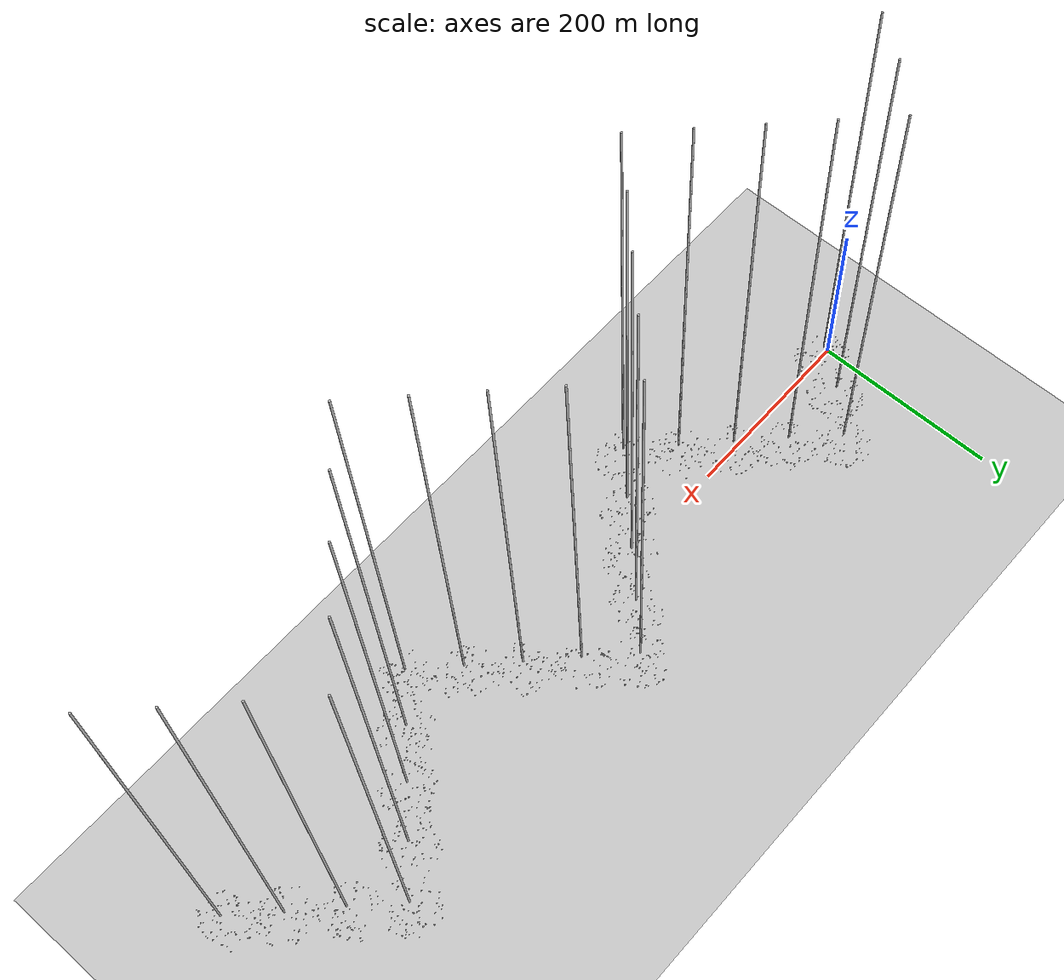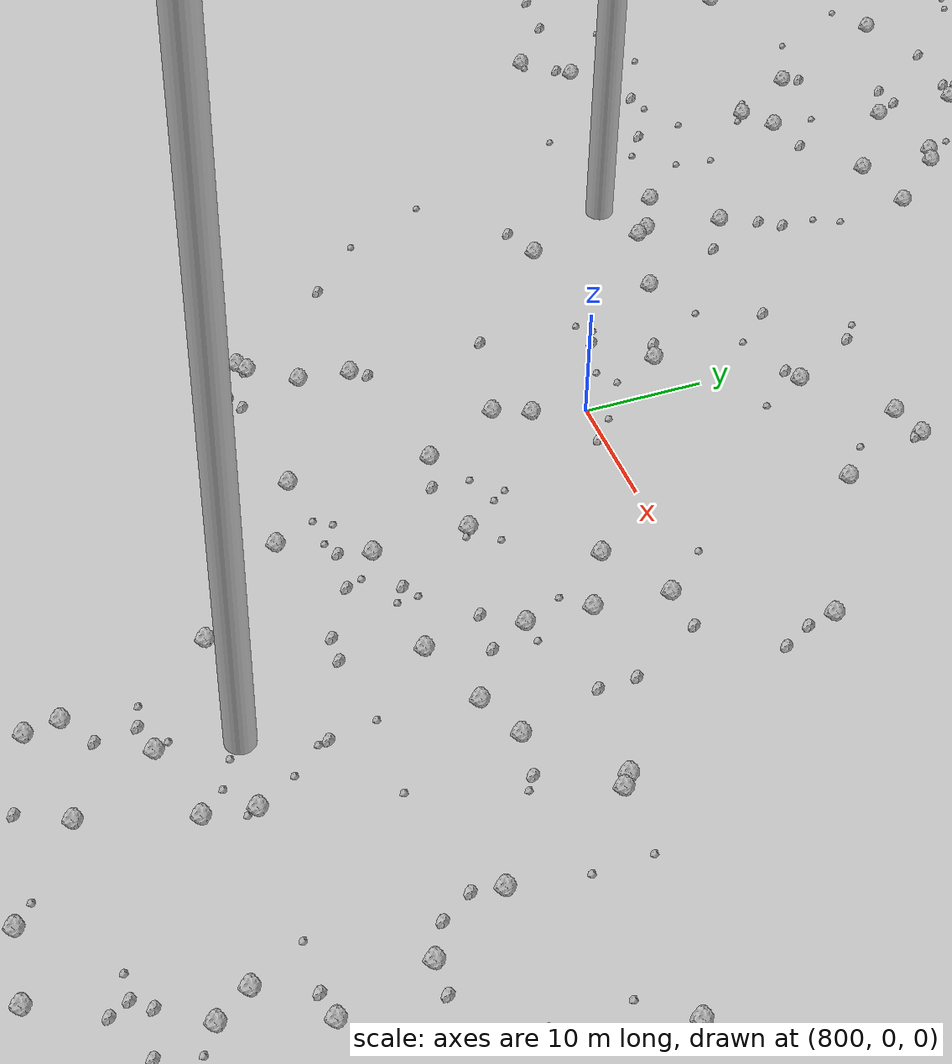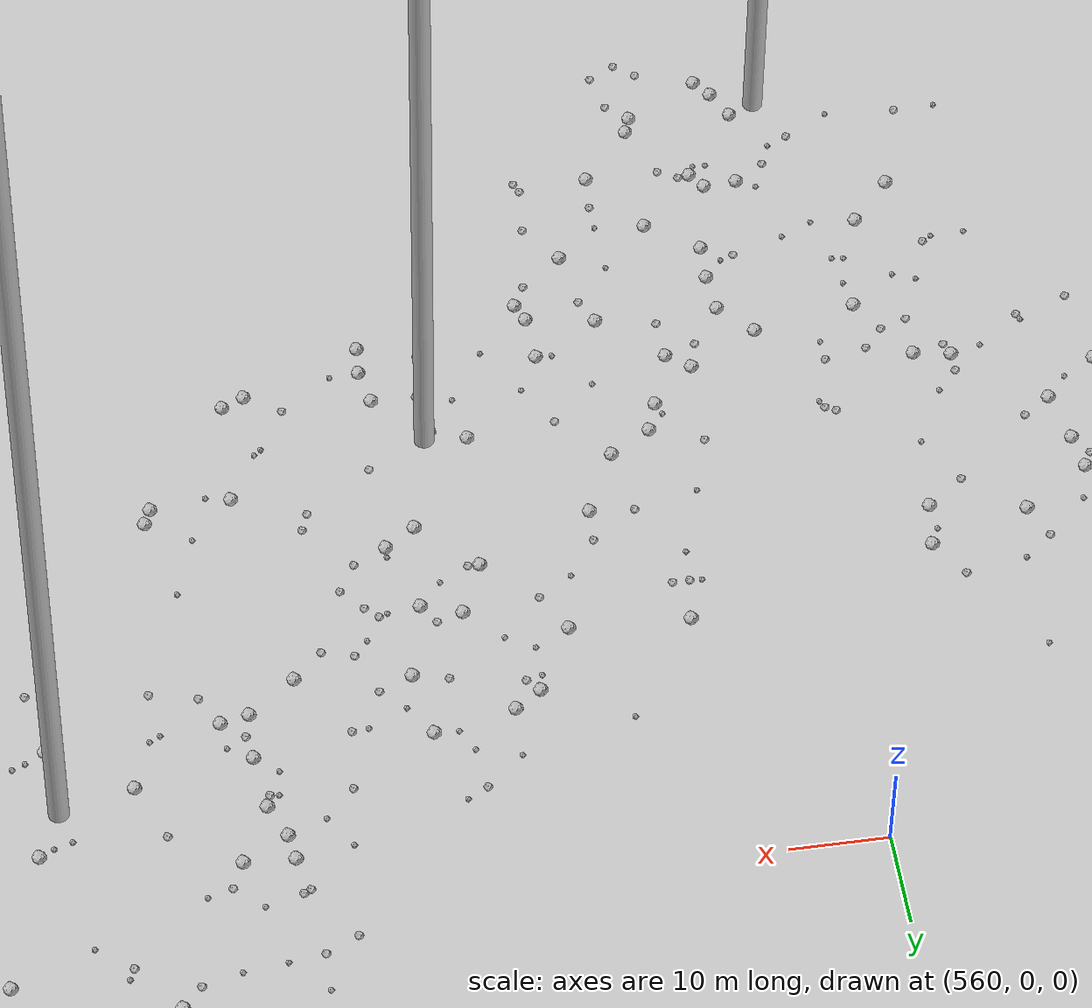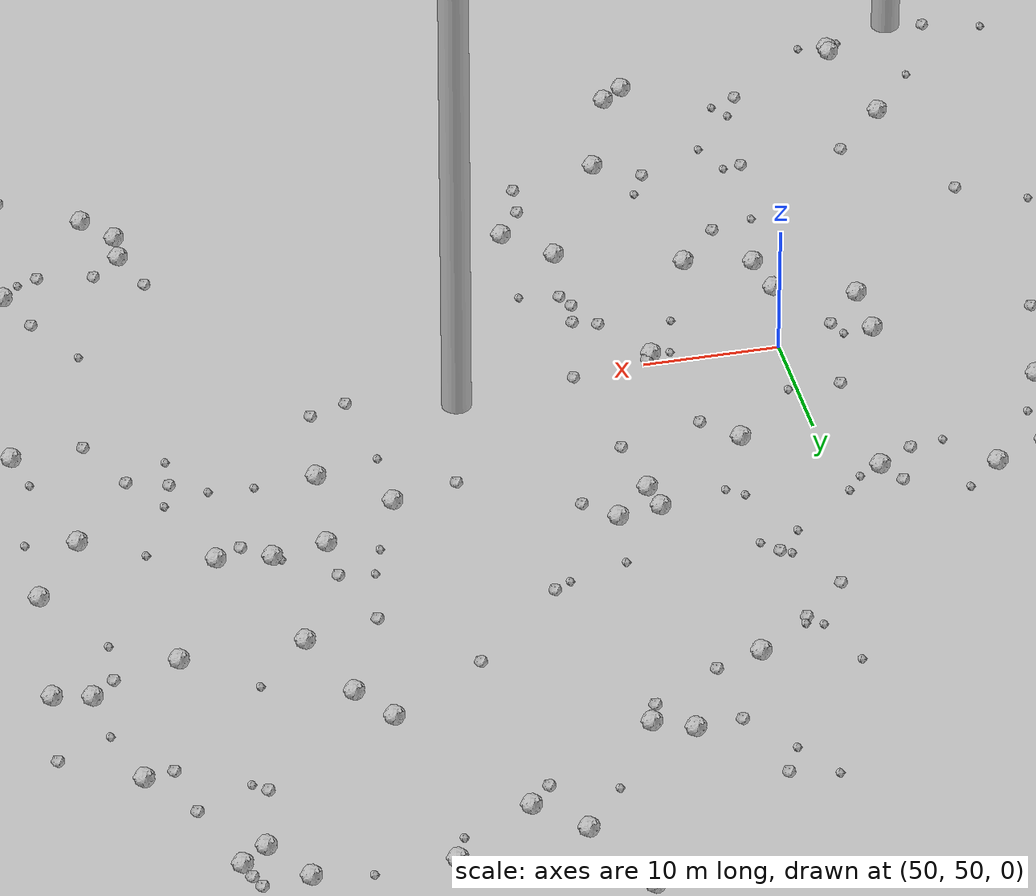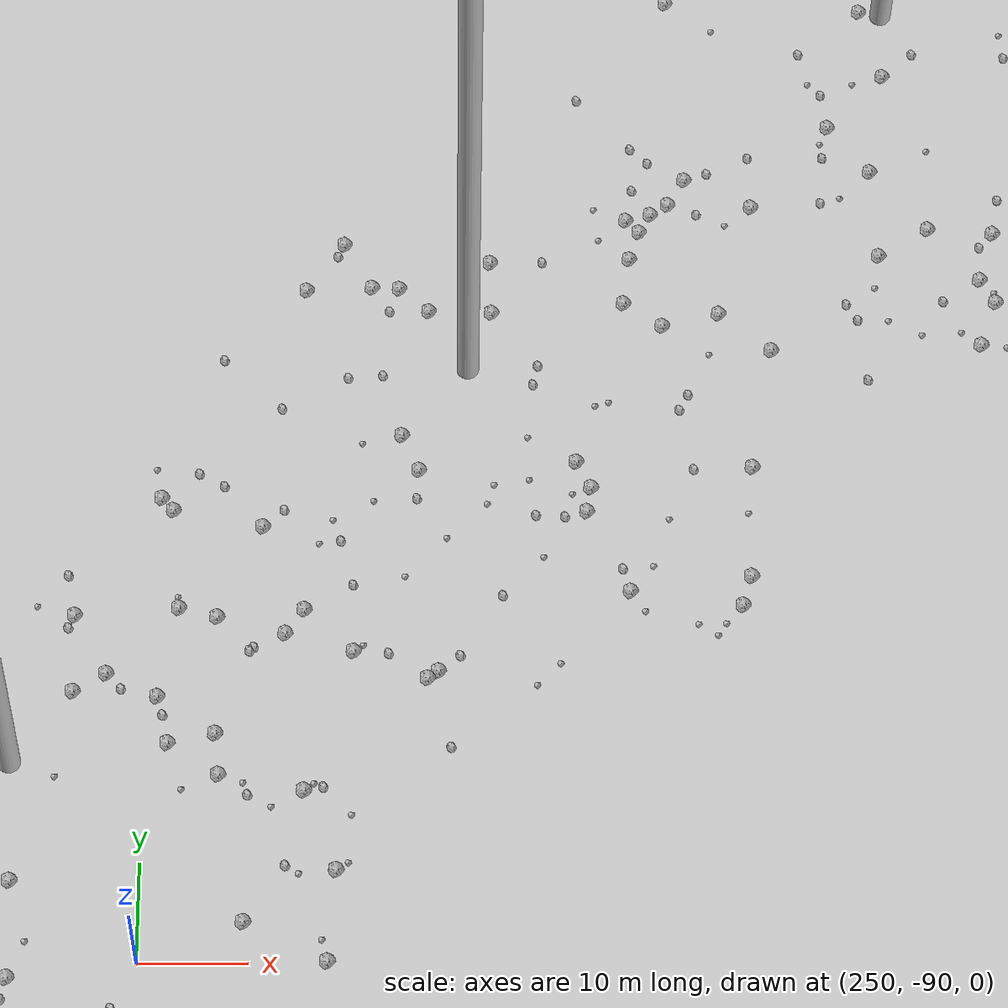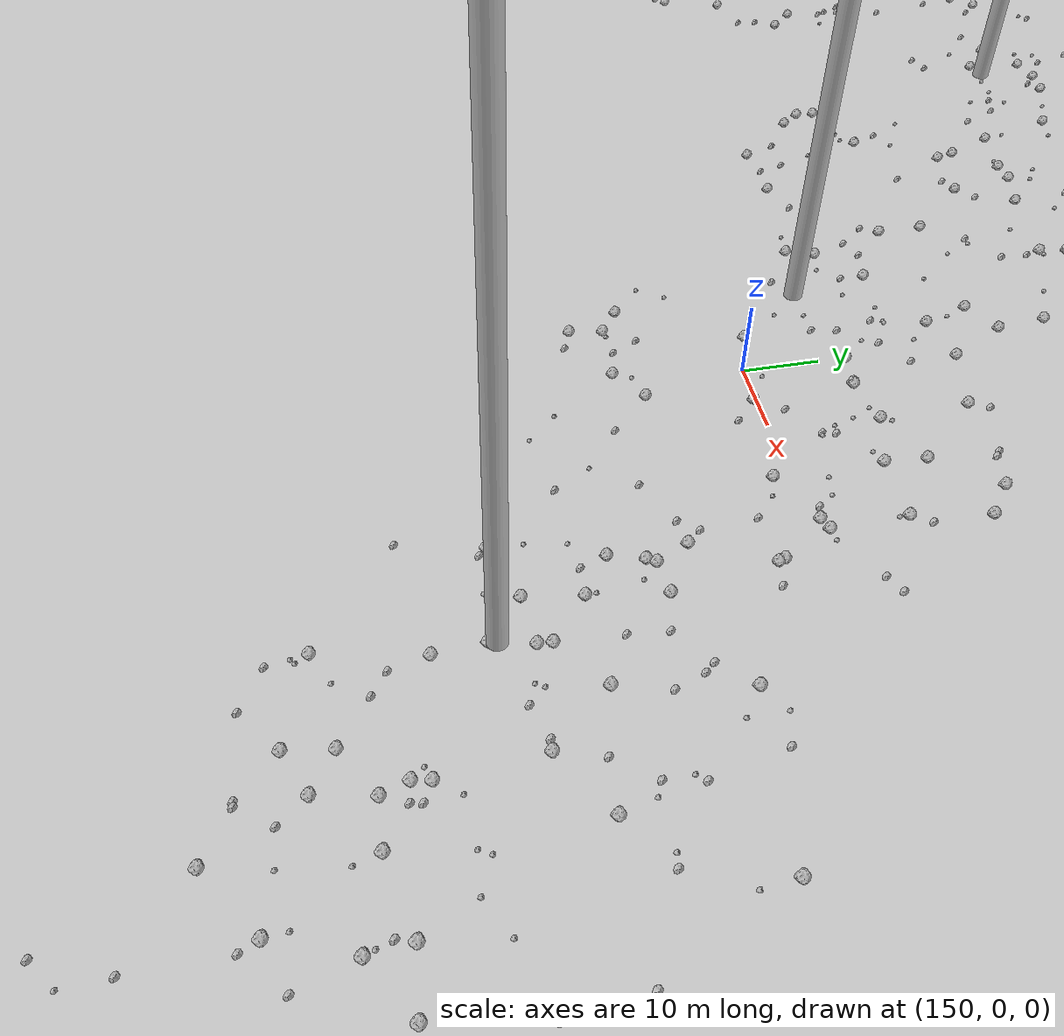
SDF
<sdf version="1.6">
 <world name="default">
  <include><uri>model://custom_ground</uri></include>
  <include><uri>model://sun</uri></include>
  <spherical_coordinates>
   <surface_model>EARTH_WGS84</surface_model>
   <latitude_deg>38.161479</latitude_deg>
   <longitude_deg>-122.454630</longitude_deg>
   <elevation>488.0</elevation>
   <heading_deg>90</heading_deg>
  </spherical_coordinates>
  <model name="rock1_0_0">
   <include><uri>model://rock1</uri><pose>36.748889242513826 12.496221878764487 0.5 0 0 0</pose></include>
  </model>
  <model name="rock1_0_1">
   <include><uri>model://rock1</uri><pose>8.304556575480731 -8.188195047349076 0.5 0 0 0</pose></include>
  </model>
  <model name="rock1_0_2">
   <include><uri>model://rock1</uri><pose>15.584066895953853 -8.7487986993089 0.5 0 0 0</pose></include>
  </model>
  <model name="rock1_0_3">
   <include><uri>model://rock1</uri><pose>5.532269456168649 -3.180855491801495 0.5 0 0 0</pose></include>
  </model>
  <model name="rock1_0_4">
   <include><uri>model://rock1</uri><pose>17.480876862670065 -16.444136282595583 0.5 0 0 0</pose></include>
  </model>
  <model name="rock1_0_5">
   <include><uri>model://rock1</uri><pose>38.369998935726755 -2.3189379626910025 0.5 0 0 0</pose></include>
  </model>
  <model name="rock1_0_6">
   <include><uri>model://rock1</uri><pose>12.839707088837109 6.328392764724342 0.5 0 0 0</pose></include>
  </model>
  <model name="rock1_0_7">
   <include><uri>model://rock1</uri><pose>33.98044942087731 -7.58404247393117 0.5 0 0 0</pose></include>
  </model>
  <model name="rock1_0_8">
   <include><uri>model://rock1</uri><pose>-6.426143357138169 -20.040606651788437 0.5 0 0 0</pose></include>
  </model>
  <model name="rock1_0_9">
   <include><uri>model://rock1</uri><pose>29.350248983008214 0.18900275283124301 0.5 0 0 0</pose></include>
  </model>
  <model name="rock1_0_10">
   <include><uri>model://rock1</uri><pose>-7.342157446605862 0.6004783828179789 0.5 0 0 0</pose></include>
  </model>
  <model name="rock1_0_11">
   <include><uri>model://rock1</uri><pose>24.36899145372358 -21.446002364901233 0.5 0 0 0</pose></include>
  </model>
  <model name="rock1_0_12">
   <include><uri>model://rock1</uri><pose>16.715484292252874 1.7516208650838507 0.5 0 0 0</pose></include>
  </model>
  <model name="rock1_0_13">
   <include><uri>model://rock1</uri><pose>15.19924243766976 -0.2518553536445509 0.5 0 0 0</pose></include>
  </model>
  <model name="rock1_0_14">
   <include><uri>model://rock1</uri><pose>10.933263179175079 -23.97170577837258 0.5 0 0 0</pose></include>
  </model>
  <model name="rock1_0_15">
   <include><uri>model://rock1</uri><pose>-11.384794949817163 -13.296588612995308 0.5 0 0 0</pose></include>
  </model>
  <model name="rock1_0_16">
   <include><uri>model://rock1</uri><pose>-13.996076443566732 5.122408244944154 0.5 0 0 0</pose></include>
  </model>
  <model name="rock1_0_17">
   <include><uri>model://rock1</uri><pose>1.264840260701586 5.9397049934866 0.5 0 0 0</pose></include>
  </model>
  <model name="rock1_0_18">
   <include><uri>model://rock1</uri><pose>2.3584784601541102 21.76944176206944 0.5 0 0 0</pose></include>
  </model>
  <model name="rock1_0_19">
   <include><uri>model://rock1</uri><pose>-0.5035977309129294 14.845360546524788 0.5 0 0 0</pose></include>
  </model>
  <model name="rock1_0_20">
   <include><uri>model://rock1</uri><pose>0.4848170203675437 26.648766132484802 0.5 0 0 0</pose></include>
  </model>
  <model name="rock1_0_21">
   <include><uri>model://rock1</uri><pose>-10.005918021464275 3.9509494095865776 0.5 0 0 0</pose></include>
  </model>
  <model name="rock1_0_22">
   <include><uri>model://rock1</uri><pose>-13.612738521137182 8.525618808304507 0.5 0 0 0</pose></include>
  </model>
  <model name="rock1_0_23">
   <include><uri>model://rock1</uri><pose>-4.317706698785672 3.6858206310314188 0.5 0 0 0</pose></include>
  </model>
  <model name="rock1_0_24">
   <include><uri>model://rock1</uri><pose>28.083412543579506 -22.82038374966076 0.5 0 0 0</pose></include>
  </model>
  <model name="rock1_0_25">
   <include><uri>model://rock1</uri><pose>-5.271276130045413 19.1678166611825 0.5 0 0 0</pose></include>
  </model>
  <model name="rock1_0_26">
   <include><uri>model://rock1</uri><pose>19.087670895961786 -25.768716896162147 0.5 0 0 0</pose></include>
  </model>
  <model name="rock2_0_0">
   <include><uri>model://rock2</uri><pose>17.011577642530717 -10.311913058934376 0.3 0 0 0</pose></include>
  </model>
  <model name="rock2_0_1">
   <include><uri>model://rock2</uri><pose>-16.45265853926905 -9.93662700943948 0.3 0 0 0</pose></include>
  </model>
  <model name="rock2_0_2">
   <include><uri>model://rock2</uri><pose>10.177817625461294 23.289633437289545 0.3 0 0 0</pose></include>
  </model>
  <model name="rock2_0_3">
   <include><uri>model://rock2</uri><pose>32.23000792605303 -2.369441813465187 0.3 0 0 0</pose></include>
  </model>
  <model name="rock2_0_4">
   <include><uri>model://rock2</uri><pose>31.749527647956825 -18.355526439987905 0.3 0 0 0</pose></include>
  </model>
  <model name="rock2_0_5">
   <include><uri>model://rock2</uri><pose>18.606417307714075 0.9759077779962517 0.3 0 0 0</pose></include>
  </model>
  <model name="rock2_0_6">
   <include><uri>model://rock2</uri><pose>3.03519606342034 20.354383352331652 0.3 0 0 0</pose></include>
  </model>
  <model name="rock2_0_7">
   <include><uri>model://rock2</uri><pose>-3.9116641756081663 12.398385040536937 0.3 0 0 0</pose></include>
  </model>
  <model name="rock2_0_8">
   <include><uri>model://rock2</uri><pose>22.013919399852384 -5.315565583734102 0.3 0 0 0</pose></include>
  </model>
  <model name="rock2_0_9">
   <include><uri>model://rock2</uri><pose>-13.996996616420333 -15.871657970608181 0.3 0 0 0</pose></include>
  </model>
  <model name="rock2_0_10">
   <include><uri>model://rock2</uri><pose>19.080621428373007 -17.65955255044924 0.3 0 0 0</pose></include>
  </model>
  <model name="rock2_0_11">
   <include><uri>model://rock2</uri><pose>31.11656836782504 -18.07961669740828 0.3 0 0 0</pose></include>
  </model>
  <model name="rock2_0_12">
   <include><uri>model://rock2</uri><pose>-12.178293738532673 -1.7681816771376866 0.3 0 0 0</pose></include>
  </model>
  <model name="rock2_0_13">
   <include><uri>model://rock2</uri><pose>28.63558359336664 10.02600559022909 0.3 0 0 0</pose></include>
  </model>
  <model name="rock2_0_14">
   <include><uri>model://rock2</uri><pose>10.918100806417378 20.227023833301573 0.3 0 0 0</pose></include>
  </model>
  <model name="rock2_0_15">
   <include><uri>model://rock2</uri><pose>36.75825682109866 -9.373893446213799 0.3 0 0 0</pose></include>
  </model>
  <model name="rock2_0_16">
   <include><uri>model://rock2</uri><pose>-8.311485556650815 20.861805642029644 0.3 0 0 0</pose></include>
  </model>
  <model name="rock2_0_17">
   <include><uri>model://rock2</uri><pose>-9.004510486543042 12.071962315633172 0.3 0 0 0</pose></include>
  </model>
  <model name="rock2_0_18">
   <include><uri>model://rock2</uri><pose>34.107720485340835 -9.1001049087279 0.3 0 0 0</pose></include>
  </model>
  <model name="rock2_0_19">
   <include><uri>model://rock2</uri><pose>2.2002663809617005 -18.62042267863199 0.3 0 0 0</pose></include>
  </model>
  <model name="rock2_0_20">
   <include><uri>model://rock2</uri><pose>-9.935007975250297 3.5352489983008653 0.3 0 0 0</pose></include>
  </model>
  <model name="rock2_0_21">
   <include><uri>model://rock2</uri><pose>-15.419711224936597 15.730983502538983 0.3 0 0 0</pose></include>
  </model>
  <model name="rock2_0_22">
   <include><uri>model://rock2</uri><pose>-19.51401912396152 -4.598353114881377 0.3 0 0 0</pose></include>
  </model>
  <model name="rock2_0_23">
   <include><uri>model://rock2</uri><pose>18.08927816964446 6.282298694196264 0.3 0 0 0</pose></include>
  </model>
  <model name="rock2_0_24">
   <include><uri>model://rock2</uri><pose>-9.63677915590936 -17.819289890260865 0.3 0 0 0</pose></include>
  </model>
  <model name="rock2_0_25">
   <include><uri>model://rock2</uri><pose>14.845341763011092 -5.927526935985398 0.3 0 0 0</pose></include>
  </model>
  <model name="rock2_0_26">
   <include><uri>model://rock2</uri><pose>12.957747453306268 20.58352328168587 0.3 0 0 0</pose></include>
  </model>
  <model name="rock3_0_0">
   <include><uri>model://rock3</uri><pose>0.8460595418767589 17.726118514708865 0.2 0 0 0</pose></include>
  </model>
  <model name="rock3_0_1">
   <include><uri>model://rock3</uri><pose>34.944442455086936 -1.4771490001085468 0.2 0 0 0</pose></include>
  </model>
  <model name="rock3_0_2">
   <include><uri>model://rock3</uri><pose>18.02998847226072 18.36030123110187 0.2 0 0 0</pose></include>
  </model>
  <model name="rock3_0_3">
   <include><uri>model://rock3</uri><pose>24.238506484213495 11.036022186867399 0.2 0 0 0</pose></include>
  </model>
  <model name="rock3_0_4">
   <include><uri>model://rock3</uri><pose>22.147681277712962 6.562195681510978 0.2 0 0 0</pose></include>
  </model>
  <model name="rock3_0_5">
   <include><uri>model://rock3</uri><pose>35.47461911975503 -12.91269905481154 0.2 0 0 0</pose></include>
  </model>
  <model name="rock3_0_6">
   <include><uri>model://rock3</uri><pose>38.27224865580588 -5.695289194411572 0.2 0 0 0</pose></include>
  </model>
  <model name="rock3_0_7">
   <include><uri>model://rock3</uri><pose>-17.151315165708358 -0.3251180601786494 0.2 0 0 0</pose></include>
  </model>
  <model name="rock3_0_8">
   <include><uri>model://rock3</uri><pose>21.64272996921332 -16.261691292687622 0.2 0 0 0</pose></include>
  </model>
  <model name="rock3_0_9">
   <include><uri>model://rock3</uri><pose>1.2678025787208256 9.720159663103466 0.2 0 0 0</pose></include>
  </model>
  <model name="rock3_0_10">
   <include><uri>model://rock3</uri><pose>-14.326018954551493 -0.7411278419766951 0.2 0 0 0</pose></include>
  </model>
  <model name="rock3_0_11">
   <include><uri>model://rock3</uri><pose>14.059697360791219 -24.38946432415808 0.2 0 0 0</pose></include>
  </model>
  <model name="rock3_0_12">
   <include><uri>model://rock3</uri><pose>5.789514063825493 2.2125675127056326 0.2 0 0 0</pose></include>
  </model>
  <model name="rock3_0_13">
   <include><uri>model://rock3</uri><pose>1.9567788609633325 13.25653219892849 0.2 0 0 0</pose></include>
  </model>
  <model name="rock3_0_14">
   <include><uri>model://rock3</uri><pose>17.387131833346835 -5.4827409143971835 0.2 0 0 0</pose></include>
  </model>
  <model name="rock3_0_15">
   <include><uri>model://rock3</uri><pose>14.542270697330835 15.686628957312664 0.2 0 0 0</pose></include>
  </model>
  <model name="rock3_0_16">
   <include><uri>model://rock3</uri><pose>37.744852326656044 -6.122994482098129 0.2 0 0 0</pose></include>
  </model>
  <model name="rock3_0_17">
   <include><uri>model://rock3</uri><pose>-6.086333913387541 14.199841314901292 0.2 0 0 0</pose></include>
  </model>
  <model name="rock3_0_18">
   <include><uri>model://rock3</uri><pose>-11.519647812544775 2.139214291291978 0.2 0 0 0</pose></include>
  </model>
  <model name="rock3_0_19">
   <include><uri>model://rock3</uri><pose>2.909107054950134 -20.09004052365959 0.2 0 0 0</pose></include>
  </model>
  <model name="rock3_0_20">
   <include><uri>model://rock3</uri><pose>22.09174214010438 -27.331232422291766 0.2 0 0 0</pose></include>
  </model>
  <model name="rock3_0_21">
   <include><uri>model://rock3</uri><pose>31.6007422886036 16.54600364025589 0.2 0 0 0</pose></include>
  </model>
  <model name="rock3_0_22">
   <include><uri>model://rock3</uri><pose>-4.105935918265914 -1.4192925391355047 0.2 0 0 0</pose></include>
  </model>
  <model name="rock3_0_23">
   <include><uri>model://rock3</uri><pose>35.69317706591063 11.084402084089852 0.2 0 0 0</pose></include>
  </model>
  <model name="rock3_0_24">
   <include><uri>model://rock3</uri><pose>15.578862028392436 -1.3999335834552689 0.2 0 0 0</pose></include>
  </model>
  <model name="rock3_0_25">
   <include><uri>model://rock3</uri><pose>-4.935934879082289 18.521507444620227 0.2 0 0 0</pose></include>
  </model>
  <model name="rock3_0_26">
   <include><uri>model://rock3</uri><pose>13.846053351747258 -28.71196283928814 0.2 0 0 0</pose></include>
  </model>
  <model name="rock1_1_0">
   <include><uri>model://rock1</uri><pose>32.94249440109123 57.68153948283197 0.5 0 0 0</pose></include>
  </model>
  <model name="rock1_1_1">
   <include><uri>model://rock1</uri><pose>53.48661164188829 14.130899375784997 0.5 0 0 0</pose></include>
  </model>
  <model name="rock1_1_2">
   <include><uri>model://rock1</uri><pose>46.710907245156534 66.21506702366878 0.5 0 0 0</pose></include>
  </model>
  <model name="rock1_1_3">
   <include><uri>model://rock1</uri><pose>38.48522967611753 67.55355627688184 0.5 0 0 0</pose></include>
  </model>
  <model name="rock1_1_4">
   <include><uri>model://rock1</uri><pose>28.723758926414874 62.78323749462439 0.5 0 0 0</pose></include>
  </model>
  <model name="rock1_1_5">
   <include><uri>model://rock1</uri><pose>36.77234765916248 11.90997297064197 0.5 0 0 0</pose></include>
  </model>
  <model name="rock1_1_6">
   <include><uri>model://rock1</uri><pose>63.39935665125665 35.23022851389365 0.5 0 0 0</pose></include>
  </model>
  <model name="rock1_1_7">
   <include><uri>model://rock1</uri><pose>42.92126742210647 44.888223199109966 0.5 0 0 0</pose></include>
  </model>
  <model name="rock1_1_8">
   <include><uri>model://rock1</uri><pose>14.117196425341586 49.642864165690284 0.5 0 0 0</pose></include>
  </model>
  <model name="rock1_1_9">
   <include><uri>model://rock1</uri><pose>55.15919568429481 15.475626663416895 0.5 0 0 0</pose></include>
  </model>
  <model name="rock1_1_10">
   <include><uri>model://rock1</uri><pose>19.712221532092453 31.13600236836456 0.5 0 0 0</pose></include>
  </model>
  <model name="rock1_1_11">
   <include><uri>model://rock1</uri><pose>34.54668479019707 65.75199195218048 0.5 0 0 0</pose></include>
  </model>
  <model name="rock1_1_12">
   <include><uri>model://rock1</uri><pose>66.65738705077685 31.868232498439482 0.5 0 0 0</pose></include>
  </model>
  <model name="rock1_1_13">
   <include><uri>model://rock1</uri><pose>42.93654030977461 49.534377553928756 0.5 0 0 0</pose></include>
  </model>
  <model name="rock1_1_14">
   <include><uri>model://rock1</uri><pose>20.274981835728294 46.506500781477996 0.5 0 0 0</pose></include>
  </model>
  <model name="rock1_1_15">
   <include><uri>model://rock1</uri><pose>48.70315004940791 42.88155127111779 0.5 0 0 0</pose></include>
  </model>
  <model name="rock1_1_16">
   <include><uri>model://rock1</uri><pose>21.439577164679495 46.38227939841995 0.5 0 0 0</pose></include>
  </model>
  <model name="rock1_1_17">
   <include><uri>model://rock1</uri><pose>18.74020134321691 59.990276879543046 0.5 0 0 0</pose></include>
  </model>
  <model name="rock1_1_18">
   <include><uri>model://rock1</uri><pose>59.36998761758848 49.29826376548439 0.5 0 0 0</pose></include>
  </model>
  <model name="rock1_1_19">
   <include><uri>model://rock1</uri><pose>49.325648407372896 39.2807848719171 0.5 0 0 0</pose></include>
  </model>
  <model name="rock1_1_20">
   <include><uri>model://rock1</uri><pose>54.295237307236135 38.14707052416838 0.5 0 0 0</pose></include>
  </model>
  <model name="rock1_1_21">
   <include><uri>model://rock1</uri><pose>16.11816970098275 23.681065423177294 0.5 0 0 0</pose></include>
  </model>
  <model name="rock1_1_22">
   <include><uri>model://rock1</uri><pose>55.50927304290642 60.762136878346624 0.5 0 0 0</pose></include>
  </model>
  <model name="rock1_1_23">
   <include><uri>model://rock1</uri><pose>35.203587326152075 21.361011886227097 0.5 0 0 0</pose></include>
  </model>
  <model name="rock1_1_24">
   <include><uri>model://rock1</uri><pose>21.44361080977159 27.34408191833903 0.5 0 0 0</pose></include>
  </model>
  <model name="rock1_1_25">
   <include><uri>model://rock1</uri><pose>57.982958502677576 24.20593939992132 0.5 0 0 0</pose></include>
  </model>
  <model name="rock1_1_26">
   <include><uri>model://rock1</uri><pose>14.053246801579746 42.026681577278104 0.5 0 0 0</pose></include>
  </model>
  <model name="rock2_1_0">
   <include><uri>model://rock2</uri><pose>64.78620083097096 28.91996264659472 0.3 0 0 0</pose></include>
  </model>
  <model name="rock2_1_1">
   <include><uri>model://rock2</uri><pose>30.863415086868752 49.05598348957096 0.3 0 0 0</pose></include>
  </model>
  <model name="rock2_1_2">
   <include><uri>model://rock2</uri><pose>47.03523508732218 26.290517788685673 0.3 0 0 0</pose></include>
  </model>
  <model name="rock2_1_3">
   <include><uri>model://rock2</uri><pose>24.890616023594628 64.31797453896937 0.3 0 0 0</pose></include>
  </model>
  <model name="rock2_1_4">
   <include><uri>model://rock2</uri><pose>51.18534188827508 34.36563958141933 0.3 0 0 0</pose></include>
  </model>
  <model name="rock2_1_5">
   <include><uri>model://rock2</uri><pose>64.15230756329765 40.51996494995656 0.3 0 0 0</pose></include>
  </model>
  <model name="rock2_1_6">
   <include><uri>model://rock2</uri><pose>57.852450385602936 58.177304119285175 0.3 0 0 0</pose></include>
  </model>
  <model name="rock2_1_7">
   <include><uri>model://rock2</uri><pose>59.734342084136614 49.72187799763619 0.3 0 0 0</pose></include>
  </model>
  <model name="rock2_1_8">
   <include><uri>model://rock2</uri><pose>45.66776480563222 48.149064864644856 0.3 0 0 0</pose></include>
  </model>
  <model name="rock2_1_9">
   <include><uri>model://rock2</uri><pose>32.15246126448462 32.751727749517634 0.3 0 0 0</pose></include>
  </model>
  <model name="rock2_1_10">
   <include><uri>model://rock2</uri><pose>15.598940872211038 26.46615159032946 0.3 0 0 0</pose></include>
  </model>
  <model name="rock2_1_11">
   <include><uri>model://rock2</uri><pose>26.83326542341641 44.00500372722219 0.3 0 0 0</pose></include>
  </model>
  <model name="rock2_1_12">
   <include><uri>model://rock2</uri><pose>29.453733501012657 67.91960449240297 0.3 0 0 0</pose></include>
  </model>
  <model name="rock2_1_13">
   <include><uri>model://rock2</uri><pose>63.942634811256966 43.92489115299942 0.3 0 0 0</pose></include>
  </model>
  <model name="rock2_1_14">
   <include><uri>model://rock2</uri><pose>54.59961312580634 26.053951818901833 0.3 0 0 0</pose></include>
  </model>
  <model name="rock2_1_15">
   <include><uri>model://rock2</uri><pose>64.45019325331714 26.02265057388561 0.3 0 0 0</pose></include>
  </model>
  <model name="rock2_1_16">
   <include><uri>model://rock2</uri><pose>18.404060190136068 47.646223644825895 0.3 0 0 0</pose></include>
  </model>
  <model name="rock2_1_17">
   <include><uri>model://rock2</uri><pose>65.40378581902166 50.82051664622357 0.3 0 0 0</pose></include>
  </model>
  <model name="rock2_1_18">
   <include><uri>model://rock2</uri><pose>45.28079199399212 17.061171438122706 0.3 0 0 0</pose></include>
  </model>
  <model name="rock2_1_19">
   <include><uri>model://rock2</uri><pose>62.172435121082344 44.555817589572804 0.3 0 0 0</pose></include>
  </model>
  <model name="rock2_1_20">
   <include><uri>model://rock2</uri><pose>43.99377077909018 64.40342847457939 0.3 0 0 0</pose></include>
  </model>
  <model name="rock2_1_21">
   <include><uri>model://rock2</uri><pose>45.50295696654642 68.09906126063854 0.3 0 0 0</pose></include>
  </model>
  <model name="rock2_1_22">
   <include><uri>model://rock2</uri><pose>18.027366735324698 32.36953401602571 0.3 0 0 0</pose></include>
  </model>
  <model name="rock2_1_23">
   <include><uri>model://rock2</uri><pose>63.554328952538015 41.833933235820865 0.3 0 0 0</pose></include>
  </model>
  <model name="rock2_1_24">
   <include><uri>model://rock2</uri><pose>24.448689692090994 62.12985078164245 0.3 0 0 0</pose></include>
  </model>
  <model name="rock2_1_25">
   <include><uri>model://rock2</uri><pose>39.17428323865464 25.790190129674578 0.3 0 0 0</pose></include>
  </model>
  <model name="rock2_1_26">
   <include><uri>model://rock2</uri><pose>46.852120893153995 55.629276665056594 0.3 0 0 0</pose></include>
  </model>
  <model name="rock3_1_0">
   <include><uri>model://rock3</uri><pose>26.558141567177383 48.706023535839385 0.2 0 0 0</pose></include>
  </model>
  <model name="rock3_1_1">
   <include><uri>model://rock3</uri><pose>47.22978628654102 17.912401725421137 0.2 0 0 0</pose></include>
  </model>
  <model name="rock3_1_2">
   <include><uri>model://rock3</uri><pose>16.56612414843832 47.49815998177813 0.2 0 0 0</pose></include>
  </model>
  <model name="rock3_1_3">
   <include><uri>model://rock3</uri><pose>48.28873956461476 66.90740626675404 0.2 0 0 0</pose></include>
  </model>
  <model name="rock3_1_4">
   <include><uri>model://rock3</uri><pose>56.854651115956315 45.133405984082785 0.2 0 0 0</pose></include>
  </model>
  <model name="rock3_1_5">
   <include><uri>model://rock3</uri><pose>41.452129172642394 63.83203863874454 0.2 0 0 0</pose></include>
  </model>
  <model name="rock3_1_6">
   <include><uri>model://rock3</uri><pose>34.60985057246694 61.75099412456023 0.2 0 0 0</pose></include>
  </model>
  <model name="rock3_1_7">
   <include><uri>model://rock3</uri><pose>49.57077831527055 23.355057683947113 0.2 0 0 0</pose></include>
  </model>
  <model name="rock3_1_8">
   <include><uri>model://rock3</uri><pose>44.98038859183653 49.41092034784488 0.2 0 0 0</pose></include>
  </model>
  <model name="rock3_1_9">
   <include><uri>model://rock3</uri><pose>21.59473818185118 61.64687893830764 0.2 0 0 0</pose></include>
  </model>
  <model name="rock3_1_10">
   <include><uri>model://rock3</uri><pose>57.841739518127355 49.05211562731078 0.2 0 0 0</pose></include>
  </model>
  <model name="rock3_1_11">
   <include><uri>model://rock3</uri><pose>55.67489974251205 28.289995874463685 0.2 0 0 0</pose></include>
  </model>
  <model name="rock3_1_12">
   <include><uri>model://rock3</uri><pose>50.63779215189247 55.451252322969474 0.2 0 0 0</pose></include>
  </model>
  <model name="rock3_1_13">
   <include><uri>model://rock3</uri><pose>25.222558229876498 33.91583969757379 0.2 0 0 0</pose></include>
  </model>
  <model name="rock3_1_14">
   <include><uri>model://rock3</uri><pose>46.31911561594384 19.302435066668107 0.2 0 0 0</pose></include>
  </model>
  <model name="rock3_1_15">
   <include><uri>model://rock3</uri><pose>23.04947909462193 64.74220151868168 0.2 0 0 0</pose></include>
  </model>
  <model name="rock3_1_16">
   <include><uri>model://rock3</uri><pose>47.95062948698762 33.39171947632181 0.2 0 0 0</pose></include>
  </model>
  <model name="rock3_1_17">
   <include><uri>model://rock3</uri><pose>29.322602560179323 64.83143618448017 0.2 0 0 0</pose></include>
  </model>
  <model name="rock3_1_18">
   <include><uri>model://rock3</uri><pose>49.44147878918096 68.41238958520185 0.2 0 0 0</pose></include>
  </model>
  <model name="rock3_1_19">
   <include><uri>model://rock3</uri><pose>27.13067470950285 35.091752139977686 0.2 0 0 0</pose></include>
  </model>
  <model name="rock3_1_20">
   <include><uri>model://rock3</uri><pose>48.21266308050694 42.31027959889134 0.2 0 0 0</pose></include>
  </model>
  <model name="rock3_1_21">
   <include><uri>model://rock3</uri><pose>38.779411440368435 11.232360618086803 0.2 0 0 0</pose></include>
  </model>
  <model name="rock3_1_22">
   <include><uri>model://rock3</uri><pose>40.99805400752075 69.78810904371495 0.2 0 0 0</pose></include>
  </model>
  <model name="rock3_1_23">
   <include><uri>model://rock3</uri><pose>13.554051262962476 33.457154051998714 0.2 0 0 0</pose></include>
  </model>
  <model name="rock3_1_24">
   <include><uri>model://rock3</uri><pose>48.35772305913187 26.351531298635646 0.2 0 0 0</pose></include>
  </model>
  <model name="rock3_1_25">
   <include><uri>model://rock3</uri><pose>66.99605959511265 39.85018092018633 0.2 0 0 0</pose></include>
  </model>
  <model name="rock3_1_26">
   <include><uri>model://rock3</uri><pose>21.25752082630289 31.214684924044256 0.2 0 0 0</pose></include>
  </model>
  <model name="rock1_2_0">
   <include><uri>model://rock1</uri><pose>69.22648388593905 91.69825880091496 0.5 0 0 0</pose></include>
  </model>
  <model name="rock1_2_1">
   <include><uri>model://rock1</uri><pose>90.60631815503328 67.70637126455942 0.5 0 0 0</pose></include>
  </model>
  <model name="rock1_2_2">
   <include><uri>model://rock1</uri><pose>103.56920150500702 90.41010728476289 0.5 0 0 0</pose></include>
  </model>
  <model name="rock1_2_3">
   <include><uri>model://rock1</uri><pose>86.64130035300443 66.91930944300236 0.5 0 0 0</pose></include>
  </model>
  <model name="rock1_2_4">
   <include><uri>model://rock1</uri><pose>98.84533804328638 100.75151392508968 0.5 0 0 0</pose></include>
  </model>
  <model name="rock1_2_5">
   <include><uri>model://rock1</uri><pose>81.14068403173891 63.02689265028049 0.5 0 0 0</pose></include>
  </model>
  <model name="rock1_2_6">
   <include><uri>model://rock1</uri><pose>85.83622613506674 58.94579752476236 0.5 0 0 0</pose></include>
  </model>
  <model name="rock1_2_7">
   <include><uri>model://rock1</uri><pose>107.16163896809866 68.94892932359454 0.5 0 0 0</pose></include>
  </model>
  <model name="rock1_2_8">
   <include><uri>model://rock1</uri><pose>79.05459907759823 98.76270855154976 0.5 0 0 0</pose></include>
  </model>
  <model name="rock1_2_9">
   <include><uri>model://rock1</uri><pose>85.00344510176092 103.27727553601537 0.5 0 0 0</pose></include>
  </model>
  <model name="rock1_2_10">
   <include><uri>model://rock1</uri><pose>72.92186254807378 108.6408272043787 0.5 0 0 0</pose></include>
  </model>
  <model name="rock1_2_11">
   <include><uri>model://rock1</uri><pose>63.360629915745136 65.29015999218394 0.5 0 0 0</pose></include>
  </model>
  <model name="rock1_2_12">
   <include><uri>model://rock1</uri><pose>99.01595744140721 78.0317183277821 0.5 0 0 0</pose></include>
  </model>
  <model name="rock1_2_13">
   <include><uri>model://rock1</uri><pose>108.10908900613165 80.23683940408051 0.5 0 0 0</pose></include>
  </model>
  <model name="rock1_2_14">
   <include><uri>model://rock1</uri><pose>75.89557990173601 101.97001832435427 0.5 0 0 0</pose></include>
  </model>
  <model name="rock1_2_15">
   <include><uri>model://rock1</uri><pose>66.1366857300483 68.28811434730858 0.5 0 0 0</pose></include>
  </model>
  <model name="rock1_2_16">
   <include><uri>model://rock1</uri><pose>90.22462089367548 77.68893236785497 0.5 0 0 0</pose></include>
  </model>
  <model name="rock1_2_17">
   <include><uri>model://rock1</uri><pose>85.98329629323669 87.32506102099927 0.5 0 0 0</pose></include>
  </model>
  <model name="rock1_2_18">
   <include><uri>model://rock1</uri><pose>105.44053352583953 80.8531790611833 0.5 0 0 0</pose></include>
  </model>
  <model name="rock1_2_19">
   <include><uri>model://rock1</uri><pose>103.52780204359868 63.11544207944493 0.5 0 0 0</pose></include>
  </model>
  <model name="rock1_2_20">
   <include><uri>model://rock1</uri><pose>96.98111646595295 99.23156596466572 0.5 0 0 0</pose></include>
  </model>
  <model name="rock1_2_21">
   <include><uri>model://rock1</uri><pose>66.48835948361246 92.95705226481778 0.5 0 0 0</pose></include>
  </model>
  <model name="rock1_2_22">
   <include><uri>model://rock1</uri><pose>88.0828901804995 84.03261550774681 0.5 0 0 0</pose></include>
  </model>
  <model name="rock1_2_23">
   <include><uri>model://rock1</uri><pose>94.68519640748852 102.95226096946314 0.5 0 0 0</pose></include>
  </model>
  <model name="rock1_2_24">
   <include><uri>model://rock1</uri><pose>62.96636440433755 67.69957615975584 0.5 0 0 0</pose></include>
  </model>
  <model name="rock1_2_25">
   <include><uri>model://rock1</uri><pose>60.16170397531951 85.61182022178838 0.5 0 0 0</pose></include>
  </model>
  <model name="rock1_2_26">
   <include><uri>model://rock1</uri><pose>94.48277242344875 67.14823497413906 0.5 0 0 0</pose></include>
  </model>
  <model name="rock2_2_0">
   <include><uri>model://rock2</uri><pose>84.77899691577983 51.50150874981857 0.3 0 0 0</pose></include>
  </model>
  <model name="rock2_2_1">
   <include><uri>model://rock2</uri><pose>72.27188824219226 75.57498844889514 0.3 0 0 0</pose></include>
  </model>
  <model name="rock2_2_2">
   <include><uri>model://rock2</uri><pose>63.12001405586134 92.52414728535756 0.3 0 0 0</pose></include>
  </model>
  <model name="rock2_2_3">
   <include><uri>model://rock2</uri><pose>100.70254072411439 94.5027424275434 0.3 0 0 0</pose></include>
  </model>
  <model name="rock2_2_4">
   <include><uri>model://rock2</uri><pose>84.86102796024353 76.15531187911992 0.3 0 0 0</pose></include>
  </model>
  <model name="rock2_2_5">
   <include><uri>model://rock2</uri><pose>81.33298027578704 108.82137327321283 0.3 0 0 0</pose></include>
  </model>
  <model name="rock2_2_6">
   <include><uri>model://rock2</uri><pose>98.42829446218809 102.02279251592628 0.3 0 0 0</pose></include>
  </model>
  <model name="rock2_2_7">
   <include><uri>model://rock2</uri><pose>56.03586505574857 74.46345074749627 0.3 0 0 0</pose></include>
  </model>
  <model name="rock2_2_8">
   <include><uri>model://rock2</uri><pose>95.70001141740755 93.262354432427 0.3 0 0 0</pose></include>
  </model>
  <model name="rock2_2_9">
   <include><uri>model://rock2</uri><pose>96.08713014529408 57.63085220538224 0.3 0 0 0</pose></include>
  </model>
  <model name="rock2_2_10">
   <include><uri>model://rock2</uri><pose>56.08773786523459 82.27997622430777 0.3 0 0 0</pose></include>
  </model>
  <model name="rock2_2_11">
   <include><uri>model://rock2</uri><pose>101.43312535164208 89.8864402837973 0.3 0 0 0</pose></include>
  </model>
  <model name="rock2_2_12">
   <include><uri>model://rock2</uri><pose>68.49366792781866 89.70504730496444 0.3 0 0 0</pose></include>
  </model>
  <model name="rock2_2_13">
   <include><uri>model://rock2</uri><pose>92.53726268599837 66.02625503126212 0.3 0 0 0</pose></include>
  </model>
  <model name="rock2_2_14">
   <include><uri>model://rock2</uri><pose>68.23393543512034 66.09528789864873 0.3 0 0 0</pose></include>
  </model>
  <model name="rock2_2_15">
   <include><uri>model://rock2</uri><pose>97.97615179475478 103.14862342055648 0.3 0 0 0</pose></include>
  </model>
  <model name="rock2_2_16">
   <include><uri>model://rock2</uri><pose>78.96958160387325 82.47928552473672 0.3 0 0 0</pose></include>
  </model>
  <model name="rock2_2_17">
   <include><uri>model://rock2</uri><pose>108.82754032583418 87.1728737446339 0.3 0 0 0</pose></include>
  </model>
  <model name="rock2_2_18">
   <include><uri>model://rock2</uri><pose>63.997957802719114 59.995253968016016 0.3 0 0 0</pose></include>
  </model>
  <model name="rock2_2_19">
   <include><uri>model://rock2</uri><pose>61.496251616210635 98.7991015212432 0.3 0 0 0</pose></include>
  </model>
  <model name="rock2_2_20">
   <include><uri>model://rock2</uri><pose>77.40796896058978 96.81344457777479 0.3 0 0 0</pose></include>
  </model>
  <model name="rock2_2_21">
   <include><uri>model://rock2</uri><pose>76.28611405485111 61.65854075491847 0.3 0 0 0</pose></include>
  </model>
  <model name="rock2_2_22">
   <include><uri>model://rock2</uri><pose>103.69228650343209 79.14940222849009 0.3 0 0 0</pose></include>
  </model>
  <model name="rock2_2_23">
   <include><uri>model://rock2</uri><pose>86.51573078330142 70.64790909609216 0.3 0 0 0</pose></include>
  </model>
  <model name="rock2_2_24">
   <include><uri>model://rock2</uri><pose>82.03771000767878 50.49514399854672 0.3 0 0 0</pose></include>
  </model>
  <model name="rock2_2_25">
   <include><uri>model://rock2</uri><pose>52.82602605845861 78.98757265876398 0.3 0 0 0</pose></include>
  </model>
  <model name="rock2_2_26">
   <include><uri>model://rock2</uri><pose>63.504196501889204 86.70658001464923 0.3 0 0 0</pose></include>
  </model>
  <model name="rock3_2_0">
   <include><uri>model://rock3</uri><pose>83.05123000573549 68.17217839661545 0.2 0 0 0</pose></include>
  </model>
  <model name="rock3_2_1">
   <include><uri>model://rock3</uri><pose>90.53862296012403 103.42442994768226 0.2 0 0 0</pose></include>
  </model>
  <model name="rock3_2_2">
   <include><uri>model://rock3</uri><pose>55.09388641683398 83.24683119989294 0.2 0 0 0</pose></include>
  </model>
  <model name="rock3_2_3">
   <include><uri>model://rock3</uri><pose>103.3433691026955 75.15905610151287 0.2 0 0 0</pose></include>
  </model>
  <model name="rock3_2_4">
   <include><uri>model://rock3</uri><pose>99.03583214506139 65.38435040012888 0.2 0 0 0</pose></include>
  </model>
  <model name="rock3_2_5">
   <include><uri>model://rock3</uri><pose>83.93101123403065 70.91099727649089 0.2 0 0 0</pose></include>
  </model>
  <model name="rock3_2_6">
   <include><uri>model://rock3</uri><pose>66.68891685545034 73.34997289543111 0.2 0 0 0</pose></include>
  </model>
  <model name="rock3_2_7">
   <include><uri>model://rock3</uri><pose>57.07284477022946 73.12072648194467 0.2 0 0 0</pose></include>
  </model>
  <model name="rock3_2_8">
   <include><uri>model://rock3</uri><pose>58.12761126681646 99.50841518758668 0.2 0 0 0</pose></include>
  </model>
  <model name="rock3_2_9">
   <include><uri>model://rock3</uri><pose>84.01205626892374 100.90651398637912 0.2 0 0 0</pose></include>
  </model>
  <model name="rock3_2_10">
   <include><uri>model://rock3</uri><pose>56.27847092601519 82.89096950679266 0.2 0 0 0</pose></include>
  </model>
  <model name="rock3_2_11">
   <include><uri>model://rock3</uri><pose>60.229620491571694 96.2139165522506 0.2 0 0 0</pose></include>
  </model>
  <model name="rock3_2_12">
   <include><uri>model://rock3</uri><pose>54.17512472062642 72.23026837949574 0.2 0 0 0</pose></include>
  </model>
  <model name="rock3_2_13">
   <include><uri>model://rock3</uri><pose>90.24713063179406 59.07213728814291 0.2 0 0 0</pose></include>
  </model>
  <model name="rock3_2_14">
   <include><uri>model://rock3</uri><pose>56.73048040882831 67.33981864468139 0.2 0 0 0</pose></include>
  </model>
  <model name="rock3_2_15">
   <include><uri>model://rock3</uri><pose>57.937703108197034 66.43787988708615 0.2 0 0 0</pose></include>
  </model>
  <model name="rock3_2_16">
   <include><uri>model://rock3</uri><pose>104.91029334191705 85.13970885542497 0.2 0 0 0</pose></include>
  </model>
  <model name="rock3_2_17">
   <include><uri>model://rock3</uri><pose>55.19686952480006 74.7465410665567 0.2 0 0 0</pose></include>
  </model>
  <model name="rock3_2_18">
   <include><uri>model://rock3</uri><pose>94.05812551879914 81.8605516305351 0.2 0 0 0</pose></include>
  </model>
  <model name="rock3_2_19">
   <include><uri>model://rock3</uri><pose>96.6042548249392 92.33529558493693 0.2 0 0 0</pose></include>
  </model>
  <model name="rock3_2_20">
   <include><uri>model://rock3</uri><pose>70.96947803754283 74.6912955860895 0.2 0 0 0</pose></include>
  </model>
  <model name="rock3_2_21">
   <include><uri>model://rock3</uri><pose>53.53105397440098 87.64239795051509 0.2 0 0 0</pose></include>
  </model>
  <model name="rock3_2_22">
   <include><uri>model://rock3</uri><pose>96.8063898536517 59.915045866630464 0.2 0 0 0</pose></include>
  </model>
  <model name="rock3_2_23">
   <include><uri>model://rock3</uri><pose>72.8094123085246 97.94245654028566 0.2 0 0 0</pose></include>
  </model>
  <model name="rock3_2_24">
   <include><uri>model://rock3</uri><pose>89.95466093527585 67.8705031047024 0.2 0 0 0</pose></include>
  </model>
  <model name="rock3_2_25">
   <include><uri>model://rock3</uri><pose>81.08910863409918 57.48631377410853 0.2 0 0 0</pose></include>
  </model>
  <model name="rock3_2_26">
   <include><uri>model://rock3</uri><pose>93.49742985027089 58.87340002619579 0.2 0 0 0</pose></include>
  </model>
  <model name="rock1_3_0">
   <include><uri>model://rock1</uri><pose>125.2763673900456 59.516229709878864 0.5 0 0 0</pose></include>
  </model>
  <model name="rock1_3_1">
   <include><uri>model://rock1</uri><pose>126.05950899910184 27.34831889743931 0.5 0 0 0</pose></include>
  </model>
  <model name="rock1_3_2">
   <include><uri>model://rock1</uri><pose>106.45647071275157 52.215841869170625 0.5 0 0 0</pose></include>
  </model>
  <model name="rock1_3_3">
   <include><uri>model://rock1</uri><pose>94.76546711842273 28.656455172036324 0.5 0 0 0</pose></include>
  </model>
  <model name="rock1_3_4">
   <include><uri>model://rock1</uri><pose>128.0199548242691 13.005934149616635 0.5 0 0 0</pose></include>
  </model>
  <model name="rock1_3_5">
   <include><uri>model://rock1</uri><pose>96.68674548096692 23.368592768383305 0.5 0 0 0</pose></include>
  </model>
  <model name="rock1_3_6">
   <include><uri>model://rock1</uri><pose>134.19297134256493 47.60708290000983 0.5 0 0 0</pose></include>
  </model>
  <model name="rock1_3_7">
   <include><uri>model://rock1</uri><pose>148.58373545574614 34.927839985691094 0.5 0 0 0</pose></include>
  </model>
  <model name="rock1_3_8">
   <include><uri>model://rock1</uri><pose>135.06784570097136 21.587350217269 0.5 0 0 0</pose></include>
  </model>
  <model name="rock1_3_9">
   <include><uri>model://rock1</uri><pose>109.32773516981369 45.60730477709476 0.5 0 0 0</pose></include>
  </model>
  <model name="rock1_3_10">
   <include><uri>model://rock1</uri><pose>110.07668241415091 42.97907727779018 0.5 0 0 0</pose></include>
  </model>
  <model name="rock1_3_11">
   <include><uri>model://rock1</uri><pose>113.15936257659754 15.264407249213152 0.5 0 0 0</pose></include>
  </model>
  <model name="rock1_3_12">
   <include><uri>model://rock1</uri><pose>118.23439123411512 42.120145088361596 0.5 0 0 0</pose></include>
  </model>
  <model name="rock1_3_13">
   <include><uri>model://rock1</uri><pose>131.39565934652566 58.27706780461995 0.5 0 0 0</pose></include>
  </model>
  <model name="rock1_3_14">
   <include><uri>model://rock1</uri><pose>122.50388263732167 49.561555535414705 0.5 0 0 0</pose></include>
  </model>
  <model name="rock1_3_15">
   <include><uri>model://rock1</uri><pose>143.76761070706982 32.3407072356614 0.5 0 0 0</pose></include>
  </model>
  <model name="rock1_3_16">
   <include><uri>model://rock1</uri><pose>103.86936745256399 32.10221097652369 0.5 0 0 0</pose></include>
  </model>
  <model name="rock1_3_17">
   <include><uri>model://rock1</uri><pose>126.02248746118275 33.486337751019164 0.5 0 0 0</pose></include>
  </model>
  <model name="rock1_3_18">
   <include><uri>model://rock1</uri><pose>134.80129474192344 51.301418576029704 0.5 0 0 0</pose></include>
  </model>
  <model name="rock1_3_19">
   <include><uri>model://rock1</uri><pose>104.10895413220058 15.02216852773225 0.5 0 0 0</pose></include>
  </model>
  <model name="rock1_3_20">
   <include><uri>model://rock1</uri><pose>116.94025020522938 51.13910498780157 0.5 0 0 0</pose></include>
  </model>
  <model name="rock1_3_21">
   <include><uri>model://rock1</uri><pose>94.61661385138358 26.05423887039031 0.5 0 0 0</pose></include>
  </model>
  <model name="rock1_3_22">
   <include><uri>model://rock1</uri><pose>118.12894832255381 65.44404179347686 0.5 0 0 0</pose></include>
  </model>
  <model name="rock1_3_23">
   <include><uri>model://rock1</uri><pose>129.26626948271084 16.7035252911462 0.5 0 0 0</pose></include>
  </model>
  <model name="rock1_3_24">
   <include><uri>model://rock1</uri><pose>113.887027696526 50.90159059949445 0.5 0 0 0</pose></include>
  </model>
  <model name="rock1_3_25">
   <include><uri>model://rock1</uri><pose>132.3144131566298 54.78019712591047 0.5 0 0 0</pose></include>
  </model>
  <model name="rock1_3_26">
   <include><uri>model://rock1</uri><pose>147.90993960251834 41.53732571939424 0.5 0 0 0</pose></include>
  </model>
  <model name="rock2_3_0">
   <include><uri>model://rock2</uri><pose>129.67267747060572 38.724165898698054 0.3 0 0 0</pose></include>
  </model>
  <model name="rock2_3_1">
   <include><uri>model://rock2</uri><pose>98.99012989238355 56.688887395435906 0.3 0 0 0</pose></include>
  </model>
  <model name="rock2_3_2">
   <include><uri>model://rock2</uri><pose>107.4298217451294 19.294334524306464 0.3 0 0 0</pose></include>
  </model>
  <model name="rock2_3_3">
   <include><uri>model://rock2</uri><pose>132.7402448114172 67.08145452588693 0.3 0 0 0</pose></include>
  </model>
  <model name="rock2_3_4">
   <include><uri>model://rock2</uri><pose>134.68109011001633 45.58659599302556 0.3 0 0 0</pose></include>
  </model>
  <model name="rock2_3_5">
   <include><uri>model://rock2</uri><pose>127.5783534994992 21.562936466995417 0.3 0 0 0</pose></include>
  </model>
  <model name="rock2_3_6">
   <include><uri>model://rock2</uri><pose>118.1175897005422 16.95419450125122 0.3 0 0 0</pose></include>
  </model>
  <model name="rock2_3_7">
   <include><uri>model://rock2</uri><pose>124.71460708053382 25.071299941317484 0.3 0 0 0</pose></include>
  </model>
  <model name="rock2_3_8">
   <include><uri>model://rock2</uri><pose>102.37393423390944 35.831643820753875 0.3 0 0 0</pose></include>
  </model>
  <model name="rock2_3_9">
   <include><uri>model://rock2</uri><pose>120.53077407164237 44.34710099839144 0.3 0 0 0</pose></include>
  </model>
  <model name="rock2_3_10">
   <include><uri>model://rock2</uri><pose>110.11740391912404 67.53643798598762 0.3 0 0 0</pose></include>
  </model>
  <model name="rock2_3_11">
   <include><uri>model://rock2</uri><pose>130.47489111932268 22.72704169987545 0.3 0 0 0</pose></include>
  </model>
  <model name="rock2_3_12">
   <include><uri>model://rock2</uri><pose>115.88780456874295 41.239437772361825 0.3 0 0 0</pose></include>
  </model>
  <model name="rock2_3_13">
   <include><uri>model://rock2</uri><pose>134.50122657453375 41.93029023483717 0.3 0 0 0</pose></include>
  </model>
  <model name="rock2_3_14">
   <include><uri>model://rock2</uri><pose>93.45098624315233 32.39232424591591 0.3 0 0 0</pose></include>
  </model>
  <model name="rock2_3_15">
   <include><uri>model://rock2</uri><pose>119.97720844766371 19.066901932637705 0.3 0 0 0</pose></include>
  </model>
  <model name="rock2_3_16">
   <include><uri>model://rock2</uri><pose>121.87210039381455 57.711124478024885 0.3 0 0 0</pose></include>
  </model>
  <model name="rock2_3_17">
   <include><uri>model://rock2</uri><pose>101.23432881230183 51.82237221908902 0.3 0 0 0</pose></include>
  </model>
  <model name="rock2_3_18">
   <include><uri>model://rock2</uri><pose>138.51647446452512 59.54067874357638 0.3 0 0 0</pose></include>
  </model>
  <model name="rock2_3_19">
   <include><uri>model://rock2</uri><pose>114.1196881519347 35.00919130701478 0.3 0 0 0</pose></include>
  </model>
  <model name="rock2_3_20">
   <include><uri>model://rock2</uri><pose>102.28553802011201 19.525114734223088 0.3 0 0 0</pose></include>
  </model>
  <model name="rock2_3_21">
   <include><uri>model://rock2</uri><pose>96.90561311946743 30.615843454619036 0.3 0 0 0</pose></include>
  </model>
  <model name="rock2_3_22">
   <include><uri>model://rock2</uri><pose>134.95548594283645 18.452311424922765 0.3 0 0 0</pose></include>
  </model>
  <model name="rock2_3_23">
   <include><uri>model://rock2</uri><pose>108.51474908691338 15.763657230822343 0.3 0 0 0</pose></include>
  </model>
  <model name="rock2_3_24">
   <include><uri>model://rock2</uri><pose>100.99534608236202 29.944221482339497 0.3 0 0 0</pose></include>
  </model>
  <model name="rock2_3_25">
   <include><uri>model://rock2</uri><pose>132.60521057198952 59.977556499358684 0.3 0 0 0</pose></include>
  </model>
  <model name="rock2_3_26">
   <include><uri>model://rock2</uri><pose>110.67892216913813 65.91569671063964 0.3 0 0 0</pose></include>
  </model>
  <model name="rock3_3_0">
   <include><uri>model://rock3</uri><pose>95.82194475938138 54.697968645375 0.2 0 0 0</pose></include>
  </model>
  <model name="rock3_3_1">
   <include><uri>model://rock3</uri><pose>132.43805158829997 15.970059369277543 0.2 0 0 0</pose></include>
  </model>
  <model name="rock3_3_2">
   <include><uri>model://rock3</uri><pose>128.61031529938705 46.01399917648675 0.2 0 0 0</pose></include>
  </model>
  <model name="rock3_3_3">
   <include><uri>model://rock3</uri><pose>144.88535907217138 29.503172151130062 0.2 0 0 0</pose></include>
  </model>
  <model name="rock3_3_4">
   <include><uri>model://rock3</uri><pose>142.3923254339351 44.35558888240136 0.2 0 0 0</pose></include>
  </model>
  <model name="rock3_3_5">
   <include><uri>model://rock3</uri><pose>107.07677389981528 62.4394158922705 0.2 0 0 0</pose></include>
  </model>
  <model name="rock3_3_6">
   <include><uri>model://rock3</uri><pose>132.2822166529155 35.02367259994247 0.2 0 0 0</pose></include>
  </model>
  <model name="rock3_3_7">
   <include><uri>model://rock3</uri><pose>136.9278548697446 29.61243853617747 0.2 0 0 0</pose></include>
  </model>
  <model name="rock3_3_8">
   <include><uri>model://rock3</uri><pose>115.22003996043108 55.8865443920618 0.2 0 0 0</pose></include>
  </model>
  <model name="rock3_3_9">
   <include><uri>model://rock3</uri><pose>125.28621172296012 17.46014078621042 0.2 0 0 0</pose></include>
  </model>
  <model name="rock3_3_10">
   <include><uri>model://rock3</uri><pose>105.51148581501693 24.19236359227158 0.2 0 0 0</pose></include>
  </model>
  <model name="rock3_3_11">
   <include><uri>model://rock3</uri><pose>112.15020331658033 51.093502258649565 0.2 0 0 0</pose></include>
  </model>
  <model name="rock3_3_12">
   <include><uri>model://rock3</uri><pose>102.47667592691155 30.40976728644539 0.2 0 0 0</pose></include>
  </model>
  <model name="rock3_3_13">
   <include><uri>model://rock3</uri><pose>105.61345334905104 55.392009766685376 0.2 0 0 0</pose></include>
  </model>
  <model name="rock3_3_14">
   <include><uri>model://rock3</uri><pose>138.16211864573017 17.563230821293185 0.2 0 0 0</pose></include>
  </model>
  <model name="rock3_3_15">
   <include><uri>model://rock3</uri><pose>133.28053141111758 61.08004745150085 0.2 0 0 0</pose></include>
  </model>
  <model name="rock3_3_16">
   <include><uri>model://rock3</uri><pose>110.18004740363912 25.1075948231466 0.2 0 0 0</pose></include>
  </model>
  <model name="rock3_3_17">
   <include><uri>model://rock3</uri><pose>121.3871336356867 64.21170431201011 0.2 0 0 0</pose></include>
  </model>
  <model name="rock3_3_18">
   <include><uri>model://rock3</uri><pose>105.17422558377132 37.458021586062955 0.2 0 0 0</pose></include>
  </model>
  <model name="rock3_3_19">
   <include><uri>model://rock3</uri><pose>124.99456712037157 54.538241765619375 0.2 0 0 0</pose></include>
  </model>
  <model name="rock3_3_20">
   <include><uri>model://rock3</uri><pose>130.6320836893448 38.71594926138289 0.2 0 0 0</pose></include>
  </model>
  <model name="rock3_3_21">
   <include><uri>model://rock3</uri><pose>117.46995332710341 54.39906085127456 0.2 0 0 0</pose></include>
  </model>
  <model name="rock3_3_22">
   <include><uri>model://rock3</uri><pose>129.96658498565574 58.28287628505338 0.2 0 0 0</pose></include>
  </model>
  <model name="rock3_3_23">
   <include><uri>model://rock3</uri><pose>139.3769736570374 56.0342147242784 0.2 0 0 0</pose></include>
  </model>
  <model name="rock3_3_24">
   <include><uri>model://rock3</uri><pose>124.50233709195655 13.587284454621182 0.2 0 0 0</pose></include>
  </model>
  <model name="rock3_3_25">
   <include><uri>model://rock3</uri><pose>134.85696823089407 48.04368146988444 0.2 0 0 0</pose></include>
  </model>
  <model name="rock3_3_26">
   <include><uri>model://rock3</uri><pose>99.64097666659991 40.46381212102855 0.2 0 0 0</pose></include>
  </model>
  <model name="rock1_4_0">
   <include><uri>model://rock1</uri><pose>148.01189799805204 -16.38913950371891 0.5 0 0 0</pose></include>
  </model>
  <model name="rock1_4_1">
   <include><uri>model://rock1</uri><pose>174.7498786225504 23.683647152396965 0.5 0 0 0</pose></include>
  </model>
  <model name="rock1_4_2">
   <include><uri>model://rock1</uri><pose>176.558944416776 -14.662073821627196 0.5 0 0 0</pose></include>
  </model>
  <model name="rock1_4_3">
   <include><uri>model://rock1</uri><pose>139.15578128217462 -20.020096203736635 0.5 0 0 0</pose></include>
  </model>
  <model name="rock1_4_4">
   <include><uri>model://rock1</uri><pose>168.61053467037428 -2.222341103047949 0.5 0 0 0</pose></include>
  </model>
  <model name="rock1_4_5">
   <include><uri>model://rock1</uri><pose>178.52827402131615 -18.74316183490282 0.5 0 0 0</pose></include>
  </model>
  <model name="rock1_4_6">
   <include><uri>model://rock1</uri><pose>155.03463860153465 12.655294101004415 0.5 0 0 0</pose></include>
  </model>
  <model name="rock1_4_7">
   <include><uri>model://rock1</uri><pose>182.90760982581673 -18.36356553927983 0.5 0 0 0</pose></include>
  </model>
  <model name="rock1_4_8">
   <include><uri>model://rock1</uri><pose>177.42680748121543 1.5114158730515292 0.5 0 0 0</pose></include>
  </model>
  <model name="rock1_4_9">
   <include><uri>model://rock1</uri><pose>180.91247368006327 -5.606362266100486 0.5 0 0 0</pose></include>
  </model>
  <model name="rock1_4_10">
   <include><uri>model://rock1</uri><pose>152.5739978903482 27.348476722489444 0.5 0 0 0</pose></include>
  </model>
  <model name="rock1_4_11">
   <include><uri>model://rock1</uri><pose>155.71980209124547 -0.48685224335727284 0.5 0 0 0</pose></include>
  </model>
  <model name="rock1_4_12">
   <include><uri>model://rock1</uri><pose>175.7854580243101 0.9259347351446792 0.5 0 0 0</pose></include>
  </model>
  <model name="rock1_4_13">
   <include><uri>model://rock1</uri><pose>180.64015663589427 -4.843977699121741 0.5 0 0 0</pose></include>
  </model>
  <model name="rock1_4_14">
   <include><uri>model://rock1</uri><pose>168.69614414617055 11.330524959026633 0.5 0 0 0</pose></include>
  </model>
  <model name="rock1_4_15">
   <include><uri>model://rock1</uri><pose>178.74412879529035 20.4811483200401 0.5 0 0 0</pose></include>
  </model>
  <model name="rock1_4_16">
   <include><uri>model://rock1</uri><pose>145.81399733835585 26.141665195360872 0.5 0 0 0</pose></include>
  </model>
  <model name="rock1_4_17">
   <include><uri>model://rock1</uri><pose>150.490838216475 13.34545719775997 0.5 0 0 0</pose></include>
  </model>
  <model name="rock1_4_18">
   <include><uri>model://rock1</uri><pose>161.6708618945341 13.637845428157561 0.5 0 0 0</pose></include>
  </model>
  <model name="rock1_4_19">
   <include><uri>model://rock1</uri><pose>155.27825185809132 12.663035348971086 0.5 0 0 0</pose></include>
  </model>
  <model name="rock1_4_20">
   <include><uri>model://rock1</uri><pose>169.08506376600215 16.542015252397732 0.5 0 0 0</pose></include>
  </model>
  <model name="rock1_4_21">
   <include><uri>model://rock1</uri><pose>136.4416690897016 -13.279968835411779 0.5 0 0 0</pose></include>
  </model>
  <model name="rock1_4_22">
   <include><uri>model://rock1</uri><pose>139.82383860378042 -15.739272106299484 0.5 0 0 0</pose></include>
  </model>
  <model name="rock1_4_23">
   <include><uri>model://rock1</uri><pose>177.157004908451 11.043710252783598 0.5 0 0 0</pose></include>
  </model>
  <model name="rock1_4_24">
   <include><uri>model://rock1</uri><pose>161.18264464575952 25.13662590991496 0.5 0 0 0</pose></include>
  </model>
  <model name="rock1_4_25">
   <include><uri>model://rock1</uri><pose>144.27902606241943 1.8943545747356723 0.5 0 0 0</pose></include>
  </model>
  <model name="rock1_4_26">
   <include><uri>model://rock1</uri><pose>152.63340481119388 -13.306842120826413 0.5 0 0 0</pose></include>
  </model>
  <model name="rock2_4_0">
   <include><uri>model://rock2</uri><pose>166.93943010587762 -17.741813063309095 0.3 0 0 0</pose></include>
  </model>
  <model name="rock2_4_1">
   <include><uri>model://rock2</uri><pose>173.95832160097592 1.5693242902660138 0.3 0 0 0</pose></include>
  </model>
  <model name="rock2_4_2">
   <include><uri>model://rock2</uri><pose>185.01118835900678 5.187372300260407 0.3 0 0 0</pose></include>
  </model>
  <model name="rock2_4_3">
   <include><uri>model://rock2</uri><pose>145.09744711959124 14.206921267323366 0.3 0 0 0</pose></include>
  </model>
  <model name="rock2_4_4">
   <include><uri>model://rock2</uri><pose>174.88998069499524 -12.79316283727574 0.3 0 0 0</pose></include>
  </model>
  <model name="rock2_4_5">
   <include><uri>model://rock2</uri><pose>187.31233362146142 6.29870332999608 0.3 0 0 0</pose></include>
  </model>
  <model name="rock2_4_6">
   <include><uri>model://rock2</uri><pose>144.0651317413645 -15.300852108260067 0.3 0 0 0</pose></include>
  </model>
  <model name="rock2_4_7">
   <include><uri>model://rock2</uri><pose>170.20410808754525 24.811384463709395 0.3 0 0 0</pose></include>
  </model>
  <model name="rock2_4_8">
   <include><uri>model://rock2</uri><pose>184.16625919655775 -6.199282614193592 0.3 0 0 0</pose></include>
  </model>
  <model name="rock2_4_9">
   <include><uri>model://rock2</uri><pose>148.40211808919378 18.646527440674838 0.3 0 0 0</pose></include>
  </model>
  <model name="rock2_4_10">
   <include><uri>model://rock2</uri><pose>174.3331359952359 -5.809047034529577 0.3 0 0 0</pose></include>
  </model>
  <model name="rock2_4_11">
   <include><uri>model://rock2</uri><pose>144.46479595194262 10.953946733771062 0.3 0 0 0</pose></include>
  </model>
  <model name="rock2_4_12">
   <include><uri>model://rock2</uri><pose>163.09654094589507 7.539045274017774 0.3 0 0 0</pose></include>
  </model>
  <model name="rock2_4_13">
   <include><uri>model://rock2</uri><pose>178.57102897215762 13.379327020620345 0.3 0 0 0</pose></include>
  </model>
  <model name="rock2_4_14">
   <include><uri>model://rock2</uri><pose>162.29485824834407 27.572481112096824 0.3 0 0 0</pose></include>
  </model>
  <model name="rock2_4_15">
   <include><uri>model://rock2</uri><pose>157.80310291277118 -18.378044983251904 0.3 0 0 0</pose></include>
  </model>
  <model name="rock2_4_16">
   <include><uri>model://rock2</uri><pose>142.30683794897553 -11.908434361864657 0.3 0 0 0</pose></include>
  </model>
  <model name="rock2_4_17">
   <include><uri>model://rock2</uri><pose>144.02155042208076 19.205938008428078 0.3 0 0 0</pose></include>
  </model>
  <model name="rock2_4_18">
   <include><uri>model://rock2</uri><pose>158.83531447272156 -3.2831701191680693 0.3 0 0 0</pose></include>
  </model>
  <model name="rock2_4_19">
   <include><uri>model://rock2</uri><pose>162.69036689402503 5.907300147849874 0.3 0 0 0</pose></include>
  </model>
  <model name="rock2_4_20">
   <include><uri>model://rock2</uri><pose>165.96907117228517 -27.485983088363717 0.3 0 0 0</pose></include>
  </model>
  <model name="rock2_4_21">
   <include><uri>model://rock2</uri><pose>157.99679154197017 2.8785458199031595 0.3 0 0 0</pose></include>
  </model>
  <model name="rock2_4_22">
   <include><uri>model://rock2</uri><pose>173.09563285884016 -14.96281413817618 0.3 0 0 0</pose></include>
  </model>
  <model name="rock2_4_23">
   <include><uri>model://rock2</uri><pose>169.5002939101933 25.39311795544984 0.3 0 0 0</pose></include>
  </model>
  <model name="rock2_4_24">
   <include><uri>model://rock2</uri><pose>142.07216900072007 -21.190705599872146 0.3 0 0 0</pose></include>
  </model>
  <model name="rock2_4_25">
   <include><uri>model://rock2</uri><pose>134.01273141450727 9.047267572392698 0.3 0 0 0</pose></include>
  </model>
  <model name="rock2_4_26">
   <include><uri>model://rock2</uri><pose>152.5224997508119 21.356454925804115 0.3 0 0 0</pose></include>
  </model>
  <model name="rock3_4_0">
   <include><uri>model://rock3</uri><pose>157.39116185633262 -28.760569339379856 0.2 0 0 0</pose></include>
  </model>
  <model name="rock3_4_1">
   <include><uri>model://rock3</uri><pose>169.66647852203957 4.232233647263293 0.2 0 0 0</pose></include>
  </model>
  <model name="rock3_4_2">
   <include><uri>model://rock3</uri><pose>148.88962131919428 -14.101753583228918 0.2 0 0 0</pose></include>
  </model>
  <model name="rock3_4_3">
   <include><uri>model://rock3</uri><pose>151.62253169784643 2.006641649988076 0.2 0 0 0</pose></include>
  </model>
  <model name="rock3_4_4">
   <include><uri>model://rock3</uri><pose>141.4437506779557 20.84982976715908 0.2 0 0 0</pose></include>
  </model>
  <model name="rock3_4_5">
   <include><uri>model://rock3</uri><pose>144.6273423621023 20.843070655727757 0.2 0 0 0</pose></include>
  </model>
  <model name="rock3_4_6">
   <include><uri>model://rock3</uri><pose>172.42656260737522 3.6236099371343187 0.2 0 0 0</pose></include>
  </model>
  <model name="rock3_4_7">
   <include><uri>model://rock3</uri><pose>180.4738154612261 -20.65660314044651 0.2 0 0 0</pose></include>
  </model>
  <model name="rock3_4_8">
   <include><uri>model://rock3</uri><pose>178.97609326530028 1.7832490667495549 0.2 0 0 0</pose></include>
  </model>
  <model name="rock3_4_9">
   <include><uri>model://rock3</uri><pose>161.66968069354004 7.883435923070948 0.2 0 0 0</pose></include>
  </model>
  <model name="rock3_4_10">
   <include><uri>model://rock3</uri><pose>162.1115954083125 15.001514464193683 0.2 0 0 0</pose></include>
  </model>
  <model name="rock3_4_11">
   <include><uri>model://rock3</uri><pose>166.71345884814383 10.763533197827819 0.2 0 0 0</pose></include>
  </model>
  <model name="rock3_4_12">
   <include><uri>model://rock3</uri><pose>162.98654248525 5.870393542718006 0.2 0 0 0</pose></include>
  </model>
  <model name="rock3_4_13">
   <include><uri>model://rock3</uri><pose>140.71431670573216 -15.433847614377033 0.2 0 0 0</pose></include>
  </model>
  <model name="rock3_4_14">
   <include><uri>model://rock3</uri><pose>140.5028134735164 7.2779968507670745 0.2 0 0 0</pose></include>
  </model>
  <model name="rock3_4_15">
   <include><uri>model://rock3</uri><pose>144.23217746703548 20.811363672039086 0.2 0 0 0</pose></include>
  </model>
  <model name="rock3_4_16">
   <include><uri>model://rock3</uri><pose>141.30252634993337 11.033873500662217 0.2 0 0 0</pose></include>
  </model>
  <model name="rock3_4_17">
   <include><uri>model://rock3</uri><pose>159.52329716904399 13.083550483915033 0.2 0 0 0</pose></include>
  </model>
  <model name="rock3_4_18">
   <include><uri>model://rock3</uri><pose>134.28719501386524 -5.993544430943466 0.2 0 0 0</pose></include>
  </model>
  <model name="rock3_4_19">
   <include><uri>model://rock3</uri><pose>176.98603630724233 9.963282281591802 0.2 0 0 0</pose></include>
  </model>
  <model name="rock3_4_20">
   <include><uri>model://rock3</uri><pose>160.8165529215518 10.518782631325536 0.2 0 0 0</pose></include>
  </model>
  <model name="rock3_4_21">
   <include><uri>model://rock3</uri><pose>148.46285284912454 23.397401896347198 0.2 0 0 0</pose></include>
  </model>
  <model name="rock3_4_22">
   <include><uri>model://rock3</uri><pose>153.87344695827315 -25.01964743682585 0.2 0 0 0</pose></include>
  </model>
  <model name="rock3_4_23">
   <include><uri>model://rock3</uri><pose>132.15608333826142 -9.303210487125952 0.2 0 0 0</pose></include>
  </model>
  <model name="rock3_4_24">
   <include><uri>model://rock3</uri><pose>171.33657545655606 -3.1385998803913076 0.2 0 0 0</pose></include>
  </model>
  <model name="rock3_4_25">
   <include><uri>model://rock3</uri><pose>147.46487678348367 16.708556829701422 0.2 0 0 0</pose></include>
  </model>
  <model name="rock3_4_26">
   <include><uri>model://rock3</uri><pose>163.17926400788383 -22.79185239008764 0.2 0 0 0</pose></include>
  </model>
  <model name="rock1_5_0">
   <include><uri>model://rock1</uri><pose>216.51313809381827 -15.294368862654778 0.5 0 0 0</pose></include>
  </model>
  <model name="rock1_5_1">
   <include><uri>model://rock1</uri><pose>181.5935029361675 -27.43260707812508 0.5 0 0 0</pose></include>
  </model>
  <model name="rock1_5_2">
   <include><uri>model://rock1</uri><pose>200.2674361262186 -48.65682483854071 0.5 0 0 0</pose></include>
  </model>
  <model name="rock1_5_3">
   <include><uri>model://rock1</uri><pose>186.85005032096012 -33.72200280696704 0.5 0 0 0</pose></include>
  </model>
  <model name="rock1_5_4">
   <include><uri>model://rock1</uri><pose>196.03483748530337 -12.645220262627376 0.5 0 0 0</pose></include>
  </model>
  <model name="rock1_5_5">
   <include><uri>model://rock1</uri><pose>213.30229085430665 -63.456529639315164 0.5 0 0 0</pose></include>
  </model>
  <model name="rock1_5_6">
   <include><uri>model://rock1</uri><pose>193.21848625053542 -27.41214615715237 0.5 0 0 0</pose></include>
  </model>
  <model name="rock1_5_7">
   <include><uri>model://rock1</uri><pose>207.4587528569708 -30.058651108395928 0.5 0 0 0</pose></include>
  </model>
  <model name="rock1_5_8">
   <include><uri>model://rock1</uri><pose>200.1037124154927 -58.280741435751324 0.5 0 0 0</pose></include>
  </model>
  <model name="rock1_5_9">
   <include><uri>model://rock1</uri><pose>200.62670987111926 -46.593583952261625 0.5 0 0 0</pose></include>
  </model>
  <model name="rock1_5_10">
   <include><uri>model://rock1</uri><pose>173.11234924499414 -36.71611281311627 0.5 0 0 0</pose></include>
  </model>
  <model name="rock1_5_11">
   <include><uri>model://rock1</uri><pose>201.36264555750873 -51.77796425650977 0.5 0 0 0</pose></include>
  </model>
  <model name="rock1_5_12">
   <include><uri>model://rock1</uri><pose>207.09165363621696 -52.09623934921452 0.5 0 0 0</pose></include>
  </model>
  <model name="rock1_5_13">
   <include><uri>model://rock1</uri><pose>176.65091146972736 -23.945301942890453 0.5 0 0 0</pose></include>
  </model>
  <model name="rock1_5_14">
   <include><uri>model://rock1</uri><pose>186.24251622352205 -44.73148359456843 0.5 0 0 0</pose></include>
  </model>
  <model name="rock1_5_15">
   <include><uri>model://rock1</uri><pose>194.75608698152942 -60.62381656465219 0.5 0 0 0</pose></include>
  </model>
  <model name="rock1_5_16">
   <include><uri>model://rock1</uri><pose>185.72676130763713 -38.68255242467687 0.5 0 0 0</pose></include>
  </model>
  <model name="rock1_5_17">
   <include><uri>model://rock1</uri><pose>177.8817192862171 -19.782056783200638 0.5 0 0 0</pose></include>
  </model>
  <model name="rock1_5_18">
   <include><uri>model://rock1</uri><pose>186.96219719775678 -32.04071866151323 0.5 0 0 0</pose></include>
  </model>
  <model name="rock1_5_19">
   <include><uri>model://rock1</uri><pose>205.580176151024 -68.7794402092546 0.5 0 0 0</pose></include>
  </model>
  <model name="rock1_5_20">
   <include><uri>model://rock1</uri><pose>183.84007714881923 -56.98932968950918 0.5 0 0 0</pose></include>
  </model>
  <model name="rock1_5_21">
   <include><uri>model://rock1</uri><pose>222.9651396200442 -50.92079710555956 0.5 0 0 0</pose></include>
  </model>
  <model name="rock1_5_22">
   <include><uri>model://rock1</uri><pose>180.55630919541255 -34.250083118574025 0.5 0 0 0</pose></include>
  </model>
  <model name="rock1_5_23">
   <include><uri>model://rock1</uri><pose>216.50071401360066 -54.91844397557323 0.5 0 0 0</pose></include>
  </model>
  <model name="rock1_5_24">
   <include><uri>model://rock1</uri><pose>195.53973219246234 -55.277934872965545 0.5 0 0 0</pose></include>
  </model>
  <model name="rock1_5_25">
   <include><uri>model://rock1</uri><pose>199.63958678893593 -34.76098123936479 0.5 0 0 0</pose></include>
  </model>
  <model name="rock1_5_26">
   <include><uri>model://rock1</uri><pose>216.04361094044128 -50.13708305280246 0.5 0 0 0</pose></include>
  </model>
  <model name="rock2_5_0">
   <include><uri>model://rock2</uri><pose>187.74064279398894 -19.636176663308902 0.3 0 0 0</pose></include>
  </model>
  <model name="rock2_5_1">
   <include><uri>model://rock2</uri><pose>184.55783289761882 -61.623697056403074 0.3 0 0 0</pose></include>
  </model>
  <model name="rock2_5_2">
   <include><uri>model://rock2</uri><pose>202.56616179479005 -49.00755619945683 0.3 0 0 0</pose></include>
  </model>
  <model name="rock2_5_3">
   <include><uri>model://rock2</uri><pose>190.05274105109254 -51.30225577271497 0.3 0 0 0</pose></include>
  </model>
  <model name="rock2_5_4">
   <include><uri>model://rock2</uri><pose>187.33068584048516 -49.329793049163314 0.3 0 0 0</pose></include>
  </model>
  <model name="rock2_5_5">
   <include><uri>model://rock2</uri><pose>201.17391735808073 -29.488779773086947 0.3 0 0 0</pose></include>
  </model>
  <model name="rock2_5_6">
   <include><uri>model://rock2</uri><pose>193.45984849740285 -17.524001097179735 0.3 0 0 0</pose></include>
  </model>
  <model name="rock2_5_7">
   <include><uri>model://rock2</uri><pose>215.39945667193206 -52.001817183293454 0.3 0 0 0</pose></include>
  </model>
  <model name="rock2_5_8">
   <include><uri>model://rock2</uri><pose>194.89366900191425 -21.15844982679311 0.3 0 0 0</pose></include>
  </model>
  <model name="rock2_5_9">
   <include><uri>model://rock2</uri><pose>193.98522784983817 -35.87929196387128 0.3 0 0 0</pose></include>
  </model>
  <model name="rock2_5_10">
   <include><uri>model://rock2</uri><pose>204.58554743006496 -25.106730589694124 0.3 0 0 0</pose></include>
  </model>
  <model name="rock2_5_11">
   <include><uri>model://rock2</uri><pose>202.78317911418645 -47.73703897380775 0.3 0 0 0</pose></include>
  </model>
  <model name="rock2_5_12">
   <include><uri>model://rock2</uri><pose>177.76004425887348 -27.09764090290423 0.3 0 0 0</pose></include>
  </model>
  <model name="rock2_5_13">
   <include><uri>model://rock2</uri><pose>199.9366133671579 -65.34380630947258 0.3 0 0 0</pose></include>
  </model>
  <model name="rock2_5_14">
   <include><uri>model://rock2</uri><pose>205.45029059550382 -20.80674008276913 0.3 0 0 0</pose></include>
  </model>
  <model name="rock2_5_15">
   <include><uri>model://rock2</uri><pose>198.17829634010766 -34.60144613524298 0.3 0 0 0</pose></include>
  </model>
  <model name="rock2_5_16">
   <include><uri>model://rock2</uri><pose>218.5616362954437 -61.369506213355265 0.3 0 0 0</pose></include>
  </model>
  <model name="rock2_5_17">
   <include><uri>model://rock2</uri><pose>170.77146179233642 -46.63559810432841 0.3 0 0 0</pose></include>
  </model>
  <model name="rock2_5_18">
   <include><uri>model://rock2</uri><pose>189.54241744926614 -64.53681000520007 0.3 0 0 0</pose></include>
  </model>
  <model name="rock2_5_19">
   <include><uri>model://rock2</uri><pose>199.35975040096832 -65.3230661349319 0.3 0 0 0</pose></include>
  </model>
  <model name="rock2_5_20">
   <include><uri>model://rock2</uri><pose>203.32345303597913 -11.7784681526988 0.3 0 0 0</pose></include>
  </model>
  <model name="rock2_5_21">
   <include><uri>model://rock2</uri><pose>187.33122966350865 -24.282349956290098 0.3 0 0 0</pose></include>
  </model>
  <model name="rock2_5_22">
   <include><uri>model://rock2</uri><pose>223.93088213935712 -30.67576932691619 0.3 0 0 0</pose></include>
  </model>
  <model name="rock2_5_23">
   <include><uri>model://rock2</uri><pose>202.6805888266998 -61.52560902307906 0.3 0 0 0</pose></include>
  </model>
  <model name="rock2_5_24">
   <include><uri>model://rock2</uri><pose>174.02074564320776 -37.63306659093952 0.3 0 0 0</pose></include>
  </model>
  <model name="rock2_5_25">
   <include><uri>model://rock2</uri><pose>192.39356227557485 -16.297213475559282 0.3 0 0 0</pose></include>
  </model>
  <model name="rock2_5_26">
   <include><uri>model://rock2</uri><pose>213.57830355028568 -25.993876109452522 0.3 0 0 0</pose></include>
  </model>
  <model name="rock3_5_0">
   <include><uri>model://rock3</uri><pose>183.26962364666136 -36.39566745952078 0.2 0 0 0</pose></include>
  </model>
  <model name="rock3_5_1">
   <include><uri>model://rock3</uri><pose>198.90046185752496 -47.134311956469546 0.2 0 0 0</pose></include>
  </model>
  <model name="rock3_5_2">
   <include><uri>model://rock3</uri><pose>216.82517798634814 -19.399645050032902 0.2 0 0 0</pose></include>
  </model>
  <model name="rock3_5_3">
   <include><uri>model://rock3</uri><pose>181.29756611618933 -26.106099498695194 0.2 0 0 0</pose></include>
  </model>
  <model name="rock3_5_4">
   <include><uri>model://rock3</uri><pose>179.21978424072162 -38.01865870543858 0.2 0 0 0</pose></include>
  </model>
  <model name="rock3_5_5">
   <include><uri>model://rock3</uri><pose>199.29086108538766 -15.077456616872198 0.2 0 0 0</pose></include>
  </model>
  <model name="rock3_5_6">
   <include><uri>model://rock3</uri><pose>191.462982014782 -34.8397018887719 0.2 0 0 0</pose></include>
  </model>
  <model name="rock3_5_7">
   <include><uri>model://rock3</uri><pose>199.29080588058395 -10.566449328281678 0.2 0 0 0</pose></include>
  </model>
  <model name="rock3_5_8">
   <include><uri>model://rock3</uri><pose>173.15802141466878 -32.52661535746218 0.2 0 0 0</pose></include>
  </model>
  <model name="rock3_5_9">
   <include><uri>model://rock3</uri><pose>202.51777315594575 -43.88196315739978 0.2 0 0 0</pose></include>
  </model>
  <model name="rock3_5_10">
   <include><uri>model://rock3</uri><pose>204.4646567786823 -21.8044360286684 0.2 0 0 0</pose></include>
  </model>
  <model name="rock3_5_11">
   <include><uri>model://rock3</uri><pose>225.06251157231515 -39.420190714857014 0.2 0 0 0</pose></include>
  </model>
  <model name="rock3_5_12">
   <include><uri>model://rock3</uri><pose>215.92533058816122 -53.76741005740375 0.2 0 0 0</pose></include>
  </model>
  <model name="rock3_5_13">
   <include><uri>model://rock3</uri><pose>217.13915381468956 -41.80683561640521 0.2 0 0 0</pose></include>
  </model>
  <model name="rock3_5_14">
   <include><uri>model://rock3</uri><pose>206.19919049961658 -25.941697357651968 0.2 0 0 0</pose></include>
  </model>
  <model name="rock3_5_15">
   <include><uri>model://rock3</uri><pose>187.69133224933987 -55.07969297525504 0.2 0 0 0</pose></include>
  </model>
  <model name="rock3_5_16">
   <include><uri>model://rock3</uri><pose>192.0425792859582 -33.88687183771348 0.2 0 0 0</pose></include>
  </model>
  <model name="rock3_5_17">
   <include><uri>model://rock3</uri><pose>183.98731834456072 -58.95147850418869 0.2 0 0 0</pose></include>
  </model>
  <model name="rock3_5_18">
   <include><uri>model://rock3</uri><pose>208.32071793301697 -43.52174971024421 0.2 0 0 0</pose></include>
  </model>
  <model name="rock3_5_19">
   <include><uri>model://rock3</uri><pose>212.88675206737872 -43.99359013766811 0.2 0 0 0</pose></include>
  </model>
  <model name="rock3_5_20">
   <include><uri>model://rock3</uri><pose>184.56619531159814 -58.5205497111655 0.2 0 0 0</pose></include>
  </model>
  <model name="rock3_5_21">
   <include><uri>model://rock3</uri><pose>173.99644060251293 -27.708592112696486 0.2 0 0 0</pose></include>
  </model>
  <model name="rock3_5_22">
   <include><uri>model://rock3</uri><pose>206.91853894095192 -61.92222823086575 0.2 0 0 0</pose></include>
  </model>
  <model name="rock3_5_23">
   <include><uri>model://rock3</uri><pose>211.94850551993892 -25.70096352412088 0.2 0 0 0</pose></include>
  </model>
  <model name="rock3_5_24">
   <include><uri>model://rock3</uri><pose>207.83268915569545 -54.94738418450565 0.2 0 0 0</pose></include>
  </model>
  <model name="rock3_5_25">
   <include><uri>model://rock3</uri><pose>209.03616984438008 -42.255347618478766 0.2 0 0 0</pose></include>
  </model>
  <model name="rock3_5_26">
   <include><uri>model://rock3</uri><pose>212.93525896208928 -60.95148166873102 0.2 0 0 0</pose></include>
  </model>
  <model name="rock1_6_0">
   <include><uri>model://rock1</uri><pose>236.53271514085154 -80.30022710969249 0.5 0 0 0</pose></include>
  </model>
  <model name="rock1_6_1">
   <include><uri>model://rock1</uri><pose>233.96474180198578 -77.59438497516057 0.5 0 0 0</pose></include>
  </model>
  <model name="rock1_6_2">
   <include><uri>model://rock1</uri><pose>267.82495676101803 -81.01272704341403 0.5 0 0 0</pose></include>
  </model>
  <model name="rock1_6_3">
   <include><uri>model://rock1</uri><pose>251.12322701244378 -63.16854538616471 0.5 0 0 0</pose></include>
  </model>
  <model name="rock1_6_4">
   <include><uri>model://rock1</uri><pose>256.57484381767813 -67.04090637436587 0.5 0 0 0</pose></include>
  </model>
  <model name="rock1_6_5">
   <include><uri>model://rock1</uri><pose>240.77252820087728 -102.9838608851688 0.5 0 0 0</pose></include>
  </model>
  <model name="rock1_6_6">
   <include><uri>model://rock1</uri><pose>227.93729765980666 -70.65989238642746 0.5 0 0 0</pose></include>
  </model>
  <model name="rock1_6_7">
   <include><uri>model://rock1</uri><pose>243.17145544285614 -54.501893885989006 0.5 0 0 0</pose></include>
  </model>
  <model name="rock1_6_8">
   <include><uri>model://rock1</uri><pose>256.94117997720787 -71.27843321017926 0.5 0 0 0</pose></include>
  </model>
  <model name="rock1_6_9">
   <include><uri>model://rock1</uri><pose>264.8218774062141 -72.95901857964736 0.5 0 0 0</pose></include>
  </model>
  <model name="rock1_6_10">
   <include><uri>model://rock1</uri><pose>237.7087980480753 -93.64581178686585 0.5 0 0 0</pose></include>
  </model>
  <model name="rock1_6_11">
   <include><uri>model://rock1</uri><pose>224.69119454346392 -104.16262298326485 0.5 0 0 0</pose></include>
  </model>
  <model name="rock1_6_12">
   <include><uri>model://rock1</uri><pose>217.82481983510343 -100.03697990156148 0.5 0 0 0</pose></include>
  </model>
  <model name="rock1_6_13">
   <include><uri>model://rock1</uri><pose>243.28896748493355 -62.568164240778465 0.5 0 0 0</pose></include>
  </model>
  <model name="rock1_6_14">
   <include><uri>model://rock1</uri><pose>259.48669861022466 -86.12712744575121 0.5 0 0 0</pose></include>
  </model>
  <model name="rock1_6_15">
   <include><uri>model://rock1</uri><pose>252.1967205852696 -68.01026857045508 0.5 0 0 0</pose></include>
  </model>
  <model name="rock1_6_16">
   <include><uri>model://rock1</uri><pose>238.45906771194245 -91.42855491928285 0.5 0 0 0</pose></include>
  </model>
  <model name="rock1_6_17">
   <include><uri>model://rock1</uri><pose>233.48407515525008 -65.82537627490149 0.5 0 0 0</pose></include>
  </model>
  <model name="rock1_6_18">
   <include><uri>model://rock1</uri><pose>267.10006414713575 -90.04370392247628 0.5 0 0 0</pose></include>
  </model>
  <model name="rock1_6_19">
   <include><uri>model://rock1</uri><pose>251.77347354250938 -104.13760300705341 0.5 0 0 0</pose></include>
  </model>
  <model name="rock1_6_20">
   <include><uri>model://rock1</uri><pose>238.31148059865828 -81.88319554364986 0.5 0 0 0</pose></include>
  </model>
  <model name="rock1_6_21">
   <include><uri>model://rock1</uri><pose>226.33604495919073 -71.72991905015749 0.5 0 0 0</pose></include>
  </model>
  <model name="rock1_6_22">
   <include><uri>model://rock1</uri><pose>252.9104681765456 -53.79131495672681 0.5 0 0 0</pose></include>
  </model>
  <model name="rock1_6_23">
   <include><uri>model://rock1</uri><pose>236.33451279459382 -94.09425747828092 0.5 0 0 0</pose></include>
  </model>
  <model name="rock1_6_24">
   <include><uri>model://rock1</uri><pose>227.22561013752795 -56.4399017387349 0.5 0 0 0</pose></include>
  </model>
  <model name="rock1_6_25">
   <include><uri>model://rock1</uri><pose>221.67815475824506 -81.84414430981928 0.5 0 0 0</pose></include>
  </model>
  <model name="rock1_6_26">
   <include><uri>model://rock1</uri><pose>246.33005817953423 -60.70853359977331 0.5 0 0 0</pose></include>
  </model>
  <model name="rock2_6_0">
   <include><uri>model://rock2</uri><pose>240.16871440683948 -98.57755151121562 0.3 0 0 0</pose></include>
  </model>
  <model name="rock2_6_1">
   <include><uri>model://rock2</uri><pose>267.5240120348017 -80.95867105851636 0.3 0 0 0</pose></include>
  </model>
  <model name="rock2_6_2">
   <include><uri>model://rock2</uri><pose>230.40161983044527 -81.34730020452015 0.3 0 0 0</pose></include>
  </model>
  <model name="rock2_6_3">
   <include><uri>model://rock2</uri><pose>242.41980166642128 -50.13983411521302 0.3 0 0 0</pose></include>
  </model>
  <model name="rock2_6_4">
   <include><uri>model://rock2</uri><pose>255.29453411269313 -102.08705042941784 0.3 0 0 0</pose></include>
  </model>
  <model name="rock2_6_5">
   <include><uri>model://rock2</uri><pose>247.82877728088732 -94.41616802050044 0.3 0 0 0</pose></include>
  </model>
  <model name="rock2_6_6">
   <include><uri>model://rock2</uri><pose>250.9090626425741 -95.14189280721389 0.3 0 0 0</pose></include>
  </model>
  <model name="rock2_6_7">
   <include><uri>model://rock2</uri><pose>249.10107008556813 -105.71028318006083 0.3 0 0 0</pose></include>
  </model>
  <model name="rock2_6_8">
   <include><uri>model://rock2</uri><pose>266.56811734443664 -72.53643143057276 0.3 0 0 0</pose></include>
  </model>
  <model name="rock2_6_9">
   <include><uri>model://rock2</uri><pose>251.64152288912666 -64.99330321698083 0.3 0 0 0</pose></include>
  </model>
  <model name="rock2_6_10">
   <include><uri>model://rock2</uri><pose>228.9638099483839 -67.55016585632912 0.3 0 0 0</pose></include>
  </model>
  <model name="rock2_6_11">
   <include><uri>model://rock2</uri><pose>234.9047070376219 -62.84337944138776 0.3 0 0 0</pose></include>
  </model>
  <model name="rock2_6_12">
   <include><uri>model://rock2</uri><pose>247.71466341956483 -62.24089348042625 0.3 0 0 0</pose></include>
  </model>
  <model name="rock2_6_13">
   <include><uri>model://rock2</uri><pose>214.25439011384964 -75.82912268277468 0.3 0 0 0</pose></include>
  </model>
  <model name="rock2_6_14">
   <include><uri>model://rock2</uri><pose>225.74295180262064 -87.2298935801013 0.3 0 0 0</pose></include>
  </model>
  <model name="rock2_6_15">
   <include><uri>model://rock2</uri><pose>227.4648308984831 -87.62964248858692 0.3 0 0 0</pose></include>
  </model>
  <model name="rock2_6_16">
   <include><uri>model://rock2</uri><pose>263.15431322185464 -80.45348425632264 0.3 0 0 0</pose></include>
  </model>
  <model name="rock2_6_17">
   <include><uri>model://rock2</uri><pose>259.5454042438863 -58.289989923139004 0.3 0 0 0</pose></include>
  </model>
  <model name="rock2_6_18">
   <include><uri>model://rock2</uri><pose>211.3726344691061 -83.26498229743244 0.3 0 0 0</pose></include>
  </model>
  <model name="rock2_6_19">
   <include><uri>model://rock2</uri><pose>259.6236123775172 -73.28716412703787 0.3 0 0 0</pose></include>
  </model>
  <model name="rock2_6_20">
   <include><uri>model://rock2</uri><pose>230.0661740777696 -77.60854010772005 0.3 0 0 0</pose></include>
  </model>
  <model name="rock2_6_21">
   <include><uri>model://rock2</uri><pose>242.5883933622911 -55.7276839265773 0.3 0 0 0</pose></include>
  </model>
  <model name="rock2_6_22">
   <include><uri>model://rock2</uri><pose>238.12561207681415 -104.21552190858982 0.3 0 0 0</pose></include>
  </model>
  <model name="rock2_6_23">
   <include><uri>model://rock2</uri><pose>235.47686390777886 -79.4159553678474 0.3 0 0 0</pose></include>
  </model>
  <model name="rock2_6_24">
   <include><uri>model://rock2</uri><pose>226.88236615734613 -65.31204876101805 0.3 0 0 0</pose></include>
  </model>
  <model name="rock2_6_25">
   <include><uri>model://rock2</uri><pose>214.18325543120375 -65.47190575295635 0.3 0 0 0</pose></include>
  </model>
  <model name="rock2_6_26">
   <include><uri>model://rock2</uri><pose>254.27098522434815 -106.2966530995597 0.3 0 0 0</pose></include>
  </model>
  <model name="rock3_6_0">
   <include><uri>model://rock3</uri><pose>262.09133489417474 -98.11029101887247 0.2 0 0 0</pose></include>
  </model>
  <model name="rock3_6_1">
   <include><uri>model://rock3</uri><pose>225.77441606457492 -77.89089429824608 0.2 0 0 0</pose></include>
  </model>
  <model name="rock3_6_2">
   <include><uri>model://rock3</uri><pose>266.5548401692327 -87.84000476654265 0.2 0 0 0</pose></include>
  </model>
  <model name="rock3_6_3">
   <include><uri>model://rock3</uri><pose>233.19266530566645 -89.86855554331181 0.2 0 0 0</pose></include>
  </model>
  <model name="rock3_6_4">
   <include><uri>model://rock3</uri><pose>264.38858793320895 -81.27885507144327 0.2 0 0 0</pose></include>
  </model>
  <model name="rock3_6_5">
   <include><uri>model://rock3</uri><pose>239.34959461068973 -104.40705162628278 0.2 0 0 0</pose></include>
  </model>
  <model name="rock3_6_6">
   <include><uri>model://rock3</uri><pose>269.15424832447985 -75.40166471248708 0.2 0 0 0</pose></include>
  </model>
  <model name="rock3_6_7">
   <include><uri>model://rock3</uri><pose>240.03939763435847 -108.80730692669296 0.2 0 0 0</pose></include>
  </model>
  <model name="rock3_6_8">
   <include><uri>model://rock3</uri><pose>248.63873281895627 -83.70294837233207 0.2 0 0 0</pose></include>
  </model>
  <model name="rock3_6_9">
   <include><uri>model://rock3</uri><pose>265.7129180567802 -72.18446266325051 0.2 0 0 0</pose></include>
  </model>
  <model name="rock3_6_10">
   <include><uri>model://rock3</uri><pose>225.04432653468805 -94.14357141765711 0.2 0 0 0</pose></include>
  </model>
  <model name="rock3_6_11">
   <include><uri>model://rock3</uri><pose>253.53703583750485 -72.69746921805319 0.2 0 0 0</pose></include>
  </model>
  <model name="rock3_6_12">
   <include><uri>model://rock3</uri><pose>239.61449119954574 -53.42169197933967 0.2 0 0 0</pose></include>
  </model>
  <model name="rock3_6_13">
   <include><uri>model://rock3</uri><pose>221.15197706260895 -70.26172594134225 0.2 0 0 0</pose></include>
  </model>
  <model name="rock3_6_14">
   <include><uri>model://rock3</uri><pose>234.33536688528383 -96.78150300344821 0.2 0 0 0</pose></include>
  </model>
  <model name="rock3_6_15">
   <include><uri>model://rock3</uri><pose>225.01374273042637 -99.18025446429911 0.2 0 0 0</pose></include>
  </model>
  <model name="rock3_6_16">
   <include><uri>model://rock3</uri><pose>221.04939186863314 -87.57907695028233 0.2 0 0 0</pose></include>
  </model>
  <model name="rock3_6_17">
   <include><uri>model://rock3</uri><pose>234.53214755668796 -80.41405456829469 0.2 0 0 0</pose></include>
  </model>
  <model name="rock3_6_18">
   <include><uri>model://rock3</uri><pose>259.1854389974076 -72.03290946044372 0.2 0 0 0</pose></include>
  </model>
  <model name="rock3_6_19">
   <include><uri>model://rock3</uri><pose>258.13700818066917 -96.65749495261957 0.2 0 0 0</pose></include>
  </model>
  <model name="rock3_6_20">
   <include><uri>model://rock3</uri><pose>261.80644113790174 -74.51330909759582 0.2 0 0 0</pose></include>
  </model>
  <model name="rock3_6_21">
   <include><uri>model://rock3</uri><pose>239.89697557753794 -87.82218993876563 0.2 0 0 0</pose></include>
  </model>
  <model name="rock3_6_22">
   <include><uri>model://rock3</uri><pose>214.45775833534196 -80.89972740519632 0.2 0 0 0</pose></include>
  </model>
  <model name="rock3_6_23">
   <include><uri>model://rock3</uri><pose>268.9020883711329 -80.23019706957297 0.2 0 0 0</pose></include>
  </model>
  <model name="rock3_6_24">
   <include><uri>model://rock3</uri><pose>234.82789784509765 -104.14612546565169 0.2 0 0 0</pose></include>
  </model>
  <model name="rock3_6_25">
   <include><uri>model://rock3</uri><pose>227.65890560114653 -93.13559007274606 0.2 0 0 0</pose></include>
  </model>
  <model name="rock3_6_26">
   <include><uri>model://rock3</uri><pose>241.9055086110419 -71.30540674494507 0.2 0 0 0</pose></include>
  </model>
  <model name="rock1_7_0">
   <include><uri>model://rock1</uri><pose>273.59689630805025 -18.057336989295656 0.5 0 0 0</pose></include>
  </model>
  <model name="rock1_7_1">
   <include><uri>model://rock1</uri><pose>299.21927428404894 -22.562638931298054 0.5 0 0 0</pose></include>
  </model>
  <model name="rock1_7_2">
   <include><uri>model://rock1</uri><pose>262.9090174499836 -56.561251103196994 0.5 0 0 0</pose></include>
  </model>
  <model name="rock1_7_3">
   <include><uri>model://rock1</uri><pose>256.51063652887 -54.76525943926203 0.5 0 0 0</pose></include>
  </model>
  <model name="rock1_7_4">
   <include><uri>model://rock1</uri><pose>270.9426375307679 -17.921001652793272 0.5 0 0 0</pose></include>
  </model>
  <model name="rock1_7_5">
   <include><uri>model://rock1</uri><pose>282.59465502639614 -20.929593028348762 0.5 0 0 0</pose></include>
  </model>
  <model name="rock1_7_6">
   <include><uri>model://rock1</uri><pose>260.6437814690998 -44.99876896461559 0.5 0 0 0</pose></include>
  </model>
  <model name="rock1_7_7">
   <include><uri>model://rock1</uri><pose>306.75139360422014 -50.70770271697108 0.5 0 0 0</pose></include>
  </model>
  <model name="rock1_7_8">
   <include><uri>model://rock1</uri><pose>276.1903805952611 -61.38598986762104 0.5 0 0 0</pose></include>
  </model>
  <model name="rock1_7_9">
   <include><uri>model://rock1</uri><pose>295.52059595783805 -19.915314563973226 0.5 0 0 0</pose></include>
  </model>
  <model name="rock1_7_10">
   <include><uri>model://rock1</uri><pose>269.29224952015164 -58.50582074426681 0.5 0 0 0</pose></include>
  </model>
  <model name="rock1_7_11">
   <include><uri>model://rock1</uri><pose>275.45557063315283 -38.826934685749066 0.5 0 0 0</pose></include>
  </model>
  <model name="rock1_7_12">
   <include><uri>model://rock1</uri><pose>291.39532649637687 -43.529757801654014 0.5 0 0 0</pose></include>
  </model>
  <model name="rock1_7_13">
   <include><uri>model://rock1</uri><pose>295.29468790373966 -52.25739777405309 0.5 0 0 0</pose></include>
  </model>
  <model name="rock1_7_14">
   <include><uri>model://rock1</uri><pose>250.99404471344235 -41.7942205138109 0.5 0 0 0</pose></include>
  </model>
  <model name="rock1_7_15">
   <include><uri>model://rock1</uri><pose>290.5020980789004 -38.02057644649335 0.5 0 0 0</pose></include>
  </model>
  <model name="rock1_7_16">
   <include><uri>model://rock1</uri><pose>273.8409148907041 -34.92589476032357 0.5 0 0 0</pose></include>
  </model>
  <model name="rock1_7_17">
   <include><uri>model://rock1</uri><pose>264.67488048964583 -54.01706820445476 0.5 0 0 0</pose></include>
  </model>
  <model name="rock1_7_18">
   <include><uri>model://rock1</uri><pose>307.32646694714725 -38.73023826643974 0.5 0 0 0</pose></include>
  </model>
  <model name="rock1_7_19">
   <include><uri>model://rock1</uri><pose>282.5426164942901 -15.079241489646542 0.5 0 0 0</pose></include>
  </model>
  <model name="rock1_7_20">
   <include><uri>model://rock1</uri><pose>264.54151502584494 -18.207223128093617 0.5 0 0 0</pose></include>
  </model>
  <model name="rock1_7_21">
   <include><uri>model://rock1</uri><pose>252.1317399443821 -43.14304030007721 0.5 0 0 0</pose></include>
  </model>
  <model name="rock1_7_22">
   <include><uri>model://rock1</uri><pose>276.47254464227353 -20.723899313232444 0.5 0 0 0</pose></include>
  </model>
  <model name="rock1_7_23">
   <include><uri>model://rock1</uri><pose>268.218802697584 -12.822393852403465 0.5 0 0 0</pose></include>
  </model>
  <model name="rock1_7_24">
   <include><uri>model://rock1</uri><pose>277.19978302256135 -60.64367764267416 0.5 0 0 0</pose></include>
  </model>
  <model name="rock1_7_25">
   <include><uri>model://rock1</uri><pose>291.8405748105046 -40.890876464030306 0.5 0 0 0</pose></include>
  </model>
  <model name="rock1_7_26">
   <include><uri>model://rock1</uri><pose>305.81654748380174 -53.83609713863734 0.5 0 0 0</pose></include>
  </model>
  <model name="rock2_7_0">
   <include><uri>model://rock2</uri><pose>301.69598858328766 -38.80843179064246 0.3 0 0 0</pose></include>
  </model>
  <model name="rock2_7_1">
   <include><uri>model://rock2</uri><pose>272.62628786690436 -20.57665401486436 0.3 0 0 0</pose></include>
  </model>
  <model name="rock2_7_2">
   <include><uri>model://rock2</uri><pose>262.2872788592111 -31.73105416230227 0.3 0 0 0</pose></include>
  </model>
  <model name="rock2_7_3">
   <include><uri>model://rock2</uri><pose>279.23650200377006 -58.92349048582801 0.3 0 0 0</pose></include>
  </model>
  <model name="rock2_7_4">
   <include><uri>model://rock2</uri><pose>289.27069845103085 -43.971063556362495 0.3 0 0 0</pose></include>
  </model>
  <model name="rock2_7_5">
   <include><uri>model://rock2</uri><pose>300.54286151846026 -32.12122512657125 0.3 0 0 0</pose></include>
  </model>
  <model name="rock2_7_6">
   <include><uri>model://rock2</uri><pose>262.6280167923125 -43.07051899314264 0.3 0 0 0</pose></include>
  </model>
  <model name="rock2_7_7">
   <include><uri>model://rock2</uri><pose>254.50314332652763 -39.02323179904272 0.3 0 0 0</pose></include>
  </model>
  <model name="rock2_7_8">
   <include><uri>model://rock2</uri><pose>275.23243071870013 -41.89082839460002 0.3 0 0 0</pose></include>
  </model>
  <model name="rock2_7_9">
   <include><uri>model://rock2</uri><pose>271.99083198752174 -28.011401025474605 0.3 0 0 0</pose></include>
  </model>
  <model name="rock2_7_10">
   <include><uri>model://rock2</uri><pose>278.3171555156158 -68.51730627525957 0.3 0 0 0</pose></include>
  </model>
  <model name="rock2_7_11">
   <include><uri>model://rock2</uri><pose>259.9643184200508 -57.89511355421473 0.3 0 0 0</pose></include>
  </model>
  <model name="rock2_7_12">
   <include><uri>model://rock2</uri><pose>273.5476337645384 -17.62064464237882 0.3 0 0 0</pose></include>
  </model>
  <model name="rock2_7_13">
   <include><uri>model://rock2</uri><pose>268.6389229167832 -28.25382868287278 0.3 0 0 0</pose></include>
  </model>
  <model name="rock2_7_14">
   <include><uri>model://rock2</uri><pose>286.4809067766797 -29.11947534500412 0.3 0 0 0</pose></include>
  </model>
  <model name="rock2_7_15">
   <include><uri>model://rock2</uri><pose>269.20038742194924 -51.28128133396646 0.3 0 0 0</pose></include>
  </model>
  <model name="rock2_7_16">
   <include><uri>model://rock2</uri><pose>256.63797166980834 -26.165374520620745 0.3 0 0 0</pose></include>
  </model>
  <model name="rock2_7_17">
   <include><uri>model://rock2</uri><pose>268.035221690093 -46.5054206463427 0.3 0 0 0</pose></include>
  </model>
  <model name="rock2_7_18">
   <include><uri>model://rock2</uri><pose>272.542889810192 -58.64553242196871 0.3 0 0 0</pose></include>
  </model>
  <model name="rock2_7_19">
   <include><uri>model://rock2</uri><pose>283.2700610193707 -52.523828596178035 0.3 0 0 0</pose></include>
  </model>
  <model name="rock2_7_20">
   <include><uri>model://rock2</uri><pose>286.53493062906034 -43.8135645578149 0.3 0 0 0</pose></include>
  </model>
  <model name="rock2_7_21">
   <include><uri>model://rock2</uri><pose>287.62667298908787 -14.904847044165628 0.3 0 0 0</pose></include>
  </model>
  <model name="rock2_7_22">
   <include><uri>model://rock2</uri><pose>294.62313571819703 -49.71384192492046 0.3 0 0 0</pose></include>
  </model>
  <model name="rock2_7_23">
   <include><uri>model://rock2</uri><pose>267.5644707675523 -14.085595809746458 0.3 0 0 0</pose></include>
  </model>
  <model name="rock2_7_24">
   <include><uri>model://rock2</uri><pose>301.45401397813714 -30.38464923956999 0.3 0 0 0</pose></include>
  </model>
  <model name="rock2_7_25">
   <include><uri>model://rock2</uri><pose>256.89995449854155 -40.40337058805138 0.3 0 0 0</pose></include>
  </model>
  <model name="rock2_7_26">
   <include><uri>model://rock2</uri><pose>286.9825683084089 -26.986671649831862 0.3 0 0 0</pose></include>
  </model>
  <model name="rock3_7_0">
   <include><uri>model://rock3</uri><pose>281.91747163968506 -42.52144124665745 0.2 0 0 0</pose></include>
  </model>
  <model name="rock3_7_1">
   <include><uri>model://rock3</uri><pose>270.03208176247585 -35.70340456622928 0.2 0 0 0</pose></include>
  </model>
  <model name="rock3_7_2">
   <include><uri>model://rock3</uri><pose>293.7464751695626 -31.22191764135821 0.2 0 0 0</pose></include>
  </model>
  <model name="rock3_7_3">
   <include><uri>model://rock3</uri><pose>252.75619514792626 -52.51239435066331 0.2 0 0 0</pose></include>
  </model>
  <model name="rock3_7_4">
   <include><uri>model://rock3</uri><pose>282.59191161504054 -40.416886892141775 0.2 0 0 0</pose></include>
  </model>
  <model name="rock3_7_5">
   <include><uri>model://rock3</uri><pose>267.25671362805946 -44.192743610409224 0.2 0 0 0</pose></include>
  </model>
  <model name="rock3_7_6">
   <include><uri>model://rock3</uri><pose>301.5603440248565 -55.74432672946427 0.2 0 0 0</pose></include>
  </model>
  <model name="rock3_7_7">
   <include><uri>model://rock3</uri><pose>290.05693641935517 -41.48522890708858 0.2 0 0 0</pose></include>
  </model>
  <model name="rock3_7_8">
   <include><uri>model://rock3</uri><pose>287.19410243974926 -48.40996383780485 0.2 0 0 0</pose></include>
  </model>
  <model name="rock3_7_9">
   <include><uri>model://rock3</uri><pose>303.3565062269186 -56.92855125691279 0.2 0 0 0</pose></include>
  </model>
  <model name="rock3_7_10">
   <include><uri>model://rock3</uri><pose>303.6593663376822 -25.795215519017063 0.2 0 0 0</pose></include>
  </model>
  <model name="rock3_7_11">
   <include><uri>model://rock3</uri><pose>292.43853436618565 -31.607990965664143 0.2 0 0 0</pose></include>
  </model>
  <model name="rock3_7_12">
   <include><uri>model://rock3</uri><pose>270.1927317230307 -57.776870412841 0.2 0 0 0</pose></include>
  </model>
  <model name="rock3_7_13">
   <include><uri>model://rock3</uri><pose>271.1164218422929 -42.13035479594059 0.2 0 0 0</pose></include>
  </model>
  <model name="rock3_7_14">
   <include><uri>model://rock3</uri><pose>274.0774134779461 -50.40417962592314 0.2 0 0 0</pose></include>
  </model>
  <model name="rock3_7_15">
   <include><uri>model://rock3</uri><pose>250.42719014434675 -38.52968613456393 0.2 0 0 0</pose></include>
  </model>
  <model name="rock3_7_16">
   <include><uri>model://rock3</uri><pose>265.96593108351885 -46.78354617207087 0.2 0 0 0</pose></include>
  </model>
  <model name="rock3_7_17">
   <include><uri>model://rock3</uri><pose>306.7202997853892 -43.72322409541855 0.2 0 0 0</pose></include>
  </model>
  <model name="rock3_7_18">
   <include><uri>model://rock3</uri><pose>288.57865109664175 -59.83799428803728 0.2 0 0 0</pose></include>
  </model>
  <model name="rock3_7_19">
   <include><uri>model://rock3</uri><pose>278.0516811958949 -46.25536756818212 0.2 0 0 0</pose></include>
  </model>
  <model name="rock3_7_20">
   <include><uri>model://rock3</uri><pose>296.62378637473313 -54.322590251103854 0.2 0 0 0</pose></include>
  </model>
  <model name="rock3_7_21">
   <include><uri>model://rock3</uri><pose>285.94622208249933 -39.884124520220794 0.2 0 0 0</pose></include>
  </model>
  <model name="rock3_7_22">
   <include><uri>model://rock3</uri><pose>297.5291283419542 -49.45662137300815 0.2 0 0 0</pose></include>
  </model>
  <model name="rock3_7_23">
   <include><uri>model://rock3</uri><pose>299.17996906882365 -44.34614928253714 0.2 0 0 0</pose></include>
  </model>
  <model name="rock3_7_24">
   <include><uri>model://rock3</uri><pose>304.1683212202615 -55.669829620892486 0.2 0 0 0</pose></include>
  </model>
  <model name="rock3_7_25">
   <include><uri>model://rock3</uri><pose>286.3552901654032 -62.10403262025329 0.2 0 0 0</pose></include>
  </model>
  <model name="rock3_7_26">
   <include><uri>model://rock3</uri><pose>285.8844239039976 -35.138608461780954 0.2 0 0 0</pose></include>
  </model>
  <model name="rock1_8_0">
   <include><uri>model://rock1</uri><pose>322.4527773800234 7.36724726482862 0.5 0 0 0</pose></include>
  </model>
  <model name="rock1_8_1">
   <include><uri>model://rock1</uri><pose>331.95749325706197 -20.03494268933327 0.5 0 0 0</pose></include>
  </model>
  <model name="rock1_8_2">
   <include><uri>model://rock1</uri><pose>300.21895061276086 -8.251815372816342 0.5 0 0 0</pose></include>
  </model>
  <model name="rock1_8_3">
   <include><uri>model://rock1</uri><pose>330.221569935303 -24.97351319172097 0.5 0 0 0</pose></include>
  </model>
  <model name="rock1_8_4">
   <include><uri>model://rock1</uri><pose>296.2441149165959 -14.73329978082478 0.5 0 0 0</pose></include>
  </model>
  <model name="rock1_8_5">
   <include><uri>model://rock1</uri><pose>333.8312646661343 25.7018128934628 0.5 0 0 0</pose></include>
  </model>
  <model name="rock1_8_6">
   <include><uri>model://rock1</uri><pose>301.95447749576977 -5.274057773312094 0.5 0 0 0</pose></include>
  </model>
  <model name="rock1_8_7">
   <include><uri>model://rock1</uri><pose>304.7797349021711 -21.195768574800788 0.5 0 0 0</pose></include>
  </model>
  <model name="rock1_8_8">
   <include><uri>model://rock1</uri><pose>320.82980595162746 -14.502306280389405 0.5 0 0 0</pose></include>
  </model>
  <model name="rock1_8_9">
   <include><uri>model://rock1</uri><pose>341.15973696794094 3.2739126625653654 0.5 0 0 0</pose></include>
  </model>
  <model name="rock1_8_10">
   <include><uri>model://rock1</uri><pose>340.3385419488173 -7.483426396913771 0.5 0 0 0</pose></include>
  </model>
  <model name="rock1_8_11">
   <include><uri>model://rock1</uri><pose>326.38425510139416 28.371753462772972 0.5 0 0 0</pose></include>
  </model>
  <model name="rock1_8_12">
   <include><uri>model://rock1</uri><pose>320.5109344472249 -4.410531019913154 0.5 0 0 0</pose></include>
  </model>
  <model name="rock1_8_13">
   <include><uri>model://rock1</uri><pose>325.84274938886176 -11.354469488893756 0.5 0 0 0</pose></include>
  </model>
  <model name="rock1_8_14">
   <include><uri>model://rock1</uri><pose>297.2861858740251 -11.522851572936464 0.5 0 0 0</pose></include>
  </model>
  <model name="rock1_8_15">
   <include><uri>model://rock1</uri><pose>316.5597482914812 1.052475564629546 0.5 0 0 0</pose></include>
  </model>
  <model name="rock1_8_16">
   <include><uri>model://rock1</uri><pose>330.59372010199627 -17.407956326200726 0.5 0 0 0</pose></include>
  </model>
  <model name="rock1_8_17">
   <include><uri>model://rock1</uri><pose>309.7278840184557 -25.470225455457737 0.5 0 0 0</pose></include>
  </model>
  <model name="rock1_8_18">
   <include><uri>model://rock1</uri><pose>298.46663837510283 -9.428847777370532 0.5 0 0 0</pose></include>
  </model>
  <model name="rock1_8_19">
   <include><uri>model://rock1</uri><pose>343.5938877248549 9.220291261774904 0.5 0 0 0</pose></include>
  </model>
  <model name="rock1_8_20">
   <include><uri>model://rock1</uri><pose>308.4509832207535 -8.610142914687064 0.5 0 0 0</pose></include>
  </model>
  <model name="rock1_8_21">
   <include><uri>model://rock1</uri><pose>336.3677843654953 -12.978126235950722 0.5 0 0 0</pose></include>
  </model>
  <model name="rock1_8_22">
   <include><uri>model://rock1</uri><pose>296.0263094596844 -10.110837544471075 0.5 0 0 0</pose></include>
  </model>
  <model name="rock1_8_23">
   <include><uri>model://rock1</uri><pose>300.7802144279401 16.74485678176905 0.5 0 0 0</pose></include>
  </model>
  <model name="rock1_8_24">
   <include><uri>model://rock1</uri><pose>320.54136938747246 15.525382486513614 0.5 0 0 0</pose></include>
  </model>
  <model name="rock1_8_25">
   <include><uri>model://rock1</uri><pose>341.542494176639 9.722032759992054 0.5 0 0 0</pose></include>
  </model>
  <model name="rock1_8_26">
   <include><uri>model://rock1</uri><pose>332.210468578524 -11.930655859232257 0.5 0 0 0</pose></include>
  </model>
  <model name="rock2_8_0">
   <include><uri>model://rock2</uri><pose>314.0806285749021 10.342721572535055 0.3 0 0 0</pose></include>
  </model>
  <model name="rock2_8_1">
   <include><uri>model://rock2</uri><pose>334.9081290028005 9.774961096334764 0.3 0 0 0</pose></include>
  </model>
  <model name="rock2_8_2">
   <include><uri>model://rock2</uri><pose>300.8567572954638 18.160039665331034 0.3 0 0 0</pose></include>
  </model>
  <model name="rock2_8_3">
   <include><uri>model://rock2</uri><pose>324.16785146858183 25.83085351308589 0.3 0 0 0</pose></include>
  </model>
  <model name="rock2_8_4">
   <include><uri>model://rock2</uri><pose>340.1202873662296 -5.0827028493865996 0.3 0 0 0</pose></include>
  </model>
  <model name="rock2_8_5">
   <include><uri>model://rock2</uri><pose>341.0413102015267 10.751028371970769 0.3 0 0 0</pose></include>
  </model>
  <model name="rock2_8_6">
   <include><uri>model://rock2</uri><pose>308.3730282319164 -2.5022043843624644 0.3 0 0 0</pose></include>
  </model>
  <model name="rock2_8_7">
   <include><uri>model://rock2</uri><pose>330.7880905811319 -13.445276977123626 0.3 0 0 0</pose></include>
  </model>
  <model name="rock2_8_8">
   <include><uri>model://rock2</uri><pose>318.95806102655257 -28.812346879910226 0.3 0 0 0</pose></include>
  </model>
  <model name="rock2_8_9">
   <include><uri>model://rock2</uri><pose>303.0015662219848 -9.299415051660628 0.3 0 0 0</pose></include>
  </model>
  <model name="rock2_8_10">
   <include><uri>model://rock2</uri><pose>298.34689754677765 -3.048584402813553 0.3 0 0 0</pose></include>
  </model>
  <model name="rock2_8_11">
   <include><uri>model://rock2</uri><pose>325.6061992581757 10.286010063036798 0.3 0 0 0</pose></include>
  </model>
  <model name="rock2_8_12">
   <include><uri>model://rock2</uri><pose>304.19750992198647 -4.387542656696446 0.3 0 0 0</pose></include>
  </model>
  <model name="rock2_8_13">
   <include><uri>model://rock2</uri><pose>317.3111062005001 -20.053487913836015 0.3 0 0 0</pose></include>
  </model>
  <model name="rock2_8_14">
   <include><uri>model://rock2</uri><pose>347.1936034438891 -12.50214904449301 0.3 0 0 0</pose></include>
  </model>
  <model name="rock2_8_15">
   <include><uri>model://rock2</uri><pose>318.34831089311047 -21.890445911057945 0.3 0 0 0</pose></include>
  </model>
  <model name="rock2_8_16">
   <include><uri>model://rock2</uri><pose>326.8259486062037 -19.761997264163476 0.3 0 0 0</pose></include>
  </model>
  <model name="rock2_8_17">
   <include><uri>model://rock2</uri><pose>342.94826719654316 -9.352841442795064 0.3 0 0 0</pose></include>
  </model>
  <model name="rock2_8_18">
   <include><uri>model://rock2</uri><pose>291.44148153502414 4.7041434094687915 0.3 0 0 0</pose></include>
  </model>
  <model name="rock2_8_19">
   <include><uri>model://rock2</uri><pose>316.0958224884614 5.231209130671587 0.3 0 0 0</pose></include>
  </model>
  <model name="rock2_8_20">
   <include><uri>model://rock2</uri><pose>315.39390512086885 -7.9688149492837965 0.3 0 0 0</pose></include>
  </model>
  <model name="rock2_8_21">
   <include><uri>model://rock2</uri><pose>322.8192245889381 22.155965315105803 0.3 0 0 0</pose></include>
  </model>
  <model name="rock2_8_22">
   <include><uri>model://rock2</uri><pose>315.85293206260076 -2.519759091344625 0.3 0 0 0</pose></include>
  </model>
  <model name="rock2_8_23">
   <include><uri>model://rock2</uri><pose>341.72007163573267 -18.586232862646877 0.3 0 0 0</pose></include>
  </model>
  <model name="rock2_8_24">
   <include><uri>model://rock2</uri><pose>296.69350366749114 -6.371920266583317 0.3 0 0 0</pose></include>
  </model>
  <model name="rock2_8_25">
   <include><uri>model://rock2</uri><pose>332.97220324699003 -7.771924481833377 0.3 0 0 0</pose></include>
  </model>
  <model name="rock2_8_26">
   <include><uri>model://rock2</uri><pose>296.66356746059375 -1.3385467022173962 0.3 0 0 0</pose></include>
  </model>
  <model name="rock3_8_0">
   <include><uri>model://rock3</uri><pose>319.3817535726066 6.570434735829821 0.2 0 0 0</pose></include>
  </model>
  <model name="rock3_8_1">
   <include><uri>model://rock3</uri><pose>331.1941196821573 21.036809886018673 0.2 0 0 0</pose></include>
  </model>
  <model name="rock3_8_2">
   <include><uri>model://rock3</uri><pose>334.66218440130746 12.633734835263247 0.2 0 0 0</pose></include>
  </model>
  <model name="rock3_8_3">
   <include><uri>model://rock3</uri><pose>317.79002627396306 26.533446019535567 0.2 0 0 0</pose></include>
  </model>
  <model name="rock3_8_4">
   <include><uri>model://rock3</uri><pose>305.34400744430343 13.322108732771781 0.2 0 0 0</pose></include>
  </model>
  <model name="rock3_8_5">
   <include><uri>model://rock3</uri><pose>317.3690266946934 -7.433960132609318 0.2 0 0 0</pose></include>
  </model>
  <model name="rock3_8_6">
   <include><uri>model://rock3</uri><pose>332.7021982481469 -25.162977376474593 0.2 0 0 0</pose></include>
  </model>
  <model name="rock3_8_7">
   <include><uri>model://rock3</uri><pose>328.37720595978215 -23.407044470674137 0.2 0 0 0</pose></include>
  </model>
  <model name="rock3_8_8">
   <include><uri>model://rock3</uri><pose>339.17670100051964 15.162302543415763 0.2 0 0 0</pose></include>
  </model>
  <model name="rock3_8_9">
   <include><uri>model://rock3</uri><pose>300.8602240592397 20.012085003194088 0.2 0 0 0</pose></include>
  </model>
  <model name="rock3_8_10">
   <include><uri>model://rock3</uri><pose>331.8718925942145 -18.800953234128045 0.2 0 0 0</pose></include>
  </model>
  <model name="rock3_8_11">
   <include><uri>model://rock3</uri><pose>293.2389813900154 -12.327399020067702 0.2 0 0 0</pose></include>
  </model>
  <model name="rock3_8_12">
   <include><uri>model://rock3</uri><pose>342.8808807811538 3.7864497945604256 0.2 0 0 0</pose></include>
  </model>
  <model name="rock3_8_13">
   <include><uri>model://rock3</uri><pose>341.7424068338495 -10.039641811421362 0.2 0 0 0</pose></include>
  </model>
  <model name="rock3_8_14">
   <include><uri>model://rock3</uri><pose>324.52326072622014 -23.662248876883602 0.2 0 0 0</pose></include>
  </model>
  <model name="rock3_8_15">
   <include><uri>model://rock3</uri><pose>344.9385388306247 8.26897862292703 0.2 0 0 0</pose></include>
  </model>
  <model name="rock3_8_16">
   <include><uri>model://rock3</uri><pose>314.8459832092622 6.585746791585585 0.2 0 0 0</pose></include>
  </model>
  <model name="rock3_8_17">
   <include><uri>model://rock3</uri><pose>331.79321883631326 24.966122253348537 0.2 0 0 0</pose></include>
  </model>
  <model name="rock3_8_18">
   <include><uri>model://rock3</uri><pose>320.22330795265805 -18.156631801429803 0.2 0 0 0</pose></include>
  </model>
  <model name="rock3_8_19">
   <include><uri>model://rock3</uri><pose>315.7154427590596 -0.8344447479316699 0.2 0 0 0</pose></include>
  </model>
  <model name="rock3_8_20">
   <include><uri>model://rock3</uri><pose>339.7918483313044 -7.098612882546885 0.2 0 0 0</pose></include>
  </model>
  <model name="rock3_8_21">
   <include><uri>model://rock3</uri><pose>326.32489870368124 -1.7553584743282329 0.2 0 0 0</pose></include>
  </model>
  <model name="rock3_8_22">
   <include><uri>model://rock3</uri><pose>349.2290853582632 -5.033540003858494 0.2 0 0 0</pose></include>
  </model>
  <model name="rock3_8_23">
   <include><uri>model://rock3</uri><pose>343.9966526488443 -9.95015861890366 0.2 0 0 0</pose></include>
  </model>
  <model name="rock3_8_24">
   <include><uri>model://rock3</uri><pose>292.8304977212566 -8.654649044447645 0.2 0 0 0</pose></include>
  </model>
  <model name="rock3_8_25">
   <include><uri>model://rock3</uri><pose>321.35079615982744 -22.017740618032608 0.2 0 0 0</pose></include>
  </model>
  <model name="rock3_8_26">
   <include><uri>model://rock3</uri><pose>305.7779821434191 -10.628475694532305 0.2 0 0 0</pose></include>
  </model>
  <model name="rock1_9_0">
   <include><uri>model://rock1</uri><pose>368.2962947931371 41.05516981899993 0.5 0 0 0</pose></include>
  </model>
  <model name="rock1_9_1">
   <include><uri>model://rock1</uri><pose>363.16423896512526 13.793630246906945 0.5 0 0 0</pose></include>
  </model>
  <model name="rock1_9_2">
   <include><uri>model://rock1</uri><pose>352.84645749806276 52.46313866372935 0.5 0 0 0</pose></include>
  </model>
  <model name="rock1_9_3">
   <include><uri>model://rock1</uri><pose>356.7265225878533 27.02906418493491 0.5 0 0 0</pose></include>
  </model>
  <model name="rock1_9_4">
   <include><uri>model://rock1</uri><pose>343.1399345696864 23.3707187907156 0.5 0 0 0</pose></include>
  </model>
  <model name="rock1_9_5">
   <include><uri>model://rock1</uri><pose>345.8226686483239 20.760281540179257 0.5 0 0 0</pose></include>
  </model>
  <model name="rock1_9_6">
   <include><uri>model://rock1</uri><pose>359.62957352598687 68.57639773296117 0.5 0 0 0</pose></include>
  </model>
  <model name="rock1_9_7">
   <include><uri>model://rock1</uri><pose>363.7131047550651 27.509446349200132 0.5 0 0 0</pose></include>
  </model>
  <model name="rock1_9_8">
   <include><uri>model://rock1</uri><pose>366.11987355262283 51.401712351496656 0.5 0 0 0</pose></include>
  </model>
  <model name="rock1_9_9">
   <include><uri>model://rock1</uri><pose>371.92385356473983 16.176921552008544 0.5 0 0 0</pose></include>
  </model>
  <model name="rock1_9_10">
   <include><uri>model://rock1</uri><pose>377.2838213813796 52.62123809271247 0.5 0 0 0</pose></include>
  </model>
  <model name="rock1_9_11">
   <include><uri>model://rock1</uri><pose>374.96480023190935 56.33035080660408 0.5 0 0 0</pose></include>
  </model>
  <model name="rock1_9_12">
   <include><uri>model://rock1</uri><pose>363.09115392064905 42.86111795201363 0.5 0 0 0</pose></include>
  </model>
  <model name="rock1_9_13">
   <include><uri>model://rock1</uri><pose>373.5699193784318 30.31904843079812 0.5 0 0 0</pose></include>
  </model>
  <model name="rock1_9_14">
   <include><uri>model://rock1</uri><pose>376.1685407283207 59.89754481761696 0.5 0 0 0</pose></include>
  </model>
  <model name="rock1_9_15">
   <include><uri>model://rock1</uri><pose>345.0771702259564 61.250624140216104 0.5 0 0 0</pose></include>
  </model>
  <model name="rock1_9_16">
   <include><uri>model://rock1</uri><pose>367.81424210760844 50.01380658568221 0.5 0 0 0</pose></include>
  </model>
  <model name="rock1_9_17">
   <include><uri>model://rock1</uri><pose>339.3929401042491 32.268525700027226 0.5 0 0 0</pose></include>
  </model>
  <model name="rock1_9_18">
   <include><uri>model://rock1</uri><pose>369.53127740982876 43.82933404459298 0.5 0 0 0</pose></include>
  </model>
  <model name="rock1_9_19">
   <include><uri>model://rock1</uri><pose>358.92780540358945 62.56032626121986 0.5 0 0 0</pose></include>
  </model>
  <model name="rock1_9_20">
   <include><uri>model://rock1</uri><pose>353.1706280705278 10.89779918160654 0.5 0 0 0</pose></include>
  </model>
  <model name="rock1_9_21">
   <include><uri>model://rock1</uri><pose>375.72982222888555 54.90246410197559 0.5 0 0 0</pose></include>
  </model>
  <model name="rock1_9_22">
   <include><uri>model://rock1</uri><pose>339.05348210190925 32.05511833220034 0.5 0 0 0</pose></include>
  </model>
  <model name="rock1_9_23">
   <include><uri>model://rock1</uri><pose>381.5791922519578 36.40586743044146 0.5 0 0 0</pose></include>
  </model>
  <model name="rock1_9_24">
   <include><uri>model://rock1</uri><pose>348.14111648285206 38.112365062719874 0.5 0 0 0</pose></include>
  </model>
  <model name="rock1_9_25">
   <include><uri>model://rock1</uri><pose>371.6082416232253 61.437063338994584 0.5 0 0 0</pose></include>
  </model>
  <model name="rock1_9_26">
   <include><uri>model://rock1</uri><pose>335.3988102988301 26.149621249877693 0.5 0 0 0</pose></include>
  </model>
  <model name="rock2_9_0">
   <include><uri>model://rock2</uri><pose>363.2233614087474 64.62137269398335 0.3 0 0 0</pose></include>
  </model>
  <model name="rock2_9_1">
   <include><uri>model://rock2</uri><pose>357.7462919327947 17.052060197725986 0.3 0 0 0</pose></include>
  </model>
  <model name="rock2_9_2">
   <include><uri>model://rock2</uri><pose>368.5276338334395 20.197494397082583 0.3 0 0 0</pose></include>
  </model>
  <model name="rock2_9_3">
   <include><uri>model://rock2</uri><pose>358.97587534227335 12.789255958419039 0.3 0 0 0</pose></include>
  </model>
  <model name="rock2_9_4">
   <include><uri>model://rock2</uri><pose>369.6112530341029 26.53537143058626 0.3 0 0 0</pose></include>
  </model>
  <model name="rock2_9_5">
   <include><uri>model://rock2</uri><pose>355.36681254520823 16.27844651083658 0.3 0 0 0</pose></include>
  </model>
  <model name="rock2_9_6">
   <include><uri>model://rock2</uri><pose>351.31849751481377 27.7703693860794 0.3 0 0 0</pose></include>
  </model>
  <model name="rock2_9_7">
   <include><uri>model://rock2</uri><pose>349.6258709791534 34.18767515114144 0.3 0 0 0</pose></include>
  </model>
  <model name="rock2_9_8">
   <include><uri>model://rock2</uri><pose>351.1995689467176 27.96007325446187 0.3 0 0 0</pose></include>
  </model>
  <model name="rock2_9_9">
   <include><uri>model://rock2</uri><pose>343.1239372007592 45.21991352428452 0.3 0 0 0</pose></include>
  </model>
  <model name="rock2_9_10">
   <include><uri>model://rock2</uri><pose>383.210985593676 51.48734781962778 0.3 0 0 0</pose></include>
  </model>
  <model name="rock2_9_11">
   <include><uri>model://rock2</uri><pose>373.1806066103098 18.566426669185844 0.3 0 0 0</pose></include>
  </model>
  <model name="rock2_9_12">
   <include><uri>model://rock2</uri><pose>356.92243880721077 66.67597396121583 0.3 0 0 0</pose></include>
  </model>
  <model name="rock2_9_13">
   <include><uri>model://rock2</uri><pose>347.72581832429626 23.20750394757512 0.3 0 0 0</pose></include>
  </model>
  <model name="rock2_9_14">
   <include><uri>model://rock2</uri><pose>343.23092703578345 19.760541592851702 0.3 0 0 0</pose></include>
  </model>
  <model name="rock2_9_15">
   <include><uri>model://rock2</uri><pose>374.70184878293327 42.63160056573724 0.3 0 0 0</pose></include>
  </model>
  <model name="rock2_9_16">
   <include><uri>model://rock2</uri><pose>373.6022826928773 29.12558907632899 0.3 0 0 0</pose></include>
  </model>
  <model name="rock2_9_17">
   <include><uri>model://rock2</uri><pose>377.6464580452714 43.132476503217006 0.3 0 0 0</pose></include>
  </model>
  <model name="rock2_9_18">
   <include><uri>model://rock2</uri><pose>378.2566135812655 63.741199279541235 0.3 0 0 0</pose></include>
  </model>
  <model name="rock2_9_19">
   <include><uri>model://rock2</uri><pose>353.69073171124495 41.46641730720887 0.3 0 0 0</pose></include>
  </model>
  <model name="rock2_9_20">
   <include><uri>model://rock2</uri><pose>352.0740775246205 50.891516386353665 0.3 0 0 0</pose></include>
  </model>
  <model name="rock2_9_21">
   <include><uri>model://rock2</uri><pose>380.13579449647887 54.08019435607257 0.3 0 0 0</pose></include>
  </model>
  <model name="rock2_9_22">
   <include><uri>model://rock2</uri><pose>384.6911667430914 54.09472498703066 0.3 0 0 0</pose></include>
  </model>
  <model name="rock2_9_23">
   <include><uri>model://rock2</uri><pose>347.0869091135149 26.69164165942674 0.3 0 0 0</pose></include>
  </model>
  <model name="rock2_9_24">
   <include><uri>model://rock2</uri><pose>357.8410094044128 21.798194344852277 0.3 0 0 0</pose></include>
  </model>
  <model name="rock2_9_25">
   <include><uri>model://rock2</uri><pose>380.1490838038537 58.67957257906954 0.3 0 0 0</pose></include>
  </model>
  <model name="rock2_9_26">
   <include><uri>model://rock2</uri><pose>367.0408409657753 17.4365426913831 0.3 0 0 0</pose></include>
  </model>
  <model name="rock3_9_0">
   <include><uri>model://rock3</uri><pose>351.5367990467329 56.60399111470687 0.2 0 0 0</pose></include>
  </model>
  <model name="rock3_9_1">
   <include><uri>model://rock3</uri><pose>356.3361087999263 15.429478312549463 0.2 0 0 0</pose></include>
  </model>
  <model name="rock3_9_2">
   <include><uri>model://rock3</uri><pose>331.9116447895502 33.0591725768833 0.2 0 0 0</pose></include>
  </model>
  <model name="rock3_9_3">
   <include><uri>model://rock3</uri><pose>342.3704545795109 45.938943478263894 0.2 0 0 0</pose></include>
  </model>
  <model name="rock3_9_4">
   <include><uri>model://rock3</uri><pose>346.5370791812281 52.44750527680778 0.2 0 0 0</pose></include>
  </model>
  <model name="rock3_9_5">
   <include><uri>model://rock3</uri><pose>357.68115856583495 69.61902693022694 0.2 0 0 0</pose></include>
  </model>
  <model name="rock3_9_6">
   <include><uri>model://rock3</uri><pose>377.5317278222382 27.80806779326628 0.2 0 0 0</pose></include>
  </model>
  <model name="rock3_9_7">
   <include><uri>model://rock3</uri><pose>355.95723823571524 48.16054138229678 0.2 0 0 0</pose></include>
  </model>
  <model name="rock3_9_8">
   <include><uri>model://rock3</uri><pose>361.08277528400794 14.379418226650568 0.2 0 0 0</pose></include>
  </model>
  <model name="rock3_9_9">
   <include><uri>model://rock3</uri><pose>349.64678570464383 66.11394127224814 0.2 0 0 0</pose></include>
  </model>
  <model name="rock3_9_10">
   <include><uri>model://rock3</uri><pose>358.2867975126219 28.6828942584618 0.2 0 0 0</pose></include>
  </model>
  <model name="rock3_9_11">
   <include><uri>model://rock3</uri><pose>338.7275004749825 22.717371246064808 0.2 0 0 0</pose></include>
  </model>
  <model name="rock3_9_12">
   <include><uri>model://rock3</uri><pose>342.61399846731734 59.750325706132735 0.2 0 0 0</pose></include>
  </model>
  <model name="rock3_9_13">
   <include><uri>model://rock3</uri><pose>349.498796600922 28.327460645732085 0.2 0 0 0</pose></include>
  </model>
  <model name="rock3_9_14">
   <include><uri>model://rock3</uri><pose>354.26431571106093 63.894341079363144 0.2 0 0 0</pose></include>
  </model>
  <model name="rock3_9_15">
   <include><uri>model://rock3</uri><pose>347.6572995343469 50.74889282660589 0.2 0 0 0</pose></include>
  </model>
  <model name="rock3_9_16">
   <include><uri>model://rock3</uri><pose>383.0192051097275 57.01889057508323 0.2 0 0 0</pose></include>
  </model>
  <model name="rock3_9_17">
   <include><uri>model://rock3</uri><pose>370.4283934737515 65.67201766064983 0.2 0 0 0</pose></include>
  </model>
  <model name="rock3_9_18">
   <include><uri>model://rock3</uri><pose>367.5813087177226 32.22018209918396 0.2 0 0 0</pose></include>
  </model>
  <model name="rock3_9_19">
   <include><uri>model://rock3</uri><pose>365.37825674065897 53.25103525836594 0.2 0 0 0</pose></include>
  </model>
  <model name="rock3_9_20">
   <include><uri>model://rock3</uri><pose>350.81294283399615 47.63478768778097 0.2 0 0 0</pose></include>
  </model>
  <model name="rock3_9_21">
   <include><uri>model://rock3</uri><pose>343.3566509603295 33.21088380356255 0.2 0 0 0</pose></include>
  </model>
  <model name="rock3_9_22">
   <include><uri>model://rock3</uri><pose>335.89507929510125 39.1773360878237 0.2 0 0 0</pose></include>
  </model>
  <model name="rock3_9_23">
   <include><uri>model://rock3</uri><pose>371.96675799693304 18.322501405991723 0.2 0 0 0</pose></include>
  </model>
  <model name="rock3_9_24">
   <include><uri>model://rock3</uri><pose>350.0530772864907 33.8045800067333 0.2 0 0 0</pose></include>
  </model>
  <model name="rock3_9_25">
   <include><uri>model://rock3</uri><pose>372.24908330697224 31.048409268901448 0.2 0 0 0</pose></include>
  </model>
  <model name="rock3_9_26">
   <include><uri>model://rock3</uri><pose>363.9779650234489 39.4835866565018 0.2 0 0 0</pose></include>
  </model>
  <model name="rock1_10_0">
   <include><uri>model://rock1</uri><pose>421.9909656257221 95.70016244117056 0.5 0 0 0</pose></include>
  </model>
  <model name="rock1_10_1">
   <include><uri>model://rock1</uri><pose>406.5222398142722 81.4483617928434 0.5 0 0 0</pose></include>
  </model>
  <model name="rock1_10_2">
   <include><uri>model://rock1</uri><pose>402.1636093341598 100.27878491128482 0.5 0 0 0</pose></include>
  </model>
  <model name="rock1_10_3">
   <include><uri>model://rock1</uri><pose>373.066873640271 78.85877691986663 0.5 0 0 0</pose></include>
  </model>
  <model name="rock1_10_4">
   <include><uri>model://rock1</uri><pose>379.43852335161296 92.54222101293871 0.5 0 0 0</pose></include>
  </model>
  <model name="rock1_10_5">
   <include><uri>model://rock1</uri><pose>400.47739945164864 67.72442729936967 0.5 0 0 0</pose></include>
  </model>
  <model name="rock1_10_6">
   <include><uri>model://rock1</uri><pose>379.3857959942609 69.28009301990026 0.5 0 0 0</pose></include>
  </model>
  <model name="rock1_10_7">
   <include><uri>model://rock1</uri><pose>428.9298932068748 85.14384678323785 0.5 0 0 0</pose></include>
  </model>
  <model name="rock1_10_8">
   <include><uri>model://rock1</uri><pose>421.8185957910827 85.02586424282299 0.5 0 0 0</pose></include>
  </model>
  <model name="rock1_10_9">
   <include><uri>model://rock1</uri><pose>395.8129529204433 65.54786116463647 0.5 0 0 0</pose></include>
  </model>
  <model name="rock1_10_10">
   <include><uri>model://rock1</uri><pose>378.8521294395824 77.93357366589665 0.5 0 0 0</pose></include>
  </model>
  <model name="rock1_10_11">
   <include><uri>model://rock1</uri><pose>425.55090944274167 81.29478154793993 0.5 0 0 0</pose></include>
  </model>
  <model name="rock1_10_12">
   <include><uri>model://rock1</uri><pose>372.2443085856597 84.69037388025716 0.5 0 0 0</pose></include>
  </model>
  <model name="rock1_10_13">
   <include><uri>model://rock1</uri><pose>390.8422261184427 83.63351486801918 0.5 0 0 0</pose></include>
  </model>
  <model name="rock1_10_14">
   <include><uri>model://rock1</uri><pose>406.8925223840337 88.68572876632822 0.5 0 0 0</pose></include>
  </model>
  <model name="rock1_10_15">
   <include><uri>model://rock1</uri><pose>414.7042777498731 61.56337145708454 0.5 0 0 0</pose></include>
  </model>
  <model name="rock1_10_16">
   <include><uri>model://rock1</uri><pose>399.5043602491153 71.34179092999993 0.5 0 0 0</pose></include>
  </model>
  <model name="rock1_10_17">
   <include><uri>model://rock1</uri><pose>391.4790001647355 85.31715064484096 0.5 0 0 0</pose></include>
  </model>
  <model name="rock1_10_18">
   <include><uri>model://rock1</uri><pose>405.3855118665367 108.22185809341246 0.5 0 0 0</pose></include>
  </model>
  <model name="rock1_10_19">
   <include><uri>model://rock1</uri><pose>406.7064972421538 84.63966828479818 0.5 0 0 0</pose></include>
  </model>
  <model name="rock1_10_20">
   <include><uri>model://rock1</uri><pose>397.1658492572558 80.42880113165319 0.5 0 0 0</pose></include>
  </model>
  <model name="rock1_10_21">
   <include><uri>model://rock1</uri><pose>404.430999125232 91.4274303104643 0.5 0 0 0</pose></include>
  </model>
  <model name="rock1_10_22">
   <include><uri>model://rock1</uri><pose>405.764841777698 68.9016418354719 0.5 0 0 0</pose></include>
  </model>
  <model name="rock1_10_23">
   <include><uri>model://rock1</uri><pose>386.21876696260836 90.37205852646906 0.5 0 0 0</pose></include>
  </model>
  <model name="rock1_10_24">
   <include><uri>model://rock1</uri><pose>399.64297878604935 90.02532524291453 0.5 0 0 0</pose></include>
  </model>
  <model name="rock1_10_25">
   <include><uri>model://rock1</uri><pose>378.92259550341214 59.783234558455945 0.5 0 0 0</pose></include>
  </model>
  <model name="rock1_10_26">
   <include><uri>model://rock1</uri><pose>400.80977700084514 109.79772462277586 0.5 0 0 0</pose></include>
  </model>
  <model name="rock2_10_0">
   <include><uri>model://rock2</uri><pose>411.47376591877463 91.01013922534241 0.3 0 0 0</pose></include>
  </model>
  <model name="rock2_10_1">
   <include><uri>model://rock2</uri><pose>413.3877960267316 72.54114260667093 0.3 0 0 0</pose></include>
  </model>
  <model name="rock2_10_2">
   <include><uri>model://rock2</uri><pose>384.8015126812943 60.14476061721702 0.3 0 0 0</pose></include>
  </model>
  <model name="rock2_10_3">
   <include><uri>model://rock2</uri><pose>391.63878132466044 81.18448321687747 0.3 0 0 0</pose></include>
  </model>
  <model name="rock2_10_4">
   <include><uri>model://rock2</uri><pose>370.36498813082676 80.71469164299475 0.3 0 0 0</pose></include>
  </model>
  <model name="rock2_10_5">
   <include><uri>model://rock2</uri><pose>415.7620020779766 101.0152478698002 0.3 0 0 0</pose></include>
  </model>
  <model name="rock2_10_6">
   <include><uri>model://rock2</uri><pose>421.2126196414581 66.49353553705231 0.3 0 0 0</pose></include>
  </model>
  <model name="rock2_10_7">
   <include><uri>model://rock2</uri><pose>416.24549624388305 103.65766412585045 0.3 0 0 0</pose></include>
  </model>
  <model name="rock2_10_8">
   <include><uri>model://rock2</uri><pose>427.37898993448215 78.14897073934732 0.3 0 0 0</pose></include>
  </model>
  <model name="rock2_10_9">
   <include><uri>model://rock2</uri><pose>388.5900841383988 68.57219479405606 0.3 0 0 0</pose></include>
  </model>
  <model name="rock2_10_10">
   <include><uri>model://rock2</uri><pose>392.16123695491973 104.72312764501241 0.3 0 0 0</pose></include>
  </model>
  <model name="rock2_10_11">
   <include><uri>model://rock2</uri><pose>408.42373052125663 108.04816999295939 0.3 0 0 0</pose></include>
  </model>
  <model name="rock2_10_12">
   <include><uri>model://rock2</uri><pose>408.92856529480144 80.78480867570157 0.3 0 0 0</pose></include>
  </model>
  <model name="rock2_10_13">
   <include><uri>model://rock2</uri><pose>407.1141018952447 91.89258228482089 0.3 0 0 0</pose></include>
  </model>
  <model name="rock2_10_14">
   <include><uri>model://rock2</uri><pose>404.63159235959273 103.30272322496357 0.3 0 0 0</pose></include>
  </model>
  <model name="rock2_10_15">
   <include><uri>model://rock2</uri><pose>377.5395108098627 65.90990516005046 0.3 0 0 0</pose></include>
  </model>
  <model name="rock2_10_16">
   <include><uri>model://rock2</uri><pose>385.5156413643894 85.98446289730502 0.3 0 0 0</pose></include>
  </model>
  <model name="rock2_10_17">
   <include><uri>model://rock2</uri><pose>417.37378162784574 94.0438774717228 0.3 0 0 0</pose></include>
  </model>
  <model name="rock2_10_18">
   <include><uri>model://rock2</uri><pose>385.50896804574865 87.32547872865386 0.3 0 0 0</pose></include>
  </model>
  <model name="rock2_10_19">
   <include><uri>model://rock2</uri><pose>376.8354782430549 66.13902407049589 0.3 0 0 0</pose></include>
  </model>
  <model name="rock2_10_20">
   <include><uri>model://rock2</uri><pose>379.2267695291973 88.21880007944637 0.3 0 0 0</pose></include>
  </model>
  <model name="rock2_10_21">
   <include><uri>model://rock2</uri><pose>405.341656694615 84.47024147807569 0.3 0 0 0</pose></include>
  </model>
  <model name="rock2_10_22">
   <include><uri>model://rock2</uri><pose>423.652069060625 78.7896761082204 0.3 0 0 0</pose></include>
  </model>
  <model name="rock2_10_23">
   <include><uri>model://rock2</uri><pose>397.433664997455 52.824932048542756 0.3 0 0 0</pose></include>
  </model>
  <model name="rock2_10_24">
   <include><uri>model://rock2</uri><pose>406.38916272975325 108.35135554429152 0.3 0 0 0</pose></include>
  </model>
  <model name="rock2_10_25">
   <include><uri>model://rock2</uri><pose>391.29625678767167 105.15519395213238 0.3 0 0 0</pose></include>
  </model>
  <model name="rock2_10_26">
   <include><uri>model://rock2</uri><pose>388.4607310010747 57.32458886941559 0.3 0 0 0</pose></include>
  </model>
  <model name="rock3_10_0">
   <include><uri>model://rock3</uri><pose>387.2197611712558 103.73131719824451 0.2 0 0 0</pose></include>
  </model>
  <model name="rock3_10_1">
   <include><uri>model://rock3</uri><pose>396.0379305122244 96.45780711792507 0.2 0 0 0</pose></include>
  </model>
  <model name="rock3_10_2">
   <include><uri>model://rock3</uri><pose>389.2989684078486 93.57042535005527 0.2 0 0 0</pose></include>
  </model>
  <model name="rock3_10_3">
   <include><uri>model://rock3</uri><pose>404.9625218825611 80.43683882341259 0.2 0 0 0</pose></include>
  </model>
  <model name="rock3_10_4">
   <include><uri>model://rock3</uri><pose>394.41953374331973 101.53188750847247 0.2 0 0 0</pose></include>
  </model>
  <model name="rock3_10_5">
   <include><uri>model://rock3</uri><pose>415.7623291165511 62.00748995730983 0.2 0 0 0</pose></include>
  </model>
  <model name="rock3_10_6">
   <include><uri>model://rock3</uri><pose>387.7706682738039 55.698407617153045 0.2 0 0 0</pose></include>
  </model>
  <model name="rock3_10_7">
   <include><uri>model://rock3</uri><pose>397.56423524565906 103.45147138163887 0.2 0 0 0</pose></include>
  </model>
  <model name="rock3_10_8">
   <include><uri>model://rock3</uri><pose>401.35740485113104 81.7226879631227 0.2 0 0 0</pose></include>
  </model>
  <model name="rock3_10_9">
   <include><uri>model://rock3</uri><pose>410.2897407192874 92.8485942493881 0.2 0 0 0</pose></include>
  </model>
  <model name="rock3_10_10">
   <include><uri>model://rock3</uri><pose>418.30516099021014 101.60854502996847 0.2 0 0 0</pose></include>
  </model>
  <model name="rock3_10_11">
   <include><uri>model://rock3</uri><pose>415.93537553874773 65.11764425028387 0.2 0 0 0</pose></include>
  </model>
  <model name="rock3_10_12">
   <include><uri>model://rock3</uri><pose>395.9082814225284 100.3976205032235 0.2 0 0 0</pose></include>
  </model>
  <model name="rock3_10_13">
   <include><uri>model://rock3</uri><pose>403.48818002035205 88.50074430823216 0.2 0 0 0</pose></include>
  </model>
  <model name="rock3_10_14">
   <include><uri>model://rock3</uri><pose>416.8247849462184 55.841203376828794 0.2 0 0 0</pose></include>
  </model>
  <model name="rock3_10_15">
   <include><uri>model://rock3</uri><pose>405.52284296863263 91.19130651876246 0.2 0 0 0</pose></include>
  </model>
  <model name="rock3_10_16">
   <include><uri>model://rock3</uri><pose>414.94926123766743 102.88094114585932 0.2 0 0 0</pose></include>
  </model>
  <model name="rock3_10_17">
   <include><uri>model://rock3</uri><pose>400.75703732965314 53.20694608171172 0.2 0 0 0</pose></include>
  </model>
  <model name="rock3_10_18">
   <include><uri>model://rock3</uri><pose>390.79864207233913 82.23126002527263 0.2 0 0 0</pose></include>
  </model>
  <model name="rock3_10_19">
   <include><uri>model://rock3</uri><pose>394.8968629215934 71.00079716053583 0.2 0 0 0</pose></include>
  </model>
  <model name="rock3_10_20">
   <include><uri>model://rock3</uri><pose>394.05610233239156 92.07591442614174 0.2 0 0 0</pose></include>
  </model>
  <model name="rock3_10_21">
   <include><uri>model://rock3</uri><pose>382.32420909466725 70.37137460870146 0.2 0 0 0</pose></include>
  </model>
  <model name="rock3_10_22">
   <include><uri>model://rock3</uri><pose>405.27093533478285 57.47488989931675 0.2 0 0 0</pose></include>
  </model>
  <model name="rock3_10_23">
   <include><uri>model://rock3</uri><pose>380.0436488343727 65.55152944745679 0.2 0 0 0</pose></include>
  </model>
  <model name="rock3_10_24">
   <include><uri>model://rock3</uri><pose>398.00723328876165 57.47120852748694 0.2 0 0 0</pose></include>
  </model>
  <model name="rock3_10_25">
   <include><uri>model://rock3</uri><pose>399.75585926153974 92.6051605511939 0.2 0 0 0</pose></include>
  </model>
  <model name="rock3_10_26">
   <include><uri>model://rock3</uri><pose>393.3026106249318 91.83648411970455 0.2 0 0 0</pose></include>
  </model>
  <model name="rock1_11_0">
   <include><uri>model://rock1</uri><pose>449.79147320478313 26.219686076835067 0.5 0 0 0</pose></include>
  </model>
  <model name="rock1_11_1">
   <include><uri>model://rock1</uri><pose>432.8672619318621 29.609839183014085 0.5 0 0 0</pose></include>
  </model>
  <model name="rock1_11_2">
   <include><uri>model://rock1</uri><pose>464.4300993108457 34.886125200669284 0.5 0 0 0</pose></include>
  </model>
  <model name="rock1_11_3">
   <include><uri>model://rock1</uri><pose>449.65493988978756 38.578807672316714 0.5 0 0 0</pose></include>
  </model>
  <model name="rock1_11_4">
   <include><uri>model://rock1</uri><pose>417.9243312105811 57.791287119695994 0.5 0 0 0</pose></include>
  </model>
  <model name="rock1_11_5">
   <include><uri>model://rock1</uri><pose>418.8212321547149 48.9719138822241 0.5 0 0 0</pose></include>
  </model>
  <model name="rock1_11_6">
   <include><uri>model://rock1</uri><pose>417.31413931575395 52.535098806181 0.5 0 0 0</pose></include>
  </model>
  <model name="rock1_11_7">
   <include><uri>model://rock1</uri><pose>448.4144734152678 18.738938520855754 0.5 0 0 0</pose></include>
  </model>
  <model name="rock1_11_8">
   <include><uri>model://rock1</uri><pose>462.4188318146704 52.48244757600013 0.5 0 0 0</pose></include>
  </model>
  <model name="rock1_11_9">
   <include><uri>model://rock1</uri><pose>462.2896806846111 24.945999944065843 0.5 0 0 0</pose></include>
  </model>
  <model name="rock1_11_10">
   <include><uri>model://rock1</uri><pose>455.2425155619994 22.463896989296757 0.5 0 0 0</pose></include>
  </model>
  <model name="rock1_11_11">
   <include><uri>model://rock1</uri><pose>448.41897164386506 66.312475398924 0.5 0 0 0</pose></include>
  </model>
  <model name="rock1_11_12">
   <include><uri>model://rock1</uri><pose>428.3644344678788 36.618713653811305 0.5 0 0 0</pose></include>
  </model>
  <model name="rock1_11_13">
   <include><uri>model://rock1</uri><pose>442.4935394935346 24.155820711018524 0.5 0 0 0</pose></include>
  </model>
  <model name="rock1_11_14">
   <include><uri>model://rock1</uri><pose>442.11691291469987 20.519075837441907 0.5 0 0 0</pose></include>
  </model>
  <model name="rock1_11_15">
   <include><uri>model://rock1</uri><pose>419.09524798206587 47.28139673631841 0.5 0 0 0</pose></include>
  </model>
  <model name="rock1_11_16">
   <include><uri>model://rock1</uri><pose>436.3884304131531 59.62795110035862 0.5 0 0 0</pose></include>
  </model>
  <model name="rock1_11_17">
   <include><uri>model://rock1</uri><pose>446.6777934372923 13.54756557797732 0.5 0 0 0</pose></include>
  </model>
  <model name="rock1_11_18">
   <include><uri>model://rock1</uri><pose>416.6030711604918 41.62206518685136 0.5 0 0 0</pose></include>
  </model>
  <model name="rock1_11_19">
   <include><uri>model://rock1</uri><pose>454.85251888852804 31.804998896360598 0.5 0 0 0</pose></include>
  </model>
  <model name="rock1_11_20">
   <include><uri>model://rock1</uri><pose>453.21547865025246 19.255475699396527 0.5 0 0 0</pose></include>
  </model>
  <model name="rock1_11_21">
   <include><uri>model://rock1</uri><pose>432.32796342557964 25.37079116456357 0.5 0 0 0</pose></include>
  </model>
  <model name="rock1_11_22">
   <include><uri>model://rock1</uri><pose>412.70037311713577 50.49335097525169 0.5 0 0 0</pose></include>
  </model>
  <model name="rock1_11_23">
   <include><uri>model://rock1</uri><pose>436.02905673143783 22.419108845197428 0.5 0 0 0</pose></include>
  </model>
  <model name="rock1_11_24">
   <include><uri>model://rock1</uri><pose>418.3313977972 45.8984680730084 0.5 0 0 0</pose></include>
  </model>
  <model name="rock1_11_25">
   <include><uri>model://rock1</uri><pose>444.7026475769503 69.38797450696251 0.5 0 0 0</pose></include>
  </model>
  <model name="rock1_11_26">
   <include><uri>model://rock1</uri><pose>441.2359550128086 21.603330076030876 0.5 0 0 0</pose></include>
  </model>
  <model name="rock2_11_0">
   <include><uri>model://rock2</uri><pose>456.01445266608215 27.009351866456072 0.3 0 0 0</pose></include>
  </model>
  <model name="rock2_11_1">
   <include><uri>model://rock2</uri><pose>454.8840194145825 18.231161447948637 0.3 0 0 0</pose></include>
  </model>
  <model name="rock2_11_2">
   <include><uri>model://rock2</uri><pose>419.6542464164411 50.434724152463154 0.3 0 0 0</pose></include>
  </model>
  <model name="rock2_11_3">
   <include><uri>model://rock2</uri><pose>462.73585988874146 21.152227898076994 0.3 0 0 0</pose></include>
  </model>
  <model name="rock2_11_4">
   <include><uri>model://rock2</uri><pose>441.09589739647674 69.94833759749186 0.3 0 0 0</pose></include>
  </model>
  <model name="rock2_11_5">
   <include><uri>model://rock2</uri><pose>446.4608422613987 48.89498668580948 0.3 0 0 0</pose></include>
  </model>
  <model name="rock2_11_6">
   <include><uri>model://rock2</uri><pose>465.45766412065 25.726431734517256 0.3 0 0 0</pose></include>
  </model>
  <model name="rock2_11_7">
   <include><uri>model://rock2</uri><pose>423.75030640030093 62.49293455893513 0.3 0 0 0</pose></include>
  </model>
  <model name="rock2_11_8">
   <include><uri>model://rock2</uri><pose>420.38420917672903 46.77496291145463 0.3 0 0 0</pose></include>
  </model>
  <model name="rock2_11_9">
   <include><uri>model://rock2</uri><pose>443.68320441459065 22.140135447424225 0.3 0 0 0</pose></include>
  </model>
  <model name="rock2_11_10">
   <include><uri>model://rock2</uri><pose>448.5278797885708 44.52761730716131 0.3 0 0 0</pose></include>
  </model>
  <model name="rock2_11_11">
   <include><uri>model://rock2</uri><pose>447.0899648878294 21.2125985371022 0.3 0 0 0</pose></include>
  </model>
  <model name="rock2_11_12">
   <include><uri>model://rock2</uri><pose>418.78316137078514 30.996635574754624 0.3 0 0 0</pose></include>
  </model>
  <model name="rock2_11_13">
   <include><uri>model://rock2</uri><pose>437.524922457962 17.33462024394445 0.3 0 0 0</pose></include>
  </model>
  <model name="rock2_11_14">
   <include><uri>model://rock2</uri><pose>455.8420482657649 29.77093703727217 0.3 0 0 0</pose></include>
  </model>
  <model name="rock2_11_15">
   <include><uri>model://rock2</uri><pose>458.8220902810313 52.822633447833624 0.3 0 0 0</pose></include>
  </model>
  <model name="rock2_11_16">
   <include><uri>model://rock2</uri><pose>439.0317898951082 62.04092796315819 0.3 0 0 0</pose></include>
  </model>
  <model name="rock2_11_17">
   <include><uri>model://rock2</uri><pose>441.39996894614285 54.000832076594165 0.3 0 0 0</pose></include>
  </model>
  <model name="rock2_11_18">
   <include><uri>model://rock2</uri><pose>436.41122787441725 58.24154287333375 0.3 0 0 0</pose></include>
  </model>
  <model name="rock2_11_19">
   <include><uri>model://rock2</uri><pose>430.98113385570196 56.46462658569644 0.3 0 0 0</pose></include>
  </model>
  <model name="rock2_11_20">
   <include><uri>model://rock2</uri><pose>417.68019402321494 54.16963604005907 0.3 0 0 0</pose></include>
  </model>
  <model name="rock2_11_21">
   <include><uri>model://rock2</uri><pose>417.65880768702755 47.53638031713697 0.3 0 0 0</pose></include>
  </model>
  <model name="rock2_11_22">
   <include><uri>model://rock2</uri><pose>445.20529136378565 12.703067693474955 0.3 0 0 0</pose></include>
  </model>
  <model name="rock2_11_23">
   <include><uri>model://rock2</uri><pose>437.4417615433491 53.31828443335409 0.3 0 0 0</pose></include>
  </model>
  <model name="rock2_11_24">
   <include><uri>model://rock2</uri><pose>430.81487928563985 64.95803895278064 0.3 0 0 0</pose></include>
  </model>
  <model name="rock2_11_25">
   <include><uri>model://rock2</uri><pose>457.6325387990302 28.690438851489063 0.3 0 0 0</pose></include>
  </model>
  <model name="rock2_11_26">
   <include><uri>model://rock2</uri><pose>447.385585508995 52.23440855045507 0.3 0 0 0</pose></include>
  </model>
  <model name="rock3_11_0">
   <include><uri>model://rock3</uri><pose>429.41408646930046 53.749219242369044 0.2 0 0 0</pose></include>
  </model>
  <model name="rock3_11_1">
   <include><uri>model://rock3</uri><pose>453.6510797620087 29.87585721034199 0.2 0 0 0</pose></include>
  </model>
  <model name="rock3_11_2">
   <include><uri>model://rock3</uri><pose>437.6681658886564 53.636352968829634 0.2 0 0 0</pose></include>
  </model>
  <model name="rock3_11_3">
   <include><uri>model://rock3</uri><pose>468.981727674335 37.189893935699516 0.2 0 0 0</pose></include>
  </model>
  <model name="rock3_11_4">
   <include><uri>model://rock3</uri><pose>454.66782489661165 41.69987946468005 0.2 0 0 0</pose></include>
  </model>
  <model name="rock3_11_5">
   <include><uri>model://rock3</uri><pose>430.507410694594 47.270009804909165 0.2 0 0 0</pose></include>
  </model>
  <model name="rock3_11_6">
   <include><uri>model://rock3</uri><pose>450.5219975548352 59.21055384052286 0.2 0 0 0</pose></include>
  </model>
  <model name="rock3_11_7">
   <include><uri>model://rock3</uri><pose>432.2107384592145 68.26411778685043 0.2 0 0 0</pose></include>
  </model>
  <model name="rock3_11_8">
   <include><uri>model://rock3</uri><pose>449.5399264999915 57.42346624148865 0.2 0 0 0</pose></include>
  </model>
  <model name="rock3_11_9">
   <include><uri>model://rock3</uri><pose>455.99835135185725 16.313106202244242 0.2 0 0 0</pose></include>
  </model>
  <model name="rock3_11_10">
   <include><uri>model://rock3</uri><pose>461.93530952786875 51.48270066026339 0.2 0 0 0</pose></include>
  </model>
  <model name="rock3_11_11">
   <include><uri>model://rock3</uri><pose>419.55259013685975 49.115675246027365 0.2 0 0 0</pose></include>
  </model>
  <model name="rock3_11_12">
   <include><uri>model://rock3</uri><pose>416.41227336873436 26.415702981050654 0.2 0 0 0</pose></include>
  </model>
  <model name="rock3_11_13">
   <include><uri>model://rock3</uri><pose>457.20356390981385 61.12773514925813 0.2 0 0 0</pose></include>
  </model>
  <model name="rock3_11_14">
   <include><uri>model://rock3</uri><pose>444.21261507697454 58.24263483624274 0.2 0 0 0</pose></include>
  </model>
  <model name="rock3_11_15">
   <include><uri>model://rock3</uri><pose>427.5532961997906 61.538687936005815 0.2 0 0 0</pose></include>
  </model>
  <model name="rock3_11_16">
   <include><uri>model://rock3</uri><pose>464.7786764851488 56.46049001195013 0.2 0 0 0</pose></include>
  </model>
  <model name="rock3_11_17">
   <include><uri>model://rock3</uri><pose>465.33686172650766 27.95551153382715 0.2 0 0 0</pose></include>
  </model>
  <model name="rock3_11_18">
   <include><uri>model://rock3</uri><pose>453.10489585606877 29.069866420241443 0.2 0 0 0</pose></include>
  </model>
  <model name="rock3_11_19">
   <include><uri>model://rock3</uri><pose>428.943946247777 45.43703210374995 0.2 0 0 0</pose></include>
  </model>
  <model name="rock3_11_20">
   <include><uri>model://rock3</uri><pose>469.5979957711367 39.98440535465518 0.2 0 0 0</pose></include>
  </model>
  <model name="rock3_11_21">
   <include><uri>model://rock3</uri><pose>417.8234694206606 50.29922154554284 0.2 0 0 0</pose></include>
  </model>
  <model name="rock3_11_22">
   <include><uri>model://rock3</uri><pose>447.79335187493876 32.69288083011588 0.2 0 0 0</pose></include>
  </model>
  <model name="rock3_11_23">
   <include><uri>model://rock3</uri><pose>443.25139803780905 52.37897269473777 0.2 0 0 0</pose></include>
  </model>
  <model name="rock3_11_24">
   <include><uri>model://rock3</uri><pose>417.8132369359691 55.43384709288456 0.2 0 0 0</pose></include>
  </model>
  <model name="rock3_11_25">
   <include><uri>model://rock3</uri><pose>420.3754216107452 30.576978675647695 0.2 0 0 0</pose></include>
  </model>
  <model name="rock3_11_26">
   <include><uri>model://rock3</uri><pose>433.8822206828811 32.19284272784954 0.2 0 0 0</pose></include>
  </model>
  <model name="rock1_12_0">
   <include><uri>model://rock1</uri><pose>487.498516253036 14.382190534497148 0.5 0 0 0</pose></include>
  </model>
  <model name="rock1_12_1">
   <include><uri>model://rock1</uri><pose>458.95663398353616 6.604784083865489 0.5 0 0 0</pose></include>
  </model>
  <model name="rock1_12_2">
   <include><uri>model://rock1</uri><pose>498.8302007500229 -14.839766096190983 0.5 0 0 0</pose></include>
  </model>
  <model name="rock1_12_3">
   <include><uri>model://rock1</uri><pose>459.90719700909875 17.644627621234015 0.5 0 0 0</pose></include>
  </model>
  <model name="rock1_12_4">
   <include><uri>model://rock1</uri><pose>482.6050484718506 -21.271282924795933 0.5 0 0 0</pose></include>
  </model>
  <model name="rock1_12_5">
   <include><uri>model://rock1</uri><pose>457.8745656358376 -1.2682379114276188 0.5 0 0 0</pose></include>
  </model>
  <model name="rock1_12_6">
   <include><uri>model://rock1</uri><pose>490.5884919951878 0.9548673315659357 0.5 0 0 0</pose></include>
  </model>
  <model name="rock1_12_7">
   <include><uri>model://rock1</uri><pose>499.58962663203255 8.620950870903386 0.5 0 0 0</pose></include>
  </model>
  <model name="rock1_12_8">
   <include><uri>model://rock1</uri><pose>496.3738175585174 -12.105480984460048 0.5 0 0 0</pose></include>
  </model>
  <model name="rock1_12_9">
   <include><uri>model://rock1</uri><pose>480.67602374960643 -5.446819639455068 0.5 0 0 0</pose></include>
  </model>
  <model name="rock1_12_10">
   <include><uri>model://rock1</uri><pose>490.302347892689 18.386596697299417 0.5 0 0 0</pose></include>
  </model>
  <model name="rock1_12_11">
   <include><uri>model://rock1</uri><pose>497.5523224776905 20.00002931275788 0.5 0 0 0</pose></include>
  </model>
  <model name="rock1_12_12">
   <include><uri>model://rock1</uri><pose>457.4127915372968 -0.6656314945944644 0.5 0 0 0</pose></include>
  </model>
  <model name="rock1_12_13">
   <include><uri>model://rock1</uri><pose>468.367534286906 -0.24742939269181008 0.5 0 0 0</pose></include>
  </model>
  <model name="rock1_12_14">
   <include><uri>model://rock1</uri><pose>466.9385324415406 -12.137257646952115 0.5 0 0 0</pose></include>
  </model>
  <model name="rock1_12_15">
   <include><uri>model://rock1</uri><pose>469.42107222921595 12.449364203522038 0.5 0 0 0</pose></include>
  </model>
  <model name="rock1_12_16">
   <include><uri>model://rock1</uri><pose>474.4302360187567 -5.271712432912622 0.5 0 0 0</pose></include>
  </model>
  <model name="rock1_12_17">
   <include><uri>model://rock1</uri><pose>472.56374396852334 -20.00443466587939 0.5 0 0 0</pose></include>
  </model>
  <model name="rock1_12_18">
   <include><uri>model://rock1</uri><pose>471.44288917513916 -9.543927697382223 0.5 0 0 0</pose></include>
  </model>
  <model name="rock1_12_19">
   <include><uri>model://rock1</uri><pose>474.15055790324317 -1.2089699218941732 0.5 0 0 0</pose></include>
  </model>
  <model name="rock1_12_20">
   <include><uri>model://rock1</uri><pose>473.6270883779094 3.960478009782044 0.5 0 0 0</pose></include>
  </model>
  <model name="rock1_12_21">
   <include><uri>model://rock1</uri><pose>462.33077959531255 9.016216543954307 0.5 0 0 0</pose></include>
  </model>
  <model name="rock1_12_22">
   <include><uri>model://rock1</uri><pose>473.5417081101679 12.729467122269355 0.5 0 0 0</pose></include>
  </model>
  <model name="rock1_12_23">
   <include><uri>model://rock1</uri><pose>461.559387388741 -17.275920482236696 0.5 0 0 0</pose></include>
  </model>
  <model name="rock1_12_24">
   <include><uri>model://rock1</uri><pose>475.28084043724346 -0.6585840983568687 0.5 0 0 0</pose></include>
  </model>
  <model name="rock1_12_25">
   <include><uri>model://rock1</uri><pose>498.42827298891433 -0.006820954729622741 0.5 0 0 0</pose></include>
  </model>
  <model name="rock1_12_26">
   <include><uri>model://rock1</uri><pose>470.74812990741947 -11.761021983661493 0.5 0 0 0</pose></include>
  </model>
  <model name="rock2_12_0">
   <include><uri>model://rock2</uri><pose>456.816696792343 9.301549866065784 0.3 0 0 0</pose></include>
  </model>
  <model name="rock2_12_1">
   <include><uri>model://rock2</uri><pose>498.3580797529588 -17.006871828380866 0.3 0 0 0</pose></include>
  </model>
  <model name="rock2_12_2">
   <include><uri>model://rock2</uri><pose>484.7664843543306 24.259039759569966 0.3 0 0 0</pose></include>
  </model>
  <model name="rock2_12_3">
   <include><uri>model://rock2</uri><pose>489.47775390936954 24.174564591079296 0.3 0 0 0</pose></include>
  </model>
  <model name="rock2_12_4">
   <include><uri>model://rock2</uri><pose>466.9702900982312 -4.680891213186239 0.3 0 0 0</pose></include>
  </model>
  <model name="rock2_12_5">
   <include><uri>model://rock2</uri><pose>486.11129181549165 13.98382687227344 0.3 0 0 0</pose></include>
  </model>
  <model name="rock2_12_6">
   <include><uri>model://rock2</uri><pose>471.69084477898815 22.968543153387138 0.3 0 0 0</pose></include>
  </model>
  <model name="rock2_12_7">
   <include><uri>model://rock2</uri><pose>463.61182072786914 2.501270890231254 0.3 0 0 0</pose></include>
  </model>
  <model name="rock2_12_8">
   <include><uri>model://rock2</uri><pose>488.66860122555585 19.244809928966653 0.3 0 0 0</pose></include>
  </model>
  <model name="rock2_12_9">
   <include><uri>model://rock2</uri><pose>481.87003768958664 -11.010431313572358 0.3 0 0 0</pose></include>
  </model>
  <model name="rock2_12_10">
   <include><uri>model://rock2</uri><pose>467.48195372686615 -18.57941425314842 0.3 0 0 0</pose></include>
  </model>
  <model name="rock2_12_11">
   <include><uri>model://rock2</uri><pose>490.61018614969163 -7.590239195096739 0.3 0 0 0</pose></include>
  </model>
  <model name="rock2_12_12">
   <include><uri>model://rock2</uri><pose>477.23008431548095 21.35014443308792 0.3 0 0 0</pose></include>
  </model>
  <model name="rock2_12_13">
   <include><uri>model://rock2</uri><pose>490.6493466502629 -20.6062457257105 0.3 0 0 0</pose></include>
  </model>
  <model name="rock2_12_14">
   <include><uri>model://rock2</uri><pose>466.002282569067 1.5663112290619559 0.3 0 0 0</pose></include>
  </model>
  <model name="rock2_12_15">
   <include><uri>model://rock2</uri><pose>482.8500247702284 19.36790916736379 0.3 0 0 0</pose></include>
  </model>
  <model name="rock2_12_16">
   <include><uri>model://rock2</uri><pose>475.99480615089686 4.996834113828321 0.3 0 0 0</pose></include>
  </model>
  <model name="rock2_12_17">
   <include><uri>model://rock2</uri><pose>480.3389324391611 -25.422715865570346 0.3 0 0 0</pose></include>
  </model>
  <model name="rock2_12_18">
   <include><uri>model://rock2</uri><pose>498.85307631348934 0.667337106147162 0.3 0 0 0</pose></include>
  </model>
  <model name="rock2_12_19">
   <include><uri>model://rock2</uri><pose>501.48952353305043 16.563485425911395 0.3 0 0 0</pose></include>
  </model>
  <model name="rock2_12_20">
   <include><uri>model://rock2</uri><pose>465.6510641617399 19.697027438835008 0.3 0 0 0</pose></include>
  </model>
  <model name="rock2_12_21">
   <include><uri>model://rock2</uri><pose>492.90427010451054 -15.114134204946623 0.3 0 0 0</pose></include>
  </model>
  <model name="rock2_12_22">
   <include><uri>model://rock2</uri><pose>508.7034331063751 -7.418719874501583 0.3 0 0 0</pose></include>
  </model>
  <model name="rock2_12_23">
   <include><uri>model://rock2</uri><pose>499.02442974666985 -9.951654242562647 0.3 0 0 0</pose></include>
  </model>
  <model name="rock2_12_24">
   <include><uri>model://rock2</uri><pose>467.87874630664805 15.240644119780953 0.3 0 0 0</pose></include>
  </model>
  <model name="rock2_12_25">
   <include><uri>model://rock2</uri><pose>465.85653084207723 -24.74359535701599 0.3 0 0 0</pose></include>
  </model>
  <model name="rock2_12_26">
   <include><uri>model://rock2</uri><pose>494.0214141140924 -20.6582984685447 0.3 0 0 0</pose></include>
  </model>
  <model name="rock3_12_0">
   <include><uri>model://rock3</uri><pose>507.9561256170699 -3.915392241563037 0.2 0 0 0</pose></include>
  </model>
  <model name="rock3_12_1">
   <include><uri>model://rock3</uri><pose>491.1473932993433 0.4828468517401667 0.2 0 0 0</pose></include>
  </model>
  <model name="rock3_12_2">
   <include><uri>model://rock3</uri><pose>453.0191858969227 -3.5127255388469223 0.2 0 0 0</pose></include>
  </model>
  <model name="rock3_12_3">
   <include><uri>model://rock3</uri><pose>494.5838267027017 5.408680285506563 0.2 0 0 0</pose></include>
  </model>
  <model name="rock3_12_4">
   <include><uri>model://rock3</uri><pose>473.5498039263497 -13.918875992616545 0.2 0 0 0</pose></include>
  </model>
  <model name="rock3_12_5">
   <include><uri>model://rock3</uri><pose>468.11494162912 -12.467937455038037 0.2 0 0 0</pose></include>
  </model>
  <model name="rock3_12_6">
   <include><uri>model://rock3</uri><pose>498.9889967478198 20.82629541384575 0.2 0 0 0</pose></include>
  </model>
  <model name="rock3_12_7">
   <include><uri>model://rock3</uri><pose>472.415447461438 25.533010461893134 0.2 0 0 0</pose></include>
  </model>
  <model name="rock3_12_8">
   <include><uri>model://rock3</uri><pose>486.25182217346236 3.2697861211156223 0.2 0 0 0</pose></include>
  </model>
  <model name="rock3_12_9">
   <include><uri>model://rock3</uri><pose>493.66653824375715 7.69183908367971 0.2 0 0 0</pose></include>
  </model>
  <model name="rock3_12_10">
   <include><uri>model://rock3</uri><pose>478.2317418260364 -25.872889366909924 0.2 0 0 0</pose></include>
  </model>
  <model name="rock3_12_11">
   <include><uri>model://rock3</uri><pose>484.2697534451694 22.033901654994857 0.2 0 0 0</pose></include>
  </model>
  <model name="rock3_12_12">
   <include><uri>model://rock3</uri><pose>464.7378276697361 21.875659437861493 0.2 0 0 0</pose></include>
  </model>
  <model name="rock3_12_13">
   <include><uri>model://rock3</uri><pose>477.6368881027188 -6.048410428896883 0.2 0 0 0</pose></include>
  </model>
  <model name="rock3_12_14">
   <include><uri>model://rock3</uri><pose>485.11680074967705 -7.988244399880507 0.2 0 0 0</pose></include>
  </model>
  <model name="rock3_12_15">
   <include><uri>model://rock3</uri><pose>501.77013796531344 18.412795202304352 0.2 0 0 0</pose></include>
  </model>
  <model name="rock3_12_16">
   <include><uri>model://rock3</uri><pose>453.65403665605186 -6.498646679714753 0.2 0 0 0</pose></include>
  </model>
  <model name="rock3_12_17">
   <include><uri>model://rock3</uri><pose>477.71501553926936 -16.66352139220524 0.2 0 0 0</pose></include>
  </model>
  <model name="rock3_12_18">
   <include><uri>model://rock3</uri><pose>483.9741948268852 -2.5046736487051433 0.2 0 0 0</pose></include>
  </model>
  <model name="rock3_12_19">
   <include><uri>model://rock3</uri><pose>482.1719546073153 -23.47560218080987 0.2 0 0 0</pose></include>
  </model>
  <model name="rock3_12_20">
   <include><uri>model://rock3</uri><pose>476.9429063483816 -13.353712155226493 0.2 0 0 0</pose></include>
  </model>
  <model name="rock3_12_21">
   <include><uri>model://rock3</uri><pose>485.32526898589185 0.4116554703239643 0.2 0 0 0</pose></include>
  </model>
  <model name="rock3_12_22">
   <include><uri>model://rock3</uri><pose>491.31235343100985 2.981900559040504 0.2 0 0 0</pose></include>
  </model>
  <model name="rock3_12_23">
   <include><uri>model://rock3</uri><pose>470.05350758293105 -22.343134856980885 0.2 0 0 0</pose></include>
  </model>
  <model name="rock3_12_24">
   <include><uri>model://rock3</uri><pose>462.4872827881434 -18.527573301955407 0.2 0 0 0</pose></include>
  </model>
  <model name="rock3_12_25">
   <include><uri>model://rock3</uri><pose>461.5512041288943 2.365470817687658 0.2 0 0 0</pose></include>
  </model>
  <model name="rock3_12_26">
   <include><uri>model://rock3</uri><pose>487.51422842121076 14.297812897466386 0.2 0 0 0</pose></include>
  </model>
  <model name="rock1_13_0">
   <include><uri>model://rock1</uri><pose>503.40550327252896 -53.71576178952506 0.5 0 0 0</pose></include>
  </model>
  <model name="rock1_13_1">
   <include><uri>model://rock1</uri><pose>525.0574024173385 -15.592145079556119 0.5 0 0 0</pose></include>
  </model>
  <model name="rock1_13_2">
   <include><uri>model://rock1</uri><pose>548.0886702414059 -40.12134169519348 0.5 0 0 0</pose></include>
  </model>
  <model name="rock1_13_3">
   <include><uri>model://rock1</uri><pose>531.8172649644301 -46.928653886352095 0.5 0 0 0</pose></include>
  </model>
  <model name="rock1_13_4">
   <include><uri>model://rock1</uri><pose>512.0763177590782 -58.89260229551431 0.5 0 0 0</pose></include>
  </model>
  <model name="rock1_13_5">
   <include><uri>model://rock1</uri><pose>505.98862659636876 -23.571372809873317 0.5 0 0 0</pose></include>
  </model>
  <model name="rock1_13_6">
   <include><uri>model://rock1</uri><pose>497.00660120790405 -26.15105845175637 0.5 0 0 0</pose></include>
  </model>
  <model name="rock1_13_7">
   <include><uri>model://rock1</uri><pose>522.544345072153 -28.980603885132822 0.5 0 0 0</pose></include>
  </model>
  <model name="rock1_13_8">
   <include><uri>model://rock1</uri><pose>504.75506798390205 -31.644474881943644 0.5 0 0 0</pose></include>
  </model>
  <model name="rock1_13_9">
   <include><uri>model://rock1</uri><pose>533.0369629035673 -52.5907210311031 0.5 0 0 0</pose></include>
  </model>
  <model name="rock1_13_10">
   <include><uri>model://rock1</uri><pose>506.92804532449946 -43.50680248377408 0.5 0 0 0</pose></include>
  </model>
  <model name="rock1_13_11">
   <include><uri>model://rock1</uri><pose>490.24022980318193 -40.795599342856164 0.5 0 0 0</pose></include>
  </model>
  <model name="rock1_13_12">
   <include><uri>model://rock1</uri><pose>508.70611368796995 -51.41137324767311 0.5 0 0 0</pose></include>
  </model>
  <model name="rock1_13_13">
   <include><uri>model://rock1</uri><pose>505.1854454730796 -32.742035222332944 0.5 0 0 0</pose></include>
  </model>
  <model name="rock1_13_14">
   <include><uri>model://rock1</uri><pose>529.3804981647407 -23.383263535836996 0.5 0 0 0</pose></include>
  </model>
  <model name="rock1_13_15">
   <include><uri>model://rock1</uri><pose>502.5348299527043 -33.476260225406755 0.5 0 0 0</pose></include>
  </model>
  <model name="rock1_13_16">
   <include><uri>model://rock1</uri><pose>504.347124274823 -19.46112851206906 0.5 0 0 0</pose></include>
  </model>
  <model name="rock1_13_17">
   <include><uri>model://rock1</uri><pose>512.9374803334426 -26.068225713283276 0.5 0 0 0</pose></include>
  </model>
  <model name="rock1_13_18">
   <include><uri>model://rock1</uri><pose>548.7868791261894 -35.1414136056658 0.5 0 0 0</pose></include>
  </model>
  <model name="rock1_13_19">
   <include><uri>model://rock1</uri><pose>501.78961229294475 -47.52149070977694 0.5 0 0 0</pose></include>
  </model>
  <model name="rock1_13_20">
   <include><uri>model://rock1</uri><pose>513.9638955861423 -65.00614958457678 0.5 0 0 0</pose></include>
  </model>
  <model name="rock1_13_21">
   <include><uri>model://rock1</uri><pose>499.28175712629786 -55.3834952020843 0.5 0 0 0</pose></include>
  </model>
  <model name="rock1_13_22">
   <include><uri>model://rock1</uri><pose>513.1673770149879 -65.01851398289617 0.5 0 0 0</pose></include>
  </model>
  <model name="rock1_13_23">
   <include><uri>model://rock1</uri><pose>527.2732666139925 -57.21519074280551 0.5 0 0 0</pose></include>
  </model>
  <model name="rock1_13_24">
   <include><uri>model://rock1</uri><pose>519.2607792512774 -13.998668706485574 0.5 0 0 0</pose></include>
  </model>
  <model name="rock1_13_25">
   <include><uri>model://rock1</uri><pose>538.3053760456473 -38.38419774704663 0.5 0 0 0</pose></include>
  </model>
  <model name="rock1_13_26">
   <include><uri>model://rock1</uri><pose>531.2248194140427 -42.98211438918614 0.5 0 0 0</pose></include>
  </model>
  <model name="rock2_13_0">
   <include><uri>model://rock2</uri><pose>493.93489614240895 -25.478654357000543 0.3 0 0 0</pose></include>
  </model>
  <model name="rock2_13_1">
   <include><uri>model://rock2</uri><pose>504.6854884772892 -36.24440468857202 0.3 0 0 0</pose></include>
  </model>
  <model name="rock2_13_2">
   <include><uri>model://rock2</uri><pose>546.0416403901588 -31.09717144032839 0.3 0 0 0</pose></include>
  </model>
  <model name="rock2_13_3">
   <include><uri>model://rock2</uri><pose>514.9627347255054 -20.80042113847861 0.3 0 0 0</pose></include>
  </model>
  <model name="rock2_13_4">
   <include><uri>model://rock2</uri><pose>515.122524032911 -43.63830127205155 0.3 0 0 0</pose></include>
  </model>
  <model name="rock2_13_5">
   <include><uri>model://rock2</uri><pose>531.0632296256088 -17.028494918601638 0.3 0 0 0</pose></include>
  </model>
  <model name="rock2_13_6">
   <include><uri>model://rock2</uri><pose>525.5776295371344 -59.77951683365283 0.3 0 0 0</pose></include>
  </model>
  <model name="rock2_13_7">
   <include><uri>model://rock2</uri><pose>533.9338028336598 -64.41257648762551 0.3 0 0 0</pose></include>
  </model>
  <model name="rock2_13_8">
   <include><uri>model://rock2</uri><pose>541.7900870127534 -57.7285926808174 0.3 0 0 0</pose></include>
  </model>
  <model name="rock2_13_9">
   <include><uri>model://rock2</uri><pose>519.6070082971386 -62.755224465468736 0.3 0 0 0</pose></include>
  </model>
  <model name="rock2_13_10">
   <include><uri>model://rock2</uri><pose>513.5029808238749 -43.90830580318352 0.3 0 0 0</pose></include>
  </model>
  <model name="rock2_13_11">
   <include><uri>model://rock2</uri><pose>528.305473330668 -66.16928723288655 0.3 0 0 0</pose></include>
  </model>
  <model name="rock2_13_12">
   <include><uri>model://rock2</uri><pose>524.442834299434 -39.79637624702695 0.3 0 0 0</pose></include>
  </model>
  <model name="rock2_13_13">
   <include><uri>model://rock2</uri><pose>518.6165690889377 -52.17916094603518 0.3 0 0 0</pose></include>
  </model>
  <model name="rock2_13_14">
   <include><uri>model://rock2</uri><pose>544.1304143868161 -43.24418957908054 0.3 0 0 0</pose></include>
  </model>
  <model name="rock2_13_15">
   <include><uri>model://rock2</uri><pose>524.0231094461326 -60.08240341302667 0.3 0 0 0</pose></include>
  </model>
  <model name="rock2_13_16">
   <include><uri>model://rock2</uri><pose>494.55191323208015 -52.48809696988069 0.3 0 0 0</pose></include>
  </model>
  <model name="rock2_13_17">
   <include><uri>model://rock2</uri><pose>536.6341175113549 -34.733560436731125 0.3 0 0 0</pose></include>
  </model>
  <model name="rock2_13_18">
   <include><uri>model://rock2</uri><pose>530.2748993769769 -44.810705312244174 0.3 0 0 0</pose></include>
  </model>
  <model name="rock2_13_19">
   <include><uri>model://rock2</uri><pose>526.557127466232 -28.508287695107597 0.3 0 0 0</pose></include>
  </model>
  <model name="rock2_13_20">
   <include><uri>model://rock2</uri><pose>502.187910505286 -19.4640411970515 0.3 0 0 0</pose></include>
  </model>
  <model name="rock2_13_21">
   <include><uri>model://rock2</uri><pose>535.8900058260771 -50.68107598425383 0.3 0 0 0</pose></include>
  </model>
  <model name="rock2_13_22">
   <include><uri>model://rock2</uri><pose>509.3993280770649 -13.439101423971152 0.3 0 0 0</pose></include>
  </model>
  <model name="rock2_13_23">
   <include><uri>model://rock2</uri><pose>529.7657142004529 -27.886975409287466 0.3 0 0 0</pose></include>
  </model>
  <model name="rock2_13_24">
   <include><uri>model://rock2</uri><pose>528.2094237404879 -32.28031336017088 0.3 0 0 0</pose></include>
  </model>
  <model name="rock2_13_25">
   <include><uri>model://rock2</uri><pose>519.7915691575945 -29.2504308024647 0.3 0 0 0</pose></include>
  </model>
  <model name="rock2_13_26">
   <include><uri>model://rock2</uri><pose>523.2065493308917 -56.06121751725466 0.3 0 0 0</pose></include>
  </model>
  <model name="rock3_13_0">
   <include><uri>model://rock3</uri><pose>508.02124888765115 -64.42499338428303 0.2 0 0 0</pose></include>
  </model>
  <model name="rock3_13_1">
   <include><uri>model://rock3</uri><pose>539.6262857982631 -21.20827086181091 0.2 0 0 0</pose></include>
  </model>
  <model name="rock3_13_2">
   <include><uri>model://rock3</uri><pose>502.6290155595519 -23.018411080485293 0.2 0 0 0</pose></include>
  </model>
  <model name="rock3_13_3">
   <include><uri>model://rock3</uri><pose>521.1726044810498 -29.831282740693453 0.2 0 0 0</pose></include>
  </model>
  <model name="rock3_13_4">
   <include><uri>model://rock3</uri><pose>524.3923870498111 -26.608512424849934 0.2 0 0 0</pose></include>
  </model>
  <model name="rock3_13_5">
   <include><uri>model://rock3</uri><pose>530.6706096836895 -55.36504731807014 0.2 0 0 0</pose></include>
  </model>
  <model name="rock3_13_6">
   <include><uri>model://rock3</uri><pose>524.1129929558551 -31.410954768236557 0.2 0 0 0</pose></include>
  </model>
  <model name="rock3_13_7">
   <include><uri>model://rock3</uri><pose>511.3785698584311 -39.51939755810815 0.2 0 0 0</pose></include>
  </model>
  <model name="rock3_13_8">
   <include><uri>model://rock3</uri><pose>518.1339975913922 -13.264512001316803 0.2 0 0 0</pose></include>
  </model>
  <model name="rock3_13_9">
   <include><uri>model://rock3</uri><pose>547.1299679936659 -48.8140023521103 0.2 0 0 0</pose></include>
  </model>
  <model name="rock3_13_10">
   <include><uri>model://rock3</uri><pose>547.7530494336047 -37.273965686490754 0.2 0 0 0</pose></include>
  </model>
  <model name="rock3_13_11">
   <include><uri>model://rock3</uri><pose>508.98174930903036 -60.9894718310959 0.2 0 0 0</pose></include>
  </model>
  <model name="rock3_13_12">
   <include><uri>model://rock3</uri><pose>514.5058889090058 -18.783367790037943 0.2 0 0 0</pose></include>
  </model>
  <model name="rock3_13_13">
   <include><uri>model://rock3</uri><pose>528.6234881217616 -36.680822528292985 0.2 0 0 0</pose></include>
  </model>
  <model name="rock3_13_14">
   <include><uri>model://rock3</uri><pose>532.2019641850908 -39.063596715987885 0.2 0 0 0</pose></include>
  </model>
  <model name="rock3_13_15">
   <include><uri>model://rock3</uri><pose>511.4960278624686 -57.66193759915913 0.2 0 0 0</pose></include>
  </model>
  <model name="rock3_13_16">
   <include><uri>model://rock3</uri><pose>529.9950702676003 -33.479348871091474 0.2 0 0 0</pose></include>
  </model>
  <model name="rock3_13_17">
   <include><uri>model://rock3</uri><pose>516.9423733455682 -59.59040826274054 0.2 0 0 0</pose></include>
  </model>
  <model name="rock3_13_18">
   <include><uri>model://rock3</uri><pose>533.5758088174546 -63.78107542214123 0.2 0 0 0</pose></include>
  </model>
  <model name="rock3_13_19">
   <include><uri>model://rock3</uri><pose>494.18812458174295 -53.94354231022105 0.2 0 0 0</pose></include>
  </model>
  <model name="rock3_13_20">
   <include><uri>model://rock3</uri><pose>515.0691297002033 -60.37643033302579 0.2 0 0 0</pose></include>
  </model>
  <model name="rock3_13_21">
   <include><uri>model://rock3</uri><pose>511.8910430389231 -53.0635745437819 0.2 0 0 0</pose></include>
  </model>
  <model name="rock3_13_22">
   <include><uri>model://rock3</uri><pose>539.5623420035705 -32.290073198322624 0.2 0 0 0</pose></include>
  </model>
  <model name="rock3_13_23">
   <include><uri>model://rock3</uri><pose>499.7760457055299 -58.40256961524928 0.2 0 0 0</pose></include>
  </model>
  <model name="rock3_13_24">
   <include><uri>model://rock3</uri><pose>500.8438695529822 -60.84075316176708 0.2 0 0 0</pose></include>
  </model>
  <model name="rock3_13_25">
   <include><uri>model://rock3</uri><pose>522.0825077614311 -43.223577006246984 0.2 0 0 0</pose></include>
  </model>
  <model name="rock3_13_26">
   <include><uri>model://rock3</uri><pose>516.0658255886274 -37.188530542241324 0.2 0 0 0</pose></include>
  </model>
  <model name="rock1_14_0">
   <include><uri>model://rock1</uri><pose>550.6322733981568 -68.0599631300058 0.5 0 0 0</pose></include>
  </model>
  <model name="rock1_14_1">
   <include><uri>model://rock1</uri><pose>563.2636016022878 -86.97923681113264 0.5 0 0 0</pose></include>
  </model>
  <model name="rock1_14_2">
   <include><uri>model://rock1</uri><pose>560.3148685633274 -100.17502019227037 0.5 0 0 0</pose></include>
  </model>
  <model name="rock1_14_3">
   <include><uri>model://rock1</uri><pose>565.141587392618 -78.27464781383782 0.5 0 0 0</pose></include>
  </model>
  <model name="rock1_14_4">
   <include><uri>model://rock1</uri><pose>564.9110727439208 -69.6743926699169 0.5 0 0 0</pose></include>
  </model>
  <model name="rock1_14_5">
   <include><uri>model://rock1</uri><pose>543.9261010947044 -84.71008567294982 0.5 0 0 0</pose></include>
  </model>
  <model name="rock1_14_6">
   <include><uri>model://rock1</uri><pose>577.832847185572 -69.77324959211182 0.5 0 0 0</pose></include>
  </model>
  <model name="rock1_14_7">
   <include><uri>model://rock1</uri><pose>541.8242849993034 -59.85346531919048 0.5 0 0 0</pose></include>
  </model>
  <model name="rock1_14_8">
   <include><uri>model://rock1</uri><pose>575.6122803630052 -89.7763908965617 0.5 0 0 0</pose></include>
  </model>
  <model name="rock1_14_9">
   <include><uri>model://rock1</uri><pose>559.7427017633595 -87.2043739419119 0.5 0 0 0</pose></include>
  </model>
  <model name="rock1_14_10">
   <include><uri>model://rock1</uri><pose>548.1787352401385 -79.8217298759882 0.5 0 0 0</pose></include>
  </model>
  <model name="rock1_14_11">
   <include><uri>model://rock1</uri><pose>561.5357608973962 -66.02868873491212 0.5 0 0 0</pose></include>
  </model>
  <model name="rock1_14_12">
   <include><uri>model://rock1</uri><pose>573.5331955858228 -57.623924548828086 0.5 0 0 0</pose></include>
  </model>
  <model name="rock1_14_13">
   <include><uri>model://rock1</uri><pose>570.5461310433167 -82.2626073128022 0.5 0 0 0</pose></include>
  </model>
  <model name="rock1_14_14">
   <include><uri>model://rock1</uri><pose>571.3747035838073 -63.94013665995336 0.5 0 0 0</pose></include>
  </model>
  <model name="rock1_14_15">
   <include><uri>model://rock1</uri><pose>580.2216390246514 -79.03317421140491 0.5 0 0 0</pose></include>
  </model>
  <model name="rock1_14_16">
   <include><uri>model://rock1</uri><pose>545.7259669305593 -60.53068052502956 0.5 0 0 0</pose></include>
  </model>
  <model name="rock1_14_17">
   <include><uri>model://rock1</uri><pose>585.9066008049336 -73.05722223672097 0.5 0 0 0</pose></include>
  </model>
  <model name="rock1_14_18">
   <include><uri>model://rock1</uri><pose>561.8127430041957 -102.1738024750585 0.5 0 0 0</pose></include>
  </model>
  <model name="rock1_14_19">
   <include><uri>model://rock1</uri><pose>574.7178650372048 -54.22925249461368 0.5 0 0 0</pose></include>
  </model>
  <model name="rock1_14_20">
   <include><uri>model://rock1</uri><pose>558.7476941871565 -96.93689442799837 0.5 0 0 0</pose></include>
  </model>
  <model name="rock1_14_21">
   <include><uri>model://rock1</uri><pose>569.6239409046362 -97.93742396538909 0.5 0 0 0</pose></include>
  </model>
  <model name="rock1_14_22">
   <include><uri>model://rock1</uri><pose>565.2568919003032 -74.1080233322177 0.5 0 0 0</pose></include>
  </model>
  <model name="rock1_14_23">
   <include><uri>model://rock1</uri><pose>585.0441641535314 -70.99945089799377 0.5 0 0 0</pose></include>
  </model>
  <model name="rock1_14_24">
   <include><uri>model://rock1</uri><pose>568.9221175646533 -62.08030974658842 0.5 0 0 0</pose></include>
  </model>
  <model name="rock1_14_25">
   <include><uri>model://rock1</uri><pose>570.3240424650312 -95.98685496021668 0.5 0 0 0</pose></include>
  </model>
  <model name="rock1_14_26">
   <include><uri>model://rock1</uri><pose>564.5677446512769 -88.80563545369623 0.5 0 0 0</pose></include>
  </model>
  <model name="rock2_14_0">
   <include><uri>model://rock2</uri><pose>569.2232824971937 -52.23909636610129 0.3 0 0 0</pose></include>
  </model>
  <model name="rock2_14_1">
   <include><uri>model://rock2</uri><pose>571.8367344724528 -100.11351177731228 0.3 0 0 0</pose></include>
  </model>
  <model name="rock2_14_2">
   <include><uri>model://rock2</uri><pose>565.7529107512175 -88.79367825908801 0.3 0 0 0</pose></include>
  </model>
  <model name="rock2_14_3">
   <include><uri>model://rock2</uri><pose>548.3636225255743 -64.49003630551522 0.3 0 0 0</pose></include>
  </model>
  <model name="rock2_14_4">
   <include><uri>model://rock2</uri><pose>540.9327440963177 -95.18899812119217 0.3 0 0 0</pose></include>
  </model>
  <model name="rock2_14_5">
   <include><uri>model://rock2</uri><pose>550.4110653838824 -62.12158073607156 0.3 0 0 0</pose></include>
  </model>
  <model name="rock2_14_6">
   <include><uri>model://rock2</uri><pose>567.81158213691 -89.90378719445025 0.3 0 0 0</pose></include>
  </model>
  <model name="rock2_14_7">
   <include><uri>model://rock2</uri><pose>569.9856888834181 -106.03440432542507 0.3 0 0 0</pose></include>
  </model>
  <model name="rock2_14_8">
   <include><uri>model://rock2</uri><pose>556.1400866166979 -54.7314592432333 0.3 0 0 0</pose></include>
  </model>
  <model name="rock2_14_9">
   <include><uri>model://rock2</uri><pose>541.6002482530394 -75.94368962609855 0.3 0 0 0</pose></include>
  </model>
  <model name="rock2_14_10">
   <include><uri>model://rock2</uri><pose>561.8590552962847 -76.9878458701833 0.3 0 0 0</pose></include>
  </model>
  <model name="rock2_14_11">
   <include><uri>model://rock2</uri><pose>553.203754562593 -93.04649378984465 0.3 0 0 0</pose></include>
  </model>
  <model name="rock2_14_12">
   <include><uri>model://rock2</uri><pose>582.8934726627593 -89.20412503934371 0.3 0 0 0</pose></include>
  </model>
  <model name="rock2_14_13">
   <include><uri>model://rock2</uri><pose>555.0515702739093 -54.160494820474916 0.3 0 0 0</pose></include>
  </model>
  <model name="rock2_14_14">
   <include><uri>model://rock2</uri><pose>583.4378261882919 -83.62996592551863 0.3 0 0 0</pose></include>
  </model>
  <model name="rock2_14_15">
   <include><uri>model://rock2</uri><pose>579.1340793667791 -72.73978842889132 0.3 0 0 0</pose></include>
  </model>
  <model name="rock2_14_16">
   <include><uri>model://rock2</uri><pose>567.8553644226583 -104.33421019399246 0.3 0 0 0</pose></include>
  </model>
  <model name="rock2_14_17">
   <include><uri>model://rock2</uri><pose>584.5666412429897 -75.67576640400304 0.3 0 0 0</pose></include>
  </model>
  <model name="rock2_14_18">
   <include><uri>model://rock2</uri><pose>572.8045512979461 -104.45005064094049 0.3 0 0 0</pose></include>
  </model>
  <model name="rock2_14_19">
   <include><uri>model://rock2</uri><pose>571.5414178555957 -68.60292822249795 0.3 0 0 0</pose></include>
  </model>
  <model name="rock2_14_20">
   <include><uri>model://rock2</uri><pose>545.5142358323906 -65.4707287091671 0.3 0 0 0</pose></include>
  </model>
  <model name="rock2_14_21">
   <include><uri>model://rock2</uri><pose>556.4779420723796 -89.480503217427 0.3 0 0 0</pose></include>
  </model>
  <model name="rock2_14_22">
   <include><uri>model://rock2</uri><pose>575.8534986097835 -85.861176160873 0.3 0 0 0</pose></include>
  </model>
  <model name="rock2_14_23">
   <include><uri>model://rock2</uri><pose>568.0246993862978 -65.2547536707226 0.3 0 0 0</pose></include>
  </model>
  <model name="rock2_14_24">
   <include><uri>model://rock2</uri><pose>554.8880784385324 -61.15745018293944 0.3 0 0 0</pose></include>
  </model>
  <model name="rock2_14_25">
   <include><uri>model://rock2</uri><pose>542.3360567965838 -61.43323796537499 0.3 0 0 0</pose></include>
  </model>
  <model name="rock2_14_26">
   <include><uri>model://rock2</uri><pose>583.3947875120642 -90.36622142540658 0.3 0 0 0</pose></include>
  </model>
  <model name="rock3_14_0">
   <include><uri>model://rock3</uri><pose>582.9898861614992 -65.9127521522799 0.2 0 0 0</pose></include>
  </model>
  <model name="rock3_14_1">
   <include><uri>model://rock3</uri><pose>545.6557107216076 -71.90093569126333 0.2 0 0 0</pose></include>
  </model>
  <model name="rock3_14_2">
   <include><uri>model://rock3</uri><pose>575.7209262333935 -82.98415451821185 0.2 0 0 0</pose></include>
  </model>
  <model name="rock3_14_3">
   <include><uri>model://rock3</uri><pose>543.8909789655143 -55.386934431035904 0.2 0 0 0</pose></include>
  </model>
  <model name="rock3_14_4">
   <include><uri>model://rock3</uri><pose>563.8594680555195 -90.21906803422812 0.2 0 0 0</pose></include>
  </model>
  <model name="rock3_14_5">
   <include><uri>model://rock3</uri><pose>554.9041193364338 -104.28996550830777 0.2 0 0 0</pose></include>
  </model>
  <model name="rock3_14_6">
   <include><uri>model://rock3</uri><pose>538.4866573492011 -60.88694868581776 0.2 0 0 0</pose></include>
  </model>
  <model name="rock3_14_7">
   <include><uri>model://rock3</uri><pose>550.3046513101157 -74.88932481524677 0.2 0 0 0</pose></include>
  </model>
  <model name="rock3_14_8">
   <include><uri>model://rock3</uri><pose>551.5315629664568 -75.05093132269518 0.2 0 0 0</pose></include>
  </model>
  <model name="rock3_14_9">
   <include><uri>model://rock3</uri><pose>543.3118157556852 -70.95985913237631 0.2 0 0 0</pose></include>
  </model>
  <model name="rock3_14_10">
   <include><uri>model://rock3</uri><pose>563.2586081845147 -76.52364277823935 0.2 0 0 0</pose></include>
  </model>
  <model name="rock3_14_11">
   <include><uri>model://rock3</uri><pose>562.5092862260052 -90.23110670027579 0.2 0 0 0</pose></include>
  </model>
  <model name="rock3_14_12">
   <include><uri>model://rock3</uri><pose>584.7085119132304 -70.99912124386152 0.2 0 0 0</pose></include>
  </model>
  <model name="rock3_14_13">
   <include><uri>model://rock3</uri><pose>536.9645937693116 -76.85453333535632 0.2 0 0 0</pose></include>
  </model>
  <model name="rock3_14_14">
   <include><uri>model://rock3</uri><pose>557.6775465792656 -86.41708392965843 0.2 0 0 0</pose></include>
  </model>
  <model name="rock3_14_15">
   <include><uri>model://rock3</uri><pose>551.00540942369 -71.43443643632568 0.2 0 0 0</pose></include>
  </model>
  <model name="rock3_14_16">
   <include><uri>model://rock3</uri><pose>575.4457801371524 -77.23027991431144 0.2 0 0 0</pose></include>
  </model>
  <model name="rock3_14_17">
   <include><uri>model://rock3</uri><pose>556.189648165422 -78.88876640675022 0.2 0 0 0</pose></include>
  </model>
  <model name="rock3_14_18">
   <include><uri>model://rock3</uri><pose>536.4892479048121 -95.43984287606628 0.2 0 0 0</pose></include>
  </model>
  <model name="rock3_14_19">
   <include><uri>model://rock3</uri><pose>572.8905610025432 -56.4284014869308 0.2 0 0 0</pose></include>
  </model>
  <model name="rock3_14_20">
   <include><uri>model://rock3</uri><pose>555.3570396378025 -92.072629204934 0.2 0 0 0</pose></include>
  </model>
  <model name="rock3_14_21">
   <include><uri>model://rock3</uri><pose>556.5189906627014 -55.691965607436465 0.2 0 0 0</pose></include>
  </model>
  <model name="rock3_14_22">
   <include><uri>model://rock3</uri><pose>552.8278225759752 -80.4509394861991 0.2 0 0 0</pose></include>
  </model>
  <model name="rock3_14_23">
   <include><uri>model://rock3</uri><pose>554.9132353405304 -63.71149821484769 0.2 0 0 0</pose></include>
  </model>
  <model name="rock3_14_24">
   <include><uri>model://rock3</uri><pose>548.3742277473092 -95.82797762898392 0.2 0 0 0</pose></include>
  </model>
  <model name="rock3_14_25">
   <include><uri>model://rock3</uri><pose>540.5409454960453 -76.71605777385959 0.2 0 0 0</pose></include>
  </model>
  <model name="rock3_14_26">
   <include><uri>model://rock3</uri><pose>579.4274984455074 -61.465324618957716 0.2 0 0 0</pose></include>
  </model>
  <model name="rock1_15_0">
   <include><uri>model://rock1</uri><pose>593.4183904287434 -55.90905631904449 0.5 0 0 0</pose></include>
  </model>
  <model name="rock1_15_1">
   <include><uri>model://rock1</uri><pose>574.6176086500495 -29.25234263773929 0.5 0 0 0</pose></include>
  </model>
  <model name="rock1_15_2">
   <include><uri>model://rock1</uri><pose>600.4724058500326 -44.92882598092559 0.5 0 0 0</pose></include>
  </model>
  <model name="rock1_15_3">
   <include><uri>model://rock1</uri><pose>597.1565385377593 -33.34313151877043 0.5 0 0 0</pose></include>
  </model>
  <model name="rock1_15_4">
   <include><uri>model://rock1</uri><pose>618.4921719203263 -51.27200955739305 0.5 0 0 0</pose></include>
  </model>
  <model name="rock1_15_5">
   <include><uri>model://rock1</uri><pose>601.2785134736407 -34.74889011923981 0.5 0 0 0</pose></include>
  </model>
  <model name="rock1_15_6">
   <include><uri>model://rock1</uri><pose>617.9485772385735 -63.5559498489533 0.5 0 0 0</pose></include>
  </model>
  <model name="rock1_15_7">
   <include><uri>model://rock1</uri><pose>603.3669258529733 -66.2587782629322 0.5 0 0 0</pose></include>
  </model>
  <model name="rock1_15_8">
   <include><uri>model://rock1</uri><pose>622.8843888290488 -23.012690570940734 0.5 0 0 0</pose></include>
  </model>
  <model name="rock1_15_9">
   <include><uri>model://rock1</uri><pose>586.9650266822205 -29.83433597393801 0.5 0 0 0</pose></include>
  </model>
  <model name="rock1_15_10">
   <include><uri>model://rock1</uri><pose>579.0702681462158 -51.557540188675844 0.5 0 0 0</pose></include>
  </model>
  <model name="rock1_15_11">
   <include><uri>model://rock1</uri><pose>593.7102155558605 -20.59200265794516 0.5 0 0 0</pose></include>
  </model>
  <model name="rock1_15_12">
   <include><uri>model://rock1</uri><pose>602.122308408323 -18.826181128428594 0.5 0 0 0</pose></include>
  </model>
  <model name="rock1_15_13">
   <include><uri>model://rock1</uri><pose>590.9317671513821 -22.53441653999937 0.5 0 0 0</pose></include>
  </model>
  <model name="rock1_15_14">
   <include><uri>model://rock1</uri><pose>597.2042744900119 -57.23989201057783 0.5 0 0 0</pose></include>
  </model>
  <model name="rock1_15_15">
   <include><uri>model://rock1</uri><pose>627.5454599587889 -49.32270797147356 0.5 0 0 0</pose></include>
  </model>
  <model name="rock1_15_16">
   <include><uri>model://rock1</uri><pose>626.7862687368311 -51.10976030168803 0.5 0 0 0</pose></include>
  </model>
  <model name="rock1_15_17">
   <include><uri>model://rock1</uri><pose>615.5842764712909 -64.64650572160159 0.5 0 0 0</pose></include>
  </model>
  <model name="rock1_15_18">
   <include><uri>model://rock1</uri><pose>614.9939278195269 -27.39572035945389 0.5 0 0 0</pose></include>
  </model>
  <model name="rock1_15_19">
   <include><uri>model://rock1</uri><pose>603.7149096306058 -42.70981800934051 0.5 0 0 0</pose></include>
  </model>
  <model name="rock1_15_20">
   <include><uri>model://rock1</uri><pose>594.5827844528584 -39.14972666304142 0.5 0 0 0</pose></include>
  </model>
  <model name="rock1_15_21">
   <include><uri>model://rock1</uri><pose>603.2943892662556 -26.17852898390558 0.5 0 0 0</pose></include>
  </model>
  <model name="rock1_15_22">
   <include><uri>model://rock1</uri><pose>603.1080957211202 -69.51302913690898 0.5 0 0 0</pose></include>
  </model>
  <model name="rock1_15_23">
   <include><uri>model://rock1</uri><pose>619.9456018904115 -23.663686565983397 0.5 0 0 0</pose></include>
  </model>
  <model name="rock1_15_24">
   <include><uri>model://rock1</uri><pose>582.5128673374846 -44.42958747320509 0.5 0 0 0</pose></include>
  </model>
  <model name="rock1_15_25">
   <include><uri>model://rock1</uri><pose>584.7496419078138 -65.75592864193965 0.5 0 0 0</pose></include>
  </model>
  <model name="rock1_15_26">
   <include><uri>model://rock1</uri><pose>602.557659069418 -62.28999695354462 0.5 0 0 0</pose></include>
  </model>
  <model name="rock2_15_0">
   <include><uri>model://rock2</uri><pose>595.774249451762 -39.281659549442196 0.3 0 0 0</pose></include>
  </model>
  <model name="rock2_15_1">
   <include><uri>model://rock2</uri><pose>597.0748477153418 -67.72345438656757 0.3 0 0 0</pose></include>
  </model>
  <model name="rock2_15_2">
   <include><uri>model://rock2</uri><pose>611.8562703213908 -62.36756344027101 0.3 0 0 0</pose></include>
  </model>
  <model name="rock2_15_3">
   <include><uri>model://rock2</uri><pose>607.1803241975897 -41.07259638788727 0.3 0 0 0</pose></include>
  </model>
  <model name="rock2_15_4">
   <include><uri>model://rock2</uri><pose>606.8732699359031 -35.41831906535923 0.3 0 0 0</pose></include>
  </model>
  <model name="rock2_15_5">
   <include><uri>model://rock2</uri><pose>599.6487370948693 -25.418115698545222 0.3 0 0 0</pose></include>
  </model>
  <model name="rock2_15_6">
   <include><uri>model://rock2</uri><pose>611.009446019945 -48.348953332598825 0.3 0 0 0</pose></include>
  </model>
  <model name="rock2_15_7">
   <include><uri>model://rock2</uri><pose>573.9040112806663 -34.22078325556233 0.3 0 0 0</pose></include>
  </model>
  <model name="rock2_15_8">
   <include><uri>model://rock2</uri><pose>577.8901076301086 -44.14021229630927 0.3 0 0 0</pose></include>
  </model>
  <model name="rock2_15_9">
   <include><uri>model://rock2</uri><pose>597.8079158640763 -11.622958233464523 0.3 0 0 0</pose></include>
  </model>
  <model name="rock2_15_10">
   <include><uri>model://rock2</uri><pose>611.7765789380179 -46.33761836819271 0.3 0 0 0</pose></include>
  </model>
  <model name="rock2_15_11">
   <include><uri>model://rock2</uri><pose>608.606160306015 -29.561857064815392 0.3 0 0 0</pose></include>
  </model>
  <model name="rock2_15_12">
   <include><uri>model://rock2</uri><pose>609.0029273612932 -37.89042718474103 0.3 0 0 0</pose></include>
  </model>
  <model name="rock2_15_13">
   <include><uri>model://rock2</uri><pose>624.6589064155569 -26.481593800493535 0.3 0 0 0</pose></include>
  </model>
  <model name="rock2_15_14">
   <include><uri>model://rock2</uri><pose>610.1076575361162 -20.246734654883582 0.3 0 0 0</pose></include>
  </model>
  <model name="rock2_15_15">
   <include><uri>model://rock2</uri><pose>605.5341887268021 -34.13892458079329 0.3 0 0 0</pose></include>
  </model>
  <model name="rock2_15_16">
   <include><uri>model://rock2</uri><pose>610.875474489342 -13.334903216247305 0.3 0 0 0</pose></include>
  </model>
  <model name="rock2_15_17">
   <include><uri>model://rock2</uri><pose>606.7560830272781 -24.78208785476305 0.3 0 0 0</pose></include>
  </model>
  <model name="rock2_15_18">
   <include><uri>model://rock2</uri><pose>599.8453868089503 -32.64494879385927 0.3 0 0 0</pose></include>
  </model>
  <model name="rock2_15_19">
   <include><uri>model://rock2</uri><pose>603.9709699440184 -53.26369681300224 0.3 0 0 0</pose></include>
  </model>
  <model name="rock2_15_20">
   <include><uri>model://rock2</uri><pose>592.1137052817021 -24.064214941480834 0.3 0 0 0</pose></include>
  </model>
  <model name="rock2_15_21">
   <include><uri>model://rock2</uri><pose>611.874606048687 -30.479414048906918 0.3 0 0 0</pose></include>
  </model>
  <model name="rock2_15_22">
   <include><uri>model://rock2</uri><pose>575.6407084994468 -34.20741441291416 0.3 0 0 0</pose></include>
  </model>
  <model name="rock2_15_23">
   <include><uri>model://rock2</uri><pose>582.6703231528102 -40.76915504269617 0.3 0 0 0</pose></include>
  </model>
  <model name="rock2_15_24">
   <include><uri>model://rock2</uri><pose>584.1397352714372 -56.87582327385489 0.3 0 0 0</pose></include>
  </model>
  <model name="rock2_15_25">
   <include><uri>model://rock2</uri><pose>597.8825222694963 -62.273411407689345 0.3 0 0 0</pose></include>
  </model>
  <model name="rock2_15_26">
   <include><uri>model://rock2</uri><pose>589.239181552371 -34.25535155043028 0.3 0 0 0</pose></include>
  </model>
  <model name="rock3_15_0">
   <include><uri>model://rock3</uri><pose>603.6798198910411 -41.69610500684736 0.2 0 0 0</pose></include>
  </model>
  <model name="rock3_15_1">
   <include><uri>model://rock3</uri><pose>606.3531131442836 -66.28715615596144 0.2 0 0 0</pose></include>
  </model>
  <model name="rock3_15_2">
   <include><uri>model://rock3</uri><pose>586.864017115241 -61.695786529312485 0.2 0 0 0</pose></include>
  </model>
  <model name="rock3_15_3">
   <include><uri>model://rock3</uri><pose>572.5948021851134 -34.2439208190502 0.2 0 0 0</pose></include>
  </model>
  <model name="rock3_15_4">
   <include><uri>model://rock3</uri><pose>590.3576526461734 -67.28548617034086 0.2 0 0 0</pose></include>
  </model>
  <model name="rock3_15_5">
   <include><uri>model://rock3</uri><pose>625.2231543978909 -40.013501728262376 0.2 0 0 0</pose></include>
  </model>
  <model name="rock3_15_6">
   <include><uri>model://rock3</uri><pose>594.1502884400154 -61.428761356703205 0.2 0 0 0</pose></include>
  </model>
  <model name="rock3_15_7">
   <include><uri>model://rock3</uri><pose>614.6096438351544 -57.62484442179312 0.2 0 0 0</pose></include>
  </model>
  <model name="rock3_15_8">
   <include><uri>model://rock3</uri><pose>604.2921003951745 -22.44790627257271 0.2 0 0 0</pose></include>
  </model>
  <model name="rock3_15_9">
   <include><uri>model://rock3</uri><pose>593.8242473516474 -15.043972742094667 0.2 0 0 0</pose></include>
  </model>
  <model name="rock3_15_10">
   <include><uri>model://rock3</uri><pose>599.8948680739479 -10.527677872501023 0.2 0 0 0</pose></include>
  </model>
  <model name="rock3_15_11">
   <include><uri>model://rock3</uri><pose>599.5816338367705 -18.869018764243258 0.2 0 0 0</pose></include>
  </model>
  <model name="rock3_15_12">
   <include><uri>model://rock3</uri><pose>582.0873521509858 -18.136234478625738 0.2 0 0 0</pose></include>
  </model>
  <model name="rock3_15_13">
   <include><uri>model://rock3</uri><pose>598.8108634825734 -37.69230090241198 0.2 0 0 0</pose></include>
  </model>
  <model name="rock3_15_14">
   <include><uri>model://rock3</uri><pose>604.5986842506139 -34.537107770098096 0.2 0 0 0</pose></include>
  </model>
  <model name="rock3_15_15">
   <include><uri>model://rock3</uri><pose>620.97964946189 -52.023372885114746 0.2 0 0 0</pose></include>
  </model>
  <model name="rock3_15_16">
   <include><uri>model://rock3</uri><pose>607.0925595608473 -31.38034646487064 0.2 0 0 0</pose></include>
  </model>
  <model name="rock3_15_17">
   <include><uri>model://rock3</uri><pose>590.4115070936825 -24.567031451125786 0.2 0 0 0</pose></include>
  </model>
  <model name="rock3_15_18">
   <include><uri>model://rock3</uri><pose>622.9242700950288 -46.7571251775228 0.2 0 0 0</pose></include>
  </model>
  <model name="rock3_15_19">
   <include><uri>model://rock3</uri><pose>571.1241743006206 -45.826515639773795 0.2 0 0 0</pose></include>
  </model>
  <model name="rock3_15_20">
   <include><uri>model://rock3</uri><pose>608.3655491551264 -20.482084730533494 0.2 0 0 0</pose></include>
  </model>
  <model name="rock3_15_21">
   <include><uri>model://rock3</uri><pose>590.5082147411076 -28.085768955456643 0.2 0 0 0</pose></include>
  </model>
  <model name="rock3_15_22">
   <include><uri>model://rock3</uri><pose>585.6127679718347 -36.630187464945095 0.2 0 0 0</pose></include>
  </model>
  <model name="rock3_15_23">
   <include><uri>model://rock3</uri><pose>573.5907079823234 -38.0289985613767 0.2 0 0 0</pose></include>
  </model>
  <model name="rock3_15_24">
   <include><uri>model://rock3</uri><pose>615.3709390153028 -57.000004323336825 0.2 0 0 0</pose></include>
  </model>
  <model name="rock3_15_25">
   <include><uri>model://rock3</uri><pose>593.4018095189064 -29.773354232638965 0.2 0 0 0</pose></include>
  </model>
  <model name="rock3_15_26">
   <include><uri>model://rock3</uri><pose>598.3013790416799 -16.380187886348217 0.2 0 0 0</pose></include>
  </model>
  <model name="rock1_16_0">
   <include><uri>model://rock1</uri><pose>617.5115498310463 -5.700201269460251 0.5 0 0 0</pose></include>
  </model>
  <model name="rock1_16_1">
   <include><uri>model://rock1</uri><pose>643.0120011442751 29.8167621974899 0.5 0 0 0</pose></include>
  </model>
  <model name="rock1_16_2">
   <include><uri>model://rock1</uri><pose>642.1112024571569 -9.43439134715343 0.5 0 0 0</pose></include>
  </model>
  <model name="rock1_16_3">
   <include><uri>model://rock1</uri><pose>619.50246957743 -12.284722842281077 0.5 0 0 0</pose></include>
  </model>
  <model name="rock1_16_4">
   <include><uri>model://rock1</uri><pose>642.8708877441953 24.21478443247169 0.5 0 0 0</pose></include>
  </model>
  <model name="rock1_16_5">
   <include><uri>model://rock1</uri><pose>655.5129780728366 -3.2031607006495406 0.5 0 0 0</pose></include>
  </model>
  <model name="rock1_16_6">
   <include><uri>model://rock1</uri><pose>617.931315242425 -8.560792233907584 0.5 0 0 0</pose></include>
  </model>
  <model name="rock1_16_7">
   <include><uri>model://rock1</uri><pose>632.0664180737031 12.404886205247237 0.5 0 0 0</pose></include>
  </model>
  <model name="rock1_16_8">
   <include><uri>model://rock1</uri><pose>657.3818263120024 0.4045115208634229 0.5 0 0 0</pose></include>
  </model>
  <model name="rock1_16_9">
   <include><uri>model://rock1</uri><pose>620.144063395537 -18.355663517907434 0.5 0 0 0</pose></include>
  </model>
  <model name="rock1_16_10">
   <include><uri>model://rock1</uri><pose>655.8338261542239 14.417747060775277 0.5 0 0 0</pose></include>
  </model>
  <model name="rock1_16_11">
   <include><uri>model://rock1</uri><pose>643.7486379790425 15.499873581567194 0.5 0 0 0</pose></include>
  </model>
  <model name="rock1_16_12">
   <include><uri>model://rock1</uri><pose>640.3903474918646 -22.042270062142226 0.5 0 0 0</pose></include>
  </model>
  <model name="rock1_16_13">
   <include><uri>model://rock1</uri><pose>649.7327665309838 4.20892458357865 0.5 0 0 0</pose></include>
  </model>
  <model name="rock1_16_14">
   <include><uri>model://rock1</uri><pose>666.7485705954654 -0.7734943483179606 0.5 0 0 0</pose></include>
  </model>
  <model name="rock1_16_15">
   <include><uri>model://rock1</uri><pose>668.0074020674251 -6.689599194196749 0.5 0 0 0</pose></include>
  </model>
  <model name="rock1_16_16">
   <include><uri>model://rock1</uri><pose>658.6672957909252 11.935079782609208 0.5 0 0 0</pose></include>
  </model>
  <model name="rock1_16_17">
   <include><uri>model://rock1</uri><pose>646.2753339569658 5.470345640044876 0.5 0 0 0</pose></include>
  </model>
  <model name="rock1_16_18">
   <include><uri>model://rock1</uri><pose>622.6373727309693 -5.973755493576412 0.5 0 0 0</pose></include>
  </model>
  <model name="rock1_16_19">
   <include><uri>model://rock1</uri><pose>640.6871140789725 26.982607856242836 0.5 0 0 0</pose></include>
  </model>
  <model name="rock1_16_20">
   <include><uri>model://rock1</uri><pose>642.8247913918525 26.256021577200457 0.5 0 0 0</pose></include>
  </model>
  <model name="rock1_16_21">
   <include><uri>model://rock1</uri><pose>660.2051323613662 -16.532347225314812 0.5 0 0 0</pose></include>
  </model>
  <model name="rock1_16_22">
   <include><uri>model://rock1</uri><pose>632.1047252176302 -16.374434599432774 0.5 0 0 0</pose></include>
  </model>
  <model name="rock1_16_23">
   <include><uri>model://rock1</uri><pose>629.5963201401662 18.876356239251983 0.5 0 0 0</pose></include>
  </model>
  <model name="rock1_16_24">
   <include><uri>model://rock1</uri><pose>630.3127852623422 10.057531501323957 0.5 0 0 0</pose></include>
  </model>
  <model name="rock1_16_25">
   <include><uri>model://rock1</uri><pose>621.3080452825545 14.545405780375148 0.5 0 0 0</pose></include>
  </model>
  <model name="rock1_16_26">
   <include><uri>model://rock1</uri><pose>617.8306949269846 14.580982323100152 0.5 0 0 0</pose></include>
  </model>
  <model name="rock2_16_0">
   <include><uri>model://rock2</uri><pose>629.5224237065478 -10.22371659005227 0.3 0 0 0</pose></include>
  </model>
  <model name="rock2_16_1">
   <include><uri>model://rock2</uri><pose>634.3702317793054 4.750669061223498 0.3 0 0 0</pose></include>
  </model>
  <model name="rock2_16_2">
   <include><uri>model://rock2</uri><pose>641.6817784330325 -29.2001186551063 0.3 0 0 0</pose></include>
  </model>
  <model name="rock2_16_3">
   <include><uri>model://rock2</uri><pose>647.8735029397264 27.086893065812376 0.3 0 0 0</pose></include>
  </model>
  <model name="rock2_16_4">
   <include><uri>model://rock2</uri><pose>655.0194188823277 -16.286837554737318 0.3 0 0 0</pose></include>
  </model>
  <model name="rock2_16_5">
   <include><uri>model://rock2</uri><pose>619.0716409844272 -13.71798342415521 0.3 0 0 0</pose></include>
  </model>
  <model name="rock2_16_6">
   <include><uri>model://rock2</uri><pose>616.5237830455726 -1.975139057630912 0.3 0 0 0</pose></include>
  </model>
  <model name="rock2_16_7">
   <include><uri>model://rock2</uri><pose>612.6532106717117 4.026872121708976 0.3 0 0 0</pose></include>
  </model>
  <model name="rock2_16_8">
   <include><uri>model://rock2</uri><pose>652.4569010452615 -14.529608556260742 0.3 0 0 0</pose></include>
  </model>
  <model name="rock2_16_9">
   <include><uri>model://rock2</uri><pose>629.5064886815097 -27.63940943641422 0.3 0 0 0</pose></include>
  </model>
  <model name="rock2_16_10">
   <include><uri>model://rock2</uri><pose>628.247228202715 20.234664223598173 0.3 0 0 0</pose></include>
  </model>
  <model name="rock2_16_11">
   <include><uri>model://rock2</uri><pose>628.1103633223233 14.999489421244995 0.3 0 0 0</pose></include>
  </model>
  <model name="rock2_16_12">
   <include><uri>model://rock2</uri><pose>620.5633290877962 -21.143886607810153 0.3 0 0 0</pose></include>
  </model>
  <model name="rock2_16_13">
   <include><uri>model://rock2</uri><pose>653.9302508647555 1.7959405925523022 0.3 0 0 0</pose></include>
  </model>
  <model name="rock2_16_14">
   <include><uri>model://rock2</uri><pose>662.6935480175689 -15.198141870058485 0.3 0 0 0</pose></include>
  </model>
  <model name="rock2_16_15">
   <include><uri>model://rock2</uri><pose>666.3469684633623 -2.8023176499641487 0.3 0 0 0</pose></include>
  </model>
  <model name="rock2_16_16">
   <include><uri>model://rock2</uri><pose>616.0326641988089 5.662030369012371 0.3 0 0 0</pose></include>
  </model>
  <model name="rock2_16_17">
   <include><uri>model://rock2</uri><pose>617.2464097943812 -1.6149292952191772 0.3 0 0 0</pose></include>
  </model>
  <model name="rock2_16_18">
   <include><uri>model://rock2</uri><pose>628.2464506531753 7.737705857485835 0.3 0 0 0</pose></include>
  </model>
  <model name="rock2_16_19">
   <include><uri>model://rock2</uri><pose>662.0798504465328 -0.3343114830846403 0.3 0 0 0</pose></include>
  </model>
  <model name="rock2_16_20">
   <include><uri>model://rock2</uri><pose>649.4444307511064 -8.84034787699196 0.3 0 0 0</pose></include>
  </model>
  <model name="rock2_16_21">
   <include><uri>model://rock2</uri><pose>651.6437901876527 13.97617010213883 0.3 0 0 0</pose></include>
  </model>
  <model name="rock2_16_22">
   <include><uri>model://rock2</uri><pose>624.4158438700291 13.01987634799822 0.3 0 0 0</pose></include>
  </model>
  <model name="rock2_16_23">
   <include><uri>model://rock2</uri><pose>637.7713688985709 11.943698334940947 0.3 0 0 0</pose></include>
  </model>
  <model name="rock2_16_24">
   <include><uri>model://rock2</uri><pose>650.102135569424 -15.088641808542976 0.3 0 0 0</pose></include>
  </model>
  <model name="rock2_16_25">
   <include><uri>model://rock2</uri><pose>623.9563353714598 -3.1589227836651723 0.3 0 0 0</pose></include>
  </model>
  <model name="rock2_16_26">
   <include><uri>model://rock2</uri><pose>636.6401408207715 22.46621207439575 0.3 0 0 0</pose></include>
  </model>
  <model name="rock3_16_0">
   <include><uri>model://rock3</uri><pose>613.8843864815819 -10.178750854207042 0.2 0 0 0</pose></include>
  </model>
  <model name="rock3_16_1">
   <include><uri>model://rock3</uri><pose>622.5228206757162 -20.059582780380723 0.2 0 0 0</pose></include>
  </model>
  <model name="rock3_16_2">
   <include><uri>model://rock3</uri><pose>618.139237188039 -13.6816099129808 0.2 0 0 0</pose></include>
  </model>
  <model name="rock3_16_3">
   <include><uri>model://rock3</uri><pose>656.5861736556735 -19.691150528880797 0.2 0 0 0</pose></include>
  </model>
  <model name="rock3_16_4">
   <include><uri>model://rock3</uri><pose>628.8728994424623 -22.571415426947993 0.2 0 0 0</pose></include>
  </model>
  <model name="rock3_16_5">
   <include><uri>model://rock3</uri><pose>651.8625694485553 -11.883092540606349 0.2 0 0 0</pose></include>
  </model>
  <model name="rock3_16_6">
   <include><uri>model://rock3</uri><pose>620.8092766895618 13.571577051272072 0.2 0 0 0</pose></include>
  </model>
  <model name="rock3_16_7">
   <include><uri>model://rock3</uri><pose>611.6642663390976 -6.667063802056589 0.2 0 0 0</pose></include>
  </model>
  <model name="rock3_16_8">
   <include><uri>model://rock3</uri><pose>626.4688548428528 -2.4982671105243632 0.2 0 0 0</pose></include>
  </model>
  <model name="rock3_16_9">
   <include><uri>model://rock3</uri><pose>637.8629491612859 1.929943640555603 0.2 0 0 0</pose></include>
  </model>
  <model name="rock3_16_10">
   <include><uri>model://rock3</uri><pose>617.7720028857734 -16.55783482917106 0.2 0 0 0</pose></include>
  </model>
  <model name="rock3_16_11">
   <include><uri>model://rock3</uri><pose>634.8799248978719 5.88194114277406 0.2 0 0 0</pose></include>
  </model>
  <model name="rock3_16_12">
   <include><uri>model://rock3</uri><pose>654.7744145171163 23.834232553985572 0.2 0 0 0</pose></include>
  </model>
  <model name="rock3_16_13">
   <include><uri>model://rock3</uri><pose>647.6239462551116 8.652173299905016 0.2 0 0 0</pose></include>
  </model>
  <model name="rock3_16_14">
   <include><uri>model://rock3</uri><pose>624.1283839526604 6.603099958478076 0.2 0 0 0</pose></include>
  </model>
  <model name="rock3_16_15">
   <include><uri>model://rock3</uri><pose>643.73142568573 -20.52267460875675 0.2 0 0 0</pose></include>
  </model>
  <model name="rock3_16_16">
   <include><uri>model://rock3</uri><pose>629.9773674503149 -21.957592610932306 0.2 0 0 0</pose></include>
  </model>
  <model name="rock3_16_17">
   <include><uri>model://rock3</uri><pose>658.9998498104025 -6.53891256185786 0.2 0 0 0</pose></include>
  </model>
  <model name="rock3_16_18">
   <include><uri>model://rock3</uri><pose>640.5599049227958 -10.403885308725837 0.2 0 0 0</pose></include>
  </model>
  <model name="rock3_16_19">
   <include><uri>model://rock3</uri><pose>660.7589255664614 -21.01476738034634 0.2 0 0 0</pose></include>
  </model>
  <model name="rock3_16_20">
   <include><uri>model://rock3</uri><pose>648.8857990632702 18.130798711278103 0.2 0 0 0</pose></include>
  </model>
  <model name="rock3_16_21">
   <include><uri>model://rock3</uri><pose>616.0692271870939 9.828871655059594 0.2 0 0 0</pose></include>
  </model>
  <model name="rock3_16_22">
   <include><uri>model://rock3</uri><pose>642.4009296942749 -21.076054831881766 0.2 0 0 0</pose></include>
  </model>
  <model name="rock3_16_23">
   <include><uri>model://rock3</uri><pose>619.6776551714743 6.092063669534042 0.2 0 0 0</pose></include>
  </model>
  <model name="rock3_16_24">
   <include><uri>model://rock3</uri><pose>621.0722030242696 -0.6392651985278341 0.2 0 0 0</pose></include>
  </model>
  <model name="rock3_16_25">
   <include><uri>model://rock3</uri><pose>638.6843246208474 -10.978224487706274 0.2 0 0 0</pose></include>
  </model>
  <model name="rock3_16_26">
   <include><uri>model://rock3</uri><pose>643.3703759462684 13.501163920419039 0.2 0 0 0</pose></include>
  </model>
  <model name="rock1_17_0">
   <include><uri>model://rock1</uri><pose>672.4958316623013 40.771822712026676 0.5 0 0 0</pose></include>
  </model>
  <model name="rock1_17_1">
   <include><uri>model://rock1</uri><pose>691.4039678629733 40.84244383326608 0.5 0 0 0</pose></include>
  </model>
  <model name="rock1_17_2">
   <include><uri>model://rock1</uri><pose>670.9177557803076 18.351740904067093 0.5 0 0 0</pose></include>
  </model>
  <model name="rock1_17_3">
   <include><uri>model://rock1</uri><pose>697.192390975191 26.493353751873602 0.5 0 0 0</pose></include>
  </model>
  <model name="rock1_17_4">
   <include><uri>model://rock1</uri><pose>686.3199300312411 49.84229198683223 0.5 0 0 0</pose></include>
  </model>
  <model name="rock1_17_5">
   <include><uri>model://rock1</uri><pose>675.2978662842327 61.5240959140283 0.5 0 0 0</pose></include>
  </model>
  <model name="rock1_17_6">
   <include><uri>model://rock1</uri><pose>686.2610747534807 34.83388695804328 0.5 0 0 0</pose></include>
  </model>
  <model name="rock1_17_7">
   <include><uri>model://rock1</uri><pose>671.362474037761 42.96774269089891 0.5 0 0 0</pose></include>
  </model>
  <model name="rock1_17_8">
   <include><uri>model://rock1</uri><pose>673.9905583598019 16.598775606607852 0.5 0 0 0</pose></include>
  </model>
  <model name="rock1_17_9">
   <include><uri>model://rock1</uri><pose>657.3204341256192 30.548945033520766 0.5 0 0 0</pose></include>
  </model>
  <model name="rock1_17_10">
   <include><uri>model://rock1</uri><pose>686.6569209262918 50.12590572396003 0.5 0 0 0</pose></include>
  </model>
  <model name="rock1_17_11">
   <include><uri>model://rock1</uri><pose>656.9832869127902 47.964626711773754 0.5 0 0 0</pose></include>
  </model>
  <model name="rock1_17_12">
   <include><uri>model://rock1</uri><pose>661.2868374683935 57.530756664727036 0.5 0 0 0</pose></include>
  </model>
  <model name="rock1_17_13">
   <include><uri>model://rock1</uri><pose>691.2589386373331 52.134759614419195 0.5 0 0 0</pose></include>
  </model>
  <model name="rock1_17_14">
   <include><uri>model://rock1</uri><pose>679.4686515633674 24.392564692561052 0.5 0 0 0</pose></include>
  </model>
  <model name="rock1_17_15">
   <include><uri>model://rock1</uri><pose>699.9302259002503 22.29754027011967 0.5 0 0 0</pose></include>
  </model>
  <model name="rock1_17_16">
   <include><uri>model://rock1</uri><pose>698.3196417738361 20.901440607419115 0.5 0 0 0</pose></include>
  </model>
  <model name="rock1_17_17">
   <include><uri>model://rock1</uri><pose>663.5847806291031 33.961837596500914 0.5 0 0 0</pose></include>
  </model>
  <model name="rock1_17_18">
   <include><uri>model://rock1</uri><pose>675.6407636531375 42.78302676316556 0.5 0 0 0</pose></include>
  </model>
  <model name="rock1_17_19">
   <include><uri>model://rock1</uri><pose>697.074475102399 17.146928238069925 0.5 0 0 0</pose></include>
  </model>
  <model name="rock1_17_20">
   <include><uri>model://rock1</uri><pose>654.0885954045772 40.62221719979282 0.5 0 0 0</pose></include>
  </model>
  <model name="rock1_17_21">
   <include><uri>model://rock1</uri><pose>664.7373783382221 58.54368486856654 0.5 0 0 0</pose></include>
  </model>
  <model name="rock1_17_22">
   <include><uri>model://rock1</uri><pose>663.0228871470057 63.36139986486647 0.5 0 0 0</pose></include>
  </model>
  <model name="rock1_17_23">
   <include><uri>model://rock1</uri><pose>676.3003774914705 21.81933365479785 0.5 0 0 0</pose></include>
  </model>
  <model name="rock1_17_24">
   <include><uri>model://rock1</uri><pose>685.3877267768038 25.127200911615077 0.5 0 0 0</pose></include>
  </model>
  <model name="rock1_17_25">
   <include><uri>model://rock1</uri><pose>696.1274882801627 14.95844920842094 0.5 0 0 0</pose></include>
  </model>
  <model name="rock1_17_26">
   <include><uri>model://rock1</uri><pose>688.9500198230218 12.4655357853105 0.5 0 0 0</pose></include>
  </model>
  <model name="rock2_17_0">
   <include><uri>model://rock2</uri><pose>657.8391759225776 30.90435006410859 0.3 0 0 0</pose></include>
  </model>
  <model name="rock2_17_1">
   <include><uri>model://rock2</uri><pose>651.2220141239907 36.843825737522565 0.3 0 0 0</pose></include>
  </model>
  <model name="rock2_17_2">
   <include><uri>model://rock2</uri><pose>684.173174660709 49.52226863392582 0.3 0 0 0</pose></include>
  </model>
  <model name="rock2_17_3">
   <include><uri>model://rock2</uri><pose>654.1657361375628 27.733717520270684 0.3 0 0 0</pose></include>
  </model>
  <model name="rock2_17_4">
   <include><uri>model://rock2</uri><pose>657.6788076838341 31.700748515852503 0.3 0 0 0</pose></include>
  </model>
  <model name="rock2_17_5">
   <include><uri>model://rock2</uri><pose>662.0803049982732 16.670332028851007 0.3 0 0 0</pose></include>
  </model>
  <model name="rock2_17_6">
   <include><uri>model://rock2</uri><pose>676.0689638749325 38.25522900513298 0.3 0 0 0</pose></include>
  </model>
  <model name="rock2_17_7">
   <include><uri>model://rock2</uri><pose>683.5233069394071 37.26740165840082 0.3 0 0 0</pose></include>
  </model>
  <model name="rock2_17_8">
   <include><uri>model://rock2</uri><pose>657.0883100957736 30.473329536768656 0.3 0 0 0</pose></include>
  </model>
  <model name="rock2_17_9">
   <include><uri>model://rock2</uri><pose>677.4657595021105 52.59691452111747 0.3 0 0 0</pose></include>
  </model>
  <model name="rock2_17_10">
   <include><uri>model://rock2</uri><pose>670.1338737708498 14.034087136900084 0.3 0 0 0</pose></include>
  </model>
  <model name="rock2_17_11">
   <include><uri>model://rock2</uri><pose>663.4918580800698 55.3332710331125 0.3 0 0 0</pose></include>
  </model>
  <model name="rock2_17_12">
   <include><uri>model://rock2</uri><pose>700.9589093792413 20.70676208205133 0.3 0 0 0</pose></include>
  </model>
  <model name="rock2_17_13">
   <include><uri>model://rock2</uri><pose>691.055988024375 14.389817017451962 0.3 0 0 0</pose></include>
  </model>
  <model name="rock2_17_14">
   <include><uri>model://rock2</uri><pose>679.9608293884316 56.80433991213953 0.3 0 0 0</pose></include>
  </model>
  <model name="rock2_17_15">
   <include><uri>model://rock2</uri><pose>692.3737656661741 28.03852100177776 0.3 0 0 0</pose></include>
  </model>
  <model name="rock2_17_16">
   <include><uri>model://rock2</uri><pose>685.1736534530082 68.34699034269573 0.3 0 0 0</pose></include>
  </model>
  <model name="rock2_17_17">
   <include><uri>model://rock2</uri><pose>665.7519575123108 42.71473576905348 0.3 0 0 0</pose></include>
  </model>
  <model name="rock2_17_18">
   <include><uri>model://rock2</uri><pose>657.4664476704678 55.81127813687711 0.3 0 0 0</pose></include>
  </model>
  <model name="rock2_17_19">
   <include><uri>model://rock2</uri><pose>671.8426116078439 66.63848433384243 0.3 0 0 0</pose></include>
  </model>
  <model name="rock2_17_20">
   <include><uri>model://rock2</uri><pose>679.9351198028946 19.340988024337182 0.3 0 0 0</pose></include>
  </model>
  <model name="rock2_17_21">
   <include><uri>model://rock2</uri><pose>705.1861621237525 27.33759131610988 0.3 0 0 0</pose></include>
  </model>
  <model name="rock2_17_22">
   <include><uri>model://rock2</uri><pose>690.8885068259649 41.0170769681723 0.3 0 0 0</pose></include>
  </model>
  <model name="rock2_17_23">
   <include><uri>model://rock2</uri><pose>659.4257204558145 36.39065486080245 0.3 0 0 0</pose></include>
  </model>
  <model name="rock2_17_24">
   <include><uri>model://rock2</uri><pose>663.9962617842317 42.92288102691095 0.3 0 0 0</pose></include>
  </model>
  <model name="rock2_17_25">
   <include><uri>model://rock2</uri><pose>708.475594132044 36.75615629391754 0.3 0 0 0</pose></include>
  </model>
  <model name="rock2_17_26">
   <include><uri>model://rock2</uri><pose>688.9919629909418 56.83154847635882 0.3 0 0 0</pose></include>
  </model>
  <model name="rock3_17_0">
   <include><uri>model://rock3</uri><pose>677.3998186325025 43.93017228371385 0.2 0 0 0</pose></include>
  </model>
  <model name="rock3_17_1">
   <include><uri>model://rock3</uri><pose>686.154623216417 27.03275458801521 0.2 0 0 0</pose></include>
  </model>
  <model name="rock3_17_2">
   <include><uri>model://rock3</uri><pose>674.8047635314458 45.77112824853347 0.2 0 0 0</pose></include>
  </model>
  <model name="rock3_17_3">
   <include><uri>model://rock3</uri><pose>658.8635393033087 20.553244237948157 0.2 0 0 0</pose></include>
  </model>
  <model name="rock3_17_4">
   <include><uri>model://rock3</uri><pose>653.991473249879 40.014034013954415 0.2 0 0 0</pose></include>
  </model>
  <model name="rock3_17_5">
   <include><uri>model://rock3</uri><pose>668.5223649736317 64.74375104122255 0.2 0 0 0</pose></include>
  </model>
  <model name="rock3_17_6">
   <include><uri>model://rock3</uri><pose>676.3683410344383 62.05548517656366 0.2 0 0 0</pose></include>
  </model>
  <model name="rock3_17_7">
   <include><uri>model://rock3</uri><pose>668.6470534922149 23.073676234128605 0.2 0 0 0</pose></include>
  </model>
  <model name="rock3_17_8">
   <include><uri>model://rock3</uri><pose>676.0713522876863 33.50578445381456 0.2 0 0 0</pose></include>
  </model>
  <model name="rock3_17_9">
   <include><uri>model://rock3</uri><pose>653.8735795819233 39.68916090151541 0.2 0 0 0</pose></include>
  </model>
  <model name="rock3_17_10">
   <include><uri>model://rock3</uri><pose>655.5743938702653 28.662063244668413 0.2 0 0 0</pose></include>
  </model>
  <model name="rock3_17_11">
   <include><uri>model://rock3</uri><pose>658.8202555799492 39.37080382044377 0.2 0 0 0</pose></include>
  </model>
  <model name="rock3_17_12">
   <include><uri>model://rock3</uri><pose>703.1371070300673 22.133858700251565 0.2 0 0 0</pose></include>
  </model>
  <model name="rock3_17_13">
   <include><uri>model://rock3</uri><pose>656.5215036129889 52.73778356229407 0.2 0 0 0</pose></include>
  </model>
  <model name="rock3_17_14">
   <include><uri>model://rock3</uri><pose>697.560807436938 18.796371108752826 0.2 0 0 0</pose></include>
  </model>
  <model name="rock3_17_15">
   <include><uri>model://rock3</uri><pose>675.9693855709723 12.494990760820098 0.2 0 0 0</pose></include>
  </model>
  <model name="rock3_17_16">
   <include><uri>model://rock3</uri><pose>690.1860215700814 17.32805037559941 0.2 0 0 0</pose></include>
  </model>
  <model name="rock3_17_17">
   <include><uri>model://rock3</uri><pose>652.8302410177305 40.40313053058941 0.2 0 0 0</pose></include>
  </model>
  <model name="rock3_17_18">
   <include><uri>model://rock3</uri><pose>672.2340790535566 24.680446037976957 0.2 0 0 0</pose></include>
  </model>
  <model name="rock3_17_19">
   <include><uri>model://rock3</uri><pose>666.2955298457883 42.1341223450265 0.2 0 0 0</pose></include>
  </model>
  <model name="rock3_17_20">
   <include><uri>model://rock3</uri><pose>685.6012373363327 22.780394558885448 0.2 0 0 0</pose></include>
  </model>
  <model name="rock3_17_21">
   <include><uri>model://rock3</uri><pose>688.0229183169168 33.67212873435774 0.2 0 0 0</pose></include>
  </model>
  <model name="rock3_17_22">
   <include><uri>model://rock3</uri><pose>653.7632013194119 26.64904326800421 0.2 0 0 0</pose></include>
  </model>
  <model name="rock3_17_23">
   <include><uri>model://rock3</uri><pose>699.2000552658121 45.44788639517187 0.2 0 0 0</pose></include>
  </model>
  <model name="rock3_17_24">
   <include><uri>model://rock3</uri><pose>682.7563710392974 42.30168743675785 0.2 0 0 0</pose></include>
  </model>
  <model name="rock3_17_25">
   <include><uri>model://rock3</uri><pose>690.8379063822679 67.18531598111669 0.2 0 0 0</pose></include>
  </model>
  <model name="rock3_17_26">
   <include><uri>model://rock3</uri><pose>663.0757996547343 24.818106663094124 0.2 0 0 0</pose></include>
  </model>
  <model name="rock1_18_0">
   <include><uri>model://rock1</uri><pose>726.1452558278081 75.74423130681137 0.5 0 0 0</pose></include>
  </model>
  <model name="rock1_18_1">
   <include><uri>model://rock1</uri><pose>718.1713448465867 106.62086737065792 0.5 0 0 0</pose></include>
  </model>
  <model name="rock1_18_2">
   <include><uri>model://rock1</uri><pose>722.8237257076735 84.16120654882077 0.5 0 0 0</pose></include>
  </model>
  <model name="rock1_18_3">
   <include><uri>model://rock1</uri><pose>738.5875186505825 90.13797433570122 0.5 0 0 0</pose></include>
  </model>
  <model name="rock1_18_4">
   <include><uri>model://rock1</uri><pose>700.4643009166742 99.80944331587375 0.5 0 0 0</pose></include>
  </model>
  <model name="rock1_18_5">
   <include><uri>model://rock1</uri><pose>734.3938422625401 87.09041412641277 0.5 0 0 0</pose></include>
  </model>
  <model name="rock1_18_6">
   <include><uri>model://rock1</uri><pose>725.8484384858659 100.10566016102787 0.5 0 0 0</pose></include>
  </model>
  <model name="rock1_18_7">
   <include><uri>model://rock1</uri><pose>714.6026186279505 57.15678768889732 0.5 0 0 0</pose></include>
  </model>
  <model name="rock1_18_8">
   <include><uri>model://rock1</uri><pose>718.0592811637077 87.35781911371504 0.5 0 0 0</pose></include>
  </model>
  <model name="rock1_18_9">
   <include><uri>model://rock1</uri><pose>711.2333524785763 84.13201317470066 0.5 0 0 0</pose></include>
  </model>
  <model name="rock1_18_10">
   <include><uri>model://rock1</uri><pose>722.8466740267555 85.33040756924194 0.5 0 0 0</pose></include>
  </model>
  <model name="rock1_18_11">
   <include><uri>model://rock1</uri><pose>693.3137718228077 89.37749357795359 0.5 0 0 0</pose></include>
  </model>
  <model name="rock1_18_12">
   <include><uri>model://rock1</uri><pose>715.7021999565117 51.252991363120294 0.5 0 0 0</pose></include>
  </model>
  <model name="rock1_18_13">
   <include><uri>model://rock1</uri><pose>708.9561820786496 107.76297328893733 0.5 0 0 0</pose></include>
  </model>
  <model name="rock1_18_14">
   <include><uri>model://rock1</uri><pose>720.0674823942137 86.25996699024448 0.5 0 0 0</pose></include>
  </model>
  <model name="rock1_18_15">
   <include><uri>model://rock1</uri><pose>726.4047424838304 93.38198923632845 0.5 0 0 0</pose></include>
  </model>
  <model name="rock1_18_16">
   <include><uri>model://rock1</uri><pose>698.9041219713491 81.81557434879153 0.5 0 0 0</pose></include>
  </model>
  <model name="rock1_18_17">
   <include><uri>model://rock1</uri><pose>734.297612235494 75.48586175372488 0.5 0 0 0</pose></include>
  </model>
  <model name="rock1_18_18">
   <include><uri>model://rock1</uri><pose>748.4787861710303 78.57539132277367 0.5 0 0 0</pose></include>
  </model>
  <model name="rock1_18_19">
   <include><uri>model://rock1</uri><pose>703.2888775272039 75.88633311548803 0.5 0 0 0</pose></include>
  </model>
  <model name="rock1_18_20">
   <include><uri>model://rock1</uri><pose>702.5446961067294 94.61689689682183 0.5 0 0 0</pose></include>
  </model>
  <model name="rock1_18_21">
   <include><uri>model://rock1</uri><pose>744.4424333988186 91.45799499753097 0.5 0 0 0</pose></include>
  </model>
  <model name="rock1_18_22">
   <include><uri>model://rock1</uri><pose>739.3936387554068 72.87786833028052 0.5 0 0 0</pose></include>
  </model>
  <model name="rock1_18_23">
   <include><uri>model://rock1</uri><pose>714.9414236602132 83.82886435068554 0.5 0 0 0</pose></include>
  </model>
  <model name="rock1_18_24">
   <include><uri>model://rock1</uri><pose>709.3123056477862 66.20907466356583 0.5 0 0 0</pose></include>
  </model>
  <model name="rock1_18_25">
   <include><uri>model://rock1</uri><pose>726.8248794616732 95.8590356152805 0.5 0 0 0</pose></include>
  </model>
  <model name="rock1_18_26">
   <include><uri>model://rock1</uri><pose>734.3691630602463 69.55507350439308 0.5 0 0 0</pose></include>
  </model>
  <model name="rock2_18_0">
   <include><uri>model://rock2</uri><pose>739.4013131896729 95.29953733350303 0.3 0 0 0</pose></include>
  </model>
  <model name="rock2_18_1">
   <include><uri>model://rock2</uri><pose>724.9247643527309 72.34667921045423 0.3 0 0 0</pose></include>
  </model>
  <model name="rock2_18_2">
   <include><uri>model://rock2</uri><pose>724.6367453717039 71.24023420007418 0.3 0 0 0</pose></include>
  </model>
  <model name="rock2_18_3">
   <include><uri>model://rock2</uri><pose>696.7173003546914 72.32144347713674 0.3 0 0 0</pose></include>
  </model>
  <model name="rock2_18_4">
   <include><uri>model://rock2</uri><pose>739.2735546999712 76.70776511441116 0.3 0 0 0</pose></include>
  </model>
  <model name="rock2_18_5">
   <include><uri>model://rock2</uri><pose>705.7677858313971 55.62479733137295 0.3 0 0 0</pose></include>
  </model>
  <model name="rock2_18_6">
   <include><uri>model://rock2</uri><pose>722.9828956639835 100.37747874021005 0.3 0 0 0</pose></include>
  </model>
  <model name="rock2_18_7">
   <include><uri>model://rock2</uri><pose>703.9991138292319 62.919774573084055 0.3 0 0 0</pose></include>
  </model>
  <model name="rock2_18_8">
   <include><uri>model://rock2</uri><pose>703.3824337632263 97.79217346781587 0.3 0 0 0</pose></include>
  </model>
  <model name="rock2_18_9">
   <include><uri>model://rock2</uri><pose>718.4606693459591 75.00705279707645 0.3 0 0 0</pose></include>
  </model>
  <model name="rock2_18_10">
   <include><uri>model://rock2</uri><pose>736.241950234597 97.25771370862748 0.3 0 0 0</pose></include>
  </model>
  <model name="rock2_18_11">
   <include><uri>model://rock2</uri><pose>732.3478376441005 91.33141420283931 0.3 0 0 0</pose></include>
  </model>
  <model name="rock2_18_12">
   <include><uri>model://rock2</uri><pose>717.6156094069484 57.75239927562736 0.3 0 0 0</pose></include>
  </model>
  <model name="rock2_18_13">
   <include><uri>model://rock2</uri><pose>711.9086456816005 72.53821637670868 0.3 0 0 0</pose></include>
  </model>
  <model name="rock2_18_14">
   <include><uri>model://rock2</uri><pose>739.7435725920677 92.15786639654594 0.3 0 0 0</pose></include>
  </model>
  <model name="rock2_18_15">
   <include><uri>model://rock2</uri><pose>744.16860765642 94.99202755383226 0.3 0 0 0</pose></include>
  </model>
  <model name="rock2_18_16">
   <include><uri>model://rock2</uri><pose>746.5918251002499 86.14875998573518 0.3 0 0 0</pose></include>
  </model>
  <model name="rock2_18_17">
   <include><uri>model://rock2</uri><pose>738.3897315264073 82.59113655257482 0.3 0 0 0</pose></include>
  </model>
  <model name="rock2_18_18">
   <include><uri>model://rock2</uri><pose>724.4806429155531 79.76685807789163 0.3 0 0 0</pose></include>
  </model>
  <model name="rock2_18_19">
   <include><uri>model://rock2</uri><pose>741.6639086976553 93.1633966692635 0.3 0 0 0</pose></include>
  </model>
  <model name="rock2_18_20">
   <include><uri>model://rock2</uri><pose>703.9517439969544 101.63710114347546 0.3 0 0 0</pose></include>
  </model>
  <model name="rock2_18_21">
   <include><uri>model://rock2</uri><pose>710.7566803836604 63.36966344603623 0.3 0 0 0</pose></include>
  </model>
  <model name="rock2_18_22">
   <include><uri>model://rock2</uri><pose>738.9335997285841 72.4927358007853 0.3 0 0 0</pose></include>
  </model>
  <model name="rock2_18_23">
   <include><uri>model://rock2</uri><pose>699.0782077284446 83.22719259179124 0.3 0 0 0</pose></include>
  </model>
  <model name="rock2_18_24">
   <include><uri>model://rock2</uri><pose>745.6519679537097 77.92918020721365 0.3 0 0 0</pose></include>
  </model>
  <model name="rock2_18_25">
   <include><uri>model://rock2</uri><pose>724.9647213769957 94.58252811471115 0.3 0 0 0</pose></include>
  </model>
  <model name="rock2_18_26">
   <include><uri>model://rock2</uri><pose>722.3929079124727 91.96535257925063 0.3 0 0 0</pose></include>
  </model>
  <model name="rock3_18_0">
   <include><uri>model://rock3</uri><pose>711.2270459912485 53.03445137806396 0.2 0 0 0</pose></include>
  </model>
  <model name="rock3_18_1">
   <include><uri>model://rock3</uri><pose>734.1314886674286 81.53815931649928 0.2 0 0 0</pose></include>
  </model>
  <model name="rock3_18_2">
   <include><uri>model://rock3</uri><pose>734.6738832452298 99.76204405756512 0.2 0 0 0</pose></include>
  </model>
  <model name="rock3_18_3">
   <include><uri>model://rock3</uri><pose>735.9272193982351 67.34154984596566 0.2 0 0 0</pose></include>
  </model>
  <model name="rock3_18_4">
   <include><uri>model://rock3</uri><pose>721.6889266703538 50.57973402655106 0.2 0 0 0</pose></include>
  </model>
  <model name="rock3_18_5">
   <include><uri>model://rock3</uri><pose>719.2775991109764 68.94437549048286 0.2 0 0 0</pose></include>
  </model>
  <model name="rock3_18_6">
   <include><uri>model://rock3</uri><pose>704.9808086462625 89.56025691442048 0.2 0 0 0</pose></include>
  </model>
  <model name="rock3_18_7">
   <include><uri>model://rock3</uri><pose>723.6757443082009 92.40224568066975 0.2 0 0 0</pose></include>
  </model>
  <model name="rock3_18_8">
   <include><uri>model://rock3</uri><pose>702.9950852720247 78.49455738213075 0.2 0 0 0</pose></include>
  </model>
  <model name="rock3_18_9">
   <include><uri>model://rock3</uri><pose>726.3163184166749 104.1874785833202 0.2 0 0 0</pose></include>
  </model>
  <model name="rock3_18_10">
   <include><uri>model://rock3</uri><pose>716.0904384491333 81.4085180504725 0.2 0 0 0</pose></include>
  </model>
  <model name="rock3_18_11">
   <include><uri>model://rock3</uri><pose>724.7458443678192 101.5537218393757 0.2 0 0 0</pose></include>
  </model>
  <model name="rock3_18_12">
   <include><uri>model://rock3</uri><pose>731.3982627945343 64.60663886240594 0.2 0 0 0</pose></include>
  </model>
  <model name="rock3_18_13">
   <include><uri>model://rock3</uri><pose>723.8635884504345 55.94786555502127 0.2 0 0 0</pose></include>
  </model>
  <model name="rock3_18_14">
   <include><uri>model://rock3</uri><pose>736.1372131438411 65.35195287970669 0.2 0 0 0</pose></include>
  </model>
  <model name="rock3_18_15">
   <include><uri>model://rock3</uri><pose>722.5016789127861 99.43541436095802 0.2 0 0 0</pose></include>
  </model>
  <model name="rock3_18_16">
   <include><uri>model://rock3</uri><pose>724.8857902907099 104.88901959923099 0.2 0 0 0</pose></include>
  </model>
  <model name="rock3_18_17">
   <include><uri>model://rock3</uri><pose>708.6555325311551 97.6074599064802 0.2 0 0 0</pose></include>
  </model>
  <model name="rock3_18_18">
   <include><uri>model://rock3</uri><pose>710.2330263593356 99.35359013519047 0.2 0 0 0</pose></include>
  </model>
  <model name="rock3_18_19">
   <include><uri>model://rock3</uri><pose>697.4915526153777 92.69635833260094 0.2 0 0 0</pose></include>
  </model>
  <model name="rock3_18_20">
   <include><uri>model://rock3</uri><pose>736.5266611171021 55.407086310255075 0.2 0 0 0</pose></include>
  </model>
  <model name="rock3_18_21">
   <include><uri>model://rock3</uri><pose>718.771378256649 83.06623840500671 0.2 0 0 0</pose></include>
  </model>
  <model name="rock3_18_22">
   <include><uri>model://rock3</uri><pose>732.8917156208568 55.65059726886916 0.2 0 0 0</pose></include>
  </model>
  <model name="rock3_18_23">
   <include><uri>model://rock3</uri><pose>722.7646127887303 60.667213459112496 0.2 0 0 0</pose></include>
  </model>
  <model name="rock3_18_24">
   <include><uri>model://rock3</uri><pose>735.0835714985203 103.80288220967694 0.2 0 0 0</pose></include>
  </model>
  <model name="rock3_18_25">
   <include><uri>model://rock3</uri><pose>709.3654288362573 99.59745974946392 0.2 0 0 0</pose></include>
  </model>
  <model name="rock3_18_26">
   <include><uri>model://rock3</uri><pose>692.5192371760664 69.61748126684026 0.2 0 0 0</pose></include>
  </model>
  <model name="rock1_19_0">
   <include><uri>model://rock1</uri><pose>758.3520852221824 47.076635564681396 0.5 0 0 0</pose></include>
  </model>
  <model name="rock1_19_1">
   <include><uri>model://rock1</uri><pose>781.2575092296144 48.95502259654342 0.5 0 0 0</pose></include>
  </model>
  <model name="rock1_19_2">
   <include><uri>model://rock1</uri><pose>776.4422259795322 16.06551328943894 0.5 0 0 0</pose></include>
  </model>
  <model name="rock1_19_3">
   <include><uri>model://rock1</uri><pose>769.9664137999478 31.381359495851697 0.5 0 0 0</pose></include>
  </model>
  <model name="rock1_19_4">
   <include><uri>model://rock1</uri><pose>770.0532322860633 54.2972224887443 0.5 0 0 0</pose></include>
  </model>
  <model name="rock1_19_5">
   <include><uri>model://rock1</uri><pose>763.7661293959015 35.33514078731905 0.5 0 0 0</pose></include>
  </model>
  <model name="rock1_19_6">
   <include><uri>model://rock1</uri><pose>771.764980512576 41.31694706299619 0.5 0 0 0</pose></include>
  </model>
  <model name="rock1_19_7">
   <include><uri>model://rock1</uri><pose>741.8942107051116 50.44633938030834 0.5 0 0 0</pose></include>
  </model>
  <model name="rock1_19_8">
   <include><uri>model://rock1</uri><pose>779.4341207661246 56.6125546054535 0.5 0 0 0</pose></include>
  </model>
  <model name="rock1_19_9">
   <include><uri>model://rock1</uri><pose>778.3511941424299 42.93963180170591 0.5 0 0 0</pose></include>
  </model>
  <model name="rock1_19_10">
   <include><uri>model://rock1</uri><pose>752.759735321377 13.180161695519443 0.5 0 0 0</pose></include>
  </model>
  <model name="rock1_19_11">
   <include><uri>model://rock1</uri><pose>736.01634265798 25.731300669978435 0.5 0 0 0</pose></include>
  </model>
  <model name="rock1_19_12">
   <include><uri>model://rock1</uri><pose>755.9405407584535 16.98843356915742 0.5 0 0 0</pose></include>
  </model>
  <model name="rock1_19_13">
   <include><uri>model://rock1</uri><pose>748.858524304387 34.895650891927986 0.5 0 0 0</pose></include>
  </model>
  <model name="rock1_19_14">
   <include><uri>model://rock1</uri><pose>784.2704719233099 37.09387953199276 0.5 0 0 0</pose></include>
  </model>
  <model name="rock1_19_15">
   <include><uri>model://rock1</uri><pose>781.6958090466527 45.915265236203226 0.5 0 0 0</pose></include>
  </model>
  <model name="rock1_19_16">
   <include><uri>model://rock1</uri><pose>771.5133873645246 48.8297250821971 0.5 0 0 0</pose></include>
  </model>
  <model name="rock1_19_17">
   <include><uri>model://rock1</uri><pose>741.1894904780434 27.839543719575737 0.5 0 0 0</pose></include>
  </model>
  <model name="rock1_19_18">
   <include><uri>model://rock1</uri><pose>759.976976615789 59.618234948504245 0.5 0 0 0</pose></include>
  </model>
  <model name="rock1_19_19">
   <include><uri>model://rock1</uri><pose>767.3445147118069 29.408122621894265 0.5 0 0 0</pose></include>
  </model>
  <model name="rock1_19_20">
   <include><uri>model://rock1</uri><pose>742.4520040946862 30.626093451090274 0.5 0 0 0</pose></include>
  </model>
  <model name="rock1_19_21">
   <include><uri>model://rock1</uri><pose>772.7445181284523 66.58534573393396 0.5 0 0 0</pose></include>
  </model>
  <model name="rock1_19_22">
   <include><uri>model://rock1</uri><pose>776.8420277587841 56.5450609279671 0.5 0 0 0</pose></include>
  </model>
  <model name="rock1_19_23">
   <include><uri>model://rock1</uri><pose>779.7966259258762 42.32419999270795 0.5 0 0 0</pose></include>
  </model>
  <model name="rock1_19_24">
   <include><uri>model://rock1</uri><pose>735.8499597095596 33.48379715992918 0.5 0 0 0</pose></include>
  </model>
  <model name="rock1_19_25">
   <include><uri>model://rock1</uri><pose>785.7715135165718 45.58413682364652 0.5 0 0 0</pose></include>
  </model>
  <model name="rock1_19_26">
   <include><uri>model://rock1</uri><pose>778.7287239805393 35.988616975020136 0.5 0 0 0</pose></include>
  </model>
  <model name="rock2_19_0">
   <include><uri>model://rock2</uri><pose>768.4328345571254 43.09742154495113 0.3 0 0 0</pose></include>
  </model>
  <model name="rock2_19_1">
   <include><uri>model://rock2</uri><pose>770.42325665533 52.18537760432244 0.3 0 0 0</pose></include>
  </model>
  <model name="rock2_19_2">
   <include><uri>model://rock2</uri><pose>770.9529761208346 67.44002941080268 0.3 0 0 0</pose></include>
  </model>
  <model name="rock2_19_3">
   <include><uri>model://rock2</uri><pose>732.8299818585765 37.37627696744468 0.3 0 0 0</pose></include>
  </model>
  <model name="rock2_19_4">
   <include><uri>model://rock2</uri><pose>747.6750842492236 17.188954067902543 0.3 0 0 0</pose></include>
  </model>
  <model name="rock2_19_5">
   <include><uri>model://rock2</uri><pose>743.0021747345207 17.67711555698851 0.3 0 0 0</pose></include>
  </model>
  <model name="rock2_19_6">
   <include><uri>model://rock2</uri><pose>765.3787623293256 57.379017765786166 0.3 0 0 0</pose></include>
  </model>
  <model name="rock2_19_7">
   <include><uri>model://rock2</uri><pose>761.527233948451 20.76895941204006 0.3 0 0 0</pose></include>
  </model>
  <model name="rock2_19_8">
   <include><uri>model://rock2</uri><pose>764.3517893112835 49.469297490376526 0.3 0 0 0</pose></include>
  </model>
  <model name="rock2_19_9">
   <include><uri>model://rock2</uri><pose>765.8484494038696 59.76724445178475 0.3 0 0 0</pose></include>
  </model>
  <model name="rock2_19_10">
   <include><uri>model://rock2</uri><pose>766.5042039835428 29.642098586190013 0.3 0 0 0</pose></include>
  </model>
  <model name="rock2_19_11">
   <include><uri>model://rock2</uri><pose>769.5659614035114 49.26175231477106 0.3 0 0 0</pose></include>
  </model>
  <model name="rock2_19_12">
   <include><uri>model://rock2</uri><pose>783.8254012127707 25.474492021092978 0.3 0 0 0</pose></include>
  </model>
  <model name="rock2_19_13">
   <include><uri>model://rock2</uri><pose>764.2275590043198 36.823634941637934 0.3 0 0 0</pose></include>
  </model>
  <model name="rock2_19_14">
   <include><uri>model://rock2</uri><pose>773.7091504263248 32.23887348487342 0.3 0 0 0</pose></include>
  </model>
  <model name="rock2_19_15">
   <include><uri>model://rock2</uri><pose>767.368666266197 18.957430466031468 0.3 0 0 0</pose></include>
  </model>
  <model name="rock2_19_16">
   <include><uri>model://rock2</uri><pose>733.4134071234138 49.30817967320695 0.3 0 0 0</pose></include>
  </model>
  <model name="rock2_19_17">
   <include><uri>model://rock2</uri><pose>769.5990202618818 53.18167808798107 0.3 0 0 0</pose></include>
  </model>
  <model name="rock2_19_18">
   <include><uri>model://rock2</uri><pose>745.7321500080321 53.82606627782268 0.3 0 0 0</pose></include>
  </model>
  <model name="rock2_19_19">
   <include><uri>model://rock2</uri><pose>767.4120922062572 53.92794230501931 0.3 0 0 0</pose></include>
  </model>
  <model name="rock2_19_20">
   <include><uri>model://rock2</uri><pose>738.6711838584507 45.860168638165774 0.3 0 0 0</pose></include>
  </model>
  <model name="rock2_19_21">
   <include><uri>model://rock2</uri><pose>754.9513764476732 15.945943489404236 0.3 0 0 0</pose></include>
  </model>
  <model name="rock2_19_22">
   <include><uri>model://rock2</uri><pose>770.854094027603 64.29852782490153 0.3 0 0 0</pose></include>
  </model>
  <model name="rock2_19_23">
   <include><uri>model://rock2</uri><pose>730.9753765941767 44.71435229152276 0.3 0 0 0</pose></include>
  </model>
  <model name="rock2_19_24">
   <include><uri>model://rock2</uri><pose>744.3727204228514 62.009955274820264 0.3 0 0 0</pose></include>
  </model>
  <model name="rock2_19_25">
   <include><uri>model://rock2</uri><pose>770.6267091387863 43.47007486185486 0.3 0 0 0</pose></include>
  </model>
  <model name="rock2_19_26">
   <include><uri>model://rock2</uri><pose>769.7494143650785 50.44972081215223 0.3 0 0 0</pose></include>
  </model>
  <model name="rock3_19_0">
   <include><uri>model://rock3</uri><pose>768.108063412805 28.628812633455134 0.2 0 0 0</pose></include>
  </model>
  <model name="rock3_19_1">
   <include><uri>model://rock3</uri><pose>766.7693736224388 23.232795393465715 0.2 0 0 0</pose></include>
  </model>
  <model name="rock3_19_2">
   <include><uri>model://rock3</uri><pose>765.2572727771756 11.047719658725644 0.2 0 0 0</pose></include>
  </model>
  <model name="rock3_19_3">
   <include><uri>model://rock3</uri><pose>753.3708705171892 13.304029710680151 0.2 0 0 0</pose></include>
  </model>
  <model name="rock3_19_4">
   <include><uri>model://rock3</uri><pose>736.9774966919284 43.46620705786844 0.2 0 0 0</pose></include>
  </model>
  <model name="rock3_19_5">
   <include><uri>model://rock3</uri><pose>783.8248912357004 28.42028252168858 0.2 0 0 0</pose></include>
  </model>
  <model name="rock3_19_6">
   <include><uri>model://rock3</uri><pose>777.4772091412962 45.189254782548204 0.2 0 0 0</pose></include>
  </model>
  <model name="rock3_19_7">
   <include><uri>model://rock3</uri><pose>763.3225566007318 21.314933495668946 0.2 0 0 0</pose></include>
  </model>
  <model name="rock3_19_8">
   <include><uri>model://rock3</uri><pose>780.9104825186747 53.58518306623638 0.2 0 0 0</pose></include>
  </model>
  <model name="rock3_19_9">
   <include><uri>model://rock3</uri><pose>773.7559216438098 65.62391762301256 0.2 0 0 0</pose></include>
  </model>
  <model name="rock3_19_10">
   <include><uri>model://rock3</uri><pose>757.8122855023382 55.93366008654258 0.2 0 0 0</pose></include>
  </model>
  <model name="rock3_19_11">
   <include><uri>model://rock3</uri><pose>784.8986742066367 30.574619340524745 0.2 0 0 0</pose></include>
  </model>
  <model name="rock3_19_12">
   <include><uri>model://rock3</uri><pose>769.7334582412167 17.284084874366883 0.2 0 0 0</pose></include>
  </model>
  <model name="rock3_19_13">
   <include><uri>model://rock3</uri><pose>770.1302014171883 35.17568662159165 0.2 0 0 0</pose></include>
  </model>
  <model name="rock3_19_14">
   <include><uri>model://rock3</uri><pose>765.6449818867967 30.268390207803847 0.2 0 0 0</pose></include>
  </model>
  <model name="rock3_19_15">
   <include><uri>model://rock3</uri><pose>741.8283955991565 41.19083463122804 0.2 0 0 0</pose></include>
  </model>
  <model name="rock3_19_16">
   <include><uri>model://rock3</uri><pose>756.1809689947637 56.556009514512155 0.2 0 0 0</pose></include>
  </model>
  <model name="rock3_19_17">
   <include><uri>model://rock3</uri><pose>755.8254586475981 23.672331341456005 0.2 0 0 0</pose></include>
  </model>
  <model name="rock3_19_18">
   <include><uri>model://rock3</uri><pose>758.2971444428673 47.508826620264955 0.2 0 0 0</pose></include>
  </model>
  <model name="rock3_19_19">
   <include><uri>model://rock3</uri><pose>758.2825010115911 38.050280271923526 0.2 0 0 0</pose></include>
  </model>
  <model name="rock3_19_20">
   <include><uri>model://rock3</uri><pose>750.2195162625942 22.051506763015716 0.2 0 0 0</pose></include>
  </model>
  <model name="rock3_19_21">
   <include><uri>model://rock3</uri><pose>772.7676014168246 23.706734688439816 0.2 0 0 0</pose></include>
  </model>
  <model name="rock3_19_22">
   <include><uri>model://rock3</uri><pose>784.6538043445041 42.42175799244266 0.2 0 0 0</pose></include>
  </model>
  <model name="rock3_19_23">
   <include><uri>model://rock3</uri><pose>782.7037496050374 58.686878923626054 0.2 0 0 0</pose></include>
  </model>
  <model name="rock3_19_24">
   <include><uri>model://rock3</uri><pose>738.1840655481096 54.238039917540846 0.2 0 0 0</pose></include>
  </model>
  <model name="rock3_19_25">
   <include><uri>model://rock3</uri><pose>772.2697236424987 20.50137052350783 0.2 0 0 0</pose></include>
  </model>
  <model name="rock3_19_26">
   <include><uri>model://rock3</uri><pose>754.7376472834527 45.19917172384851 0.2 0 0 0</pose></include>
  </model>
  <model name="rock1_20_0">
   <include><uri>model://rock1</uri><pose>806.2562860698545 -28.07868736162471 0.5 0 0 0</pose></include>
  </model>
  <model name="rock1_20_1">
   <include><uri>model://rock1</uri><pose>800.1546855751811 -25.170118479693627 0.5 0 0 0</pose></include>
  </model>
  <model name="rock1_20_2">
   <include><uri>model://rock1</uri><pose>788.8234756226612 -20.673814673893332 0.5 0 0 0</pose></include>
  </model>
  <model name="rock1_20_3">
   <include><uri>model://rock1</uri><pose>786.2687328724256 -24.297080701542413 0.5 0 0 0</pose></include>
  </model>
  <model name="rock1_20_4">
   <include><uri>model://rock1</uri><pose>785.3664113170223 -24.90609424373964 0.5 0 0 0</pose></include>
  </model>
  <model name="rock1_20_5">
   <include><uri>model://rock1</uri><pose>809.5755338259577 -21.500096827385807 0.5 0 0 0</pose></include>
  </model>
  <model name="rock1_20_6">
   <include><uri>model://rock1</uri><pose>815.5084359711921 -5.317801663872885 0.5 0 0 0</pose></include>
  </model>
  <model name="rock1_20_7">
   <include><uri>model://rock1</uri><pose>820.0311126214174 -21.138334759973652 0.5 0 0 0</pose></include>
  </model>
  <model name="rock1_20_8">
   <include><uri>model://rock1</uri><pose>781.2812456146687 20.592740065764225 0.5 0 0 0</pose></include>
  </model>
  <model name="rock1_20_9">
   <include><uri>model://rock1</uri><pose>809.5288513660752 -13.730973836785545 0.5 0 0 0</pose></include>
  </model>
  <model name="rock1_20_10">
   <include><uri>model://rock1</uri><pose>821.0275776181239 -2.0304280691839622 0.5 0 0 0</pose></include>
  </model>
  <model name="rock1_20_11">
   <include><uri>model://rock1</uri><pose>814.4093221871572 16.122075776265177 0.5 0 0 0</pose></include>
  </model>
  <model name="rock1_20_12">
   <include><uri>model://rock1</uri><pose>797.8102732023145 -7.2851550865501125 0.5 0 0 0</pose></include>
  </model>
  <model name="rock1_20_13">
   <include><uri>model://rock1</uri><pose>799.0665224011852 -4.359351710954094 0.5 0 0 0</pose></include>
  </model>
  <model name="rock1_20_14">
   <include><uri>model://rock1</uri><pose>787.5282440145577 11.089126649374556 0.5 0 0 0</pose></include>
  </model>
  <model name="rock1_20_15">
   <include><uri>model://rock1</uri><pose>827.0752342238704 8.384848651333861 0.5 0 0 0</pose></include>
  </model>
  <model name="rock1_20_16">
   <include><uri>model://rock1</uri><pose>779.990604715093 3.5421797995980384 0.5 0 0 0</pose></include>
  </model>
  <model name="rock1_20_17">
   <include><uri>model://rock1</uri><pose>780.7776208121767 13.012453330870969 0.5 0 0 0</pose></include>
  </model>
  <model name="rock1_20_18">
   <include><uri>model://rock1</uri><pose>789.4445443507831 -16.48787520202778 0.5 0 0 0</pose></include>
  </model>
  <model name="rock1_20_19">
   <include><uri>model://rock1</uri><pose>802.7520912309554 17.695944848059014 0.5 0 0 0</pose></include>
  </model>
  <model name="rock1_20_20">
   <include><uri>model://rock1</uri><pose>780.1793979257385 14.061561354105798 0.5 0 0 0</pose></include>
  </model>
  <model name="rock1_20_21">
   <include><uri>model://rock1</uri><pose>820.1943020609858 -13.315769211444113 0.5 0 0 0</pose></include>
  </model>
  <model name="rock1_20_22">
   <include><uri>model://rock1</uri><pose>796.2751015303372 7.6207775359631 0.5 0 0 0</pose></include>
  </model>
  <model name="rock1_20_23">
   <include><uri>model://rock1</uri><pose>811.8993375612059 23.83425064384943 0.5 0 0 0</pose></include>
  </model>
  <model name="rock1_20_24">
   <include><uri>model://rock1</uri><pose>801.2047757072879 -13.851530420893859 0.5 0 0 0</pose></include>
  </model>
  <model name="rock1_20_25">
   <include><uri>model://rock1</uri><pose>820.4184531133516 -8.053508226025677 0.5 0 0 0</pose></include>
  </model>
  <model name="rock1_20_26">
   <include><uri>model://rock1</uri><pose>808.8246560881182 23.107849889350724 0.5 0 0 0</pose></include>
  </model>
  <model name="rock2_20_0">
   <include><uri>model://rock2</uri><pose>782.663475030177 23.697494224238028 0.3 0 0 0</pose></include>
  </model>
  <model name="rock2_20_1">
   <include><uri>model://rock2</uri><pose>789.5442368039654 -5.116071153389058 0.3 0 0 0</pose></include>
  </model>
  <model name="rock2_20_2">
   <include><uri>model://rock2</uri><pose>827.4833816388751 6.045950390518314 0.3 0 0 0</pose></include>
  </model>
  <model name="rock2_20_3">
   <include><uri>model://rock2</uri><pose>799.531370906511 23.640890415987748 0.3 0 0 0</pose></include>
  </model>
  <model name="rock2_20_4">
   <include><uri>model://rock2</uri><pose>827.8353362088625 -10.796368692050372 0.3 0 0 0</pose></include>
  </model>
  <model name="rock2_20_5">
   <include><uri>model://rock2</uri><pose>778.6363671343948 -15.678896722372075 0.3 0 0 0</pose></include>
  </model>
  <model name="rock2_20_6">
   <include><uri>model://rock2</uri><pose>828.7502015142902 3.6495335020542967 0.3 0 0 0</pose></include>
  </model>
  <model name="rock2_20_7">
   <include><uri>model://rock2</uri><pose>790.4589385786156 -25.940379830825453 0.3 0 0 0</pose></include>
  </model>
  <model name="rock2_20_8">
   <include><uri>model://rock2</uri><pose>801.3858533063518 17.076345799239462 0.3 0 0 0</pose></include>
  </model>
  <model name="rock2_20_9">
   <include><uri>model://rock2</uri><pose>789.106458493732 -26.716692467449356 0.3 0 0 0</pose></include>
  </model>
  <model name="rock2_20_10">
   <include><uri>model://rock2</uri><pose>824.6066446900599 -1.802866656626957 0.3 0 0 0</pose></include>
  </model>
  <model name="rock2_20_11">
   <include><uri>model://rock2</uri><pose>803.7584243975847 -0.48131525350903104 0.3 0 0 0</pose></include>
  </model>
  <model name="rock2_20_12">
   <include><uri>model://rock2</uri><pose>786.3638584498783 -24.43283990856549 0.3 0 0 0</pose></include>
  </model>
  <model name="rock2_20_13">
   <include><uri>model://rock2</uri><pose>794.1381495594459 18.542623896264118 0.3 0 0 0</pose></include>
  </model>
  <model name="rock2_20_14">
   <include><uri>model://rock2</uri><pose>812.302331408295 -24.48365458495924 0.3 0 0 0</pose></include>
  </model>
  <model name="rock2_20_15">
   <include><uri>model://rock2</uri><pose>813.6068657247522 -20.529956691085317 0.3 0 0 0</pose></include>
  </model>
  <model name="rock2_20_16">
   <include><uri>model://rock2</uri><pose>827.7735420375087 -7.765540184382548 0.3 0 0 0</pose></include>
  </model>
  <model name="rock2_20_17">
   <include><uri>model://rock2</uri><pose>794.5839654015907 8.310049329640215 0.3 0 0 0</pose></include>
  </model>
  <model name="rock2_20_18">
   <include><uri>model://rock2</uri><pose>790.2433724402215 -15.205071781187925 0.3 0 0 0</pose></include>
  </model>
  <model name="rock2_20_19">
   <include><uri>model://rock2</uri><pose>776.7448538533255 2.3873497594427064 0.3 0 0 0</pose></include>
  </model>
  <model name="rock2_20_20">
   <include><uri>model://rock2</uri><pose>808.7286641826511 -23.977490378126923 0.3 0 0 0</pose></include>
  </model>
  <model name="rock2_20_21">
   <include><uri>model://rock2</uri><pose>812.0414231772664 23.276999499951238 0.3 0 0 0</pose></include>
  </model>
  <model name="rock2_20_22">
   <include><uri>model://rock2</uri><pose>784.7889211631843 18.358533901453384 0.3 0 0 0</pose></include>
  </model>
  <model name="rock2_20_23">
   <include><uri>model://rock2</uri><pose>818.2241965835905 -16.134819606716817 0.3 0 0 0</pose></include>
  </model>
  <model name="rock2_20_24">
   <include><uri>model://rock2</uri><pose>821.7414271267389 -16.50722193210083 0.3 0 0 0</pose></include>
  </model>
  <model name="rock2_20_25">
   <include><uri>model://rock2</uri><pose>804.3948402533981 -14.818549113431851 0.3 0 0 0</pose></include>
  </model>
  <model name="rock2_20_26">
   <include><uri>model://rock2</uri><pose>792.7301925387001 3.569279600832999 0.3 0 0 0</pose></include>
  </model>
  <model name="rock3_20_0">
   <include><uri>model://rock3</uri><pose>804.6252539498273 -24.64015214187722 0.2 0 0 0</pose></include>
  </model>
  <model name="rock3_20_1">
   <include><uri>model://rock3</uri><pose>797.832625771453 3.641792008785707 0.2 0 0 0</pose></include>
  </model>
  <model name="rock3_20_2">
   <include><uri>model://rock3</uri><pose>814.8920562035029 -21.41178081867713 0.2 0 0 0</pose></include>
  </model>
  <model name="rock3_20_3">
   <include><uri>model://rock3</uri><pose>804.4651643138145 -11.724985053533949 0.2 0 0 0</pose></include>
  </model>
  <model name="rock3_20_4">
   <include><uri>model://rock3</uri><pose>796.1640974270506 2.534370397248807 0.2 0 0 0</pose></include>
  </model>
  <model name="rock3_20_5">
   <include><uri>model://rock3</uri><pose>790.1230979491828 3.209650316554672 0.2 0 0 0</pose></include>
  </model>
  <model name="rock3_20_6">
   <include><uri>model://rock3</uri><pose>774.8064341569446 12.464525388029543 0.2 0 0 0</pose></include>
  </model>
  <model name="rock3_20_7">
   <include><uri>model://rock3</uri><pose>810.21712769633 -14.18667483930472 0.2 0 0 0</pose></include>
  </model>
  <model name="rock3_20_8">
   <include><uri>model://rock3</uri><pose>792.0213196170959 13.307106619734803 0.2 0 0 0</pose></include>
  </model>
  <model name="rock3_20_9">
   <include><uri>model://rock3</uri><pose>807.240203707925 -24.555149648111776 0.2 0 0 0</pose></include>
  </model>
  <model name="rock3_20_10">
   <include><uri>model://rock3</uri><pose>804.5641937506084 13.831369075383734 0.2 0 0 0</pose></include>
  </model>
  <model name="rock3_20_11">
   <include><uri>model://rock3</uri><pose>791.1864189403167 4.29630197805502 0.2 0 0 0</pose></include>
  </model>
  <model name="rock3_20_12">
   <include><uri>model://rock3</uri><pose>818.5050739496216 -9.983358084676897 0.2 0 0 0</pose></include>
  </model>
  <model name="rock3_20_13">
   <include><uri>model://rock3</uri><pose>807.2349721708079 -10.762361216964372 0.2 0 0 0</pose></include>
  </model>
  <model name="rock3_20_14">
   <include><uri>model://rock3</uri><pose>814.772903479939 -19.724473948392106 0.2 0 0 0</pose></include>
  </model>
  <model name="rock3_20_15">
   <include><uri>model://rock3</uri><pose>817.6160562601817 1.748742345516039 0.2 0 0 0</pose></include>
  </model>
  <model name="rock3_20_16">
   <include><uri>model://rock3</uri><pose>811.6859854074958 -23.125362507849477 0.2 0 0 0</pose></include>
  </model>
  <model name="rock3_20_17">
   <include><uri>model://rock3</uri><pose>770.404676464427 -3.819348886752074 0.2 0 0 0</pose></include>
  </model>
  <model name="rock3_20_18">
   <include><uri>model://rock3</uri><pose>801.64218127114 1.2460244891174241 0.2 0 0 0</pose></include>
  </model>
  <model name="rock3_20_19">
   <include><uri>model://rock3</uri><pose>797.8546053828293 24.959657601249283 0.2 0 0 0</pose></include>
  </model>
  <model name="rock3_20_20">
   <include><uri>model://rock3</uri><pose>796.7671267481501 15.458276748869771 0.2 0 0 0</pose></include>
  </model>
  <model name="rock3_20_21">
   <include><uri>model://rock3</uri><pose>811.4768341971867 18.63501016435508 0.2 0 0 0</pose></include>
  </model>
  <model name="rock3_20_22">
   <include><uri>model://rock3</uri><pose>806.4775063555487 -9.604206504146163 0.2 0 0 0</pose></include>
  </model>
  <model name="rock3_20_23">
   <include><uri>model://rock3</uri><pose>773.6756683760728 -11.042019742396914 0.2 0 0 0</pose></include>
  </model>
  <model name="rock3_20_24">
   <include><uri>model://rock3</uri><pose>811.4084915361082 -11.79050665580403 0.2 0 0 0</pose></include>
  </model>
  <model name="rock3_20_25">
   <include><uri>model://rock3</uri><pose>805.4957958517793 -23.281254011867468 0.2 0 0 0</pose></include>
  </model>
  <model name="rock3_20_26">
   <include><uri>model://rock3</uri><pose>821.9629581699613 -13.086940525180967 0.2 0 0 0</pose></include>
  </model>
  <model name="rock1_21_0">
   <include><uri>model://rock1</uri><pose>836.7812227763156 -12.686271172831667 0.5 0 0 0</pose></include>
  </model>
  <model name="rock1_21_1">
   <include><uri>model://rock1</uri><pose>855.5219174847562 -15.505525402632479 0.5 0 0 0</pose></include>
  </model>
  <model name="rock1_21_2">
   <include><uri>model://rock1</uri><pose>817.6752276811893 -47.573683851808994 0.5 0 0 0</pose></include>
  </model>
  <model name="rock1_21_3">
   <include><uri>model://rock1</uri><pose>835.7772793164083 -11.886549147003642 0.5 0 0 0</pose></include>
  </model>
  <model name="rock1_21_4">
   <include><uri>model://rock1</uri><pose>818.0873301195538 -50.299236495964394 0.5 0 0 0</pose></include>
  </model>
  <model name="rock1_21_5">
   <include><uri>model://rock1</uri><pose>834.9870057019674 -67.88087358120617 0.5 0 0 0</pose></include>
  </model>
  <model name="rock1_21_6">
   <include><uri>model://rock1</uri><pose>829.9221362025949 -17.543618389530877 0.5 0 0 0</pose></include>
  </model>
  <model name="rock1_21_7">
   <include><uri>model://rock1</uri><pose>845.3048593710265 -44.323008599115 0.5 0 0 0</pose></include>
  </model>
  <model name="rock1_21_8">
   <include><uri>model://rock1</uri><pose>833.9081907772027 -54.58729614799449 0.5 0 0 0</pose></include>
  </model>
  <model name="rock1_21_9">
   <include><uri>model://rock1</uri><pose>848.9956304913509 -64.65036494517067 0.5 0 0 0</pose></include>
  </model>
  <model name="rock1_21_10">
   <include><uri>model://rock1</uri><pose>854.9527365791936 -41.801418575241314 0.5 0 0 0</pose></include>
  </model>
  <model name="rock1_21_11">
   <include><uri>model://rock1</uri><pose>822.309221038691 -60.81466042064439 0.5 0 0 0</pose></include>
  </model>
  <model name="rock1_21_12">
   <include><uri>model://rock1</uri><pose>839.921825074194 -55.54519846816682 0.5 0 0 0</pose></include>
  </model>
  <model name="rock1_21_13">
   <include><uri>model://rock1</uri><pose>813.7763588276206 -35.84507496811978 0.5 0 0 0</pose></include>
  </model>
  <model name="rock1_21_14">
   <include><uri>model://rock1</uri><pose>847.6174471810065 -37.113909053164754 0.5 0 0 0</pose></include>
  </model>
  <model name="rock1_21_15">
   <include><uri>model://rock1</uri><pose>826.5236213753227 -64.19021753384237 0.5 0 0 0</pose></include>
  </model>
  <model name="rock1_21_16">
   <include><uri>model://rock1</uri><pose>858.8366349740221 -35.47889319635085 0.5 0 0 0</pose></include>
  </model>
  <model name="rock1_21_17">
   <include><uri>model://rock1</uri><pose>855.5713470457038 -54.89335772279772 0.5 0 0 0</pose></include>
  </model>
  <model name="rock1_21_18">
   <include><uri>model://rock1</uri><pose>822.6210745890351 -42.07821992593474 0.5 0 0 0</pose></include>
  </model>
  <model name="rock1_21_19">
   <include><uri>model://rock1</uri><pose>826.64313732987 -48.883085523515106 0.5 0 0 0</pose></include>
  </model>
  <model name="rock1_21_20">
   <include><uri>model://rock1</uri><pose>850.5121680258544 -61.36390977102146 0.5 0 0 0</pose></include>
  </model>
  <model name="rock1_21_21">
   <include><uri>model://rock1</uri><pose>829.8794940099422 -36.788586961167944 0.5 0 0 0</pose></include>
  </model>
  <model name="rock1_21_22">
   <include><uri>model://rock1</uri><pose>825.9868271035542 -19.1175133599359 0.5 0 0 0</pose></include>
  </model>
  <model name="rock1_21_23">
   <include><uri>model://rock1</uri><pose>841.8267054469306 -23.409594164040058 0.5 0 0 0</pose></include>
  </model>
  <model name="rock1_21_24">
   <include><uri>model://rock1</uri><pose>845.6061961660216 -29.780069940353492 0.5 0 0 0</pose></include>
  </model>
  <model name="rock1_21_25">
   <include><uri>model://rock1</uri><pose>829.2544257248122 -40.6145251116298 0.5 0 0 0</pose></include>
  </model>
  <model name="rock1_21_26">
   <include><uri>model://rock1</uri><pose>843.5173872747544 -41.52466312846822 0.5 0 0 0</pose></include>
  </model>
  <model name="rock2_21_0">
   <include><uri>model://rock2</uri><pose>842.8634872294584 -47.67035168794935 0.3 0 0 0</pose></include>
  </model>
  <model name="rock2_21_1">
   <include><uri>model://rock2</uri><pose>859.629932510357 -47.81561425521672 0.3 0 0 0</pose></include>
  </model>
  <model name="rock2_21_2">
   <include><uri>model://rock2</uri><pose>816.707637634644 -27.11211803626137 0.3 0 0 0</pose></include>
  </model>
  <model name="rock2_21_3">
   <include><uri>model://rock2</uri><pose>859.2110658565448 -53.751666128380485 0.3 0 0 0</pose></include>
  </model>
  <model name="rock2_21_4">
   <include><uri>model://rock2</uri><pose>856.8537274304502 -26.213647852293235 0.3 0 0 0</pose></include>
  </model>
  <model name="rock2_21_5">
   <include><uri>model://rock2</uri><pose>852.9117425986128 -24.940079641605692 0.3 0 0 0</pose></include>
  </model>
  <model name="rock2_21_6">
   <include><uri>model://rock2</uri><pose>825.7733989750769 -30.366846564983113 0.3 0 0 0</pose></include>
  </model>
  <model name="rock2_21_7">
   <include><uri>model://rock2</uri><pose>837.5368373965528 -63.63609550752296 0.3 0 0 0</pose></include>
  </model>
  <model name="rock2_21_8">
   <include><uri>model://rock2</uri><pose>854.3523762519061 -21.36946889454191 0.3 0 0 0</pose></include>
  </model>
  <model name="rock2_21_9">
   <include><uri>model://rock2</uri><pose>846.437682474727 -48.70724761966917 0.3 0 0 0</pose></include>
  </model>
  <model name="rock2_21_10">
   <include><uri>model://rock2</uri><pose>841.3197911773319 -25.68816212848612 0.3 0 0 0</pose></include>
  </model>
  <model name="rock2_21_11">
   <include><uri>model://rock2</uri><pose>835.6901059996027 -65.35413473901524 0.3 0 0 0</pose></include>
  </model>
  <model name="rock2_21_12">
   <include><uri>model://rock2</uri><pose>824.7178570619052 -52.54396337093529 0.3 0 0 0</pose></include>
  </model>
  <model name="rock2_21_13">
   <include><uri>model://rock2</uri><pose>849.2668229696357 -66.8326795657799 0.3 0 0 0</pose></include>
  </model>
  <model name="rock2_21_14">
   <include><uri>model://rock2</uri><pose>860.3619039033938 -40.65276151483459 0.3 0 0 0</pose></include>
  </model>
  <model name="rock2_21_15">
   <include><uri>model://rock2</uri><pose>820.3677591302946 -45.81300350867105 0.3 0 0 0</pose></include>
  </model>
  <model name="rock2_21_16">
   <include><uri>model://rock2</uri><pose>818.9813497836506 -27.31278687200591 0.3 0 0 0</pose></include>
  </model>
  <model name="rock2_21_17">
   <include><uri>model://rock2</uri><pose>833.5958610924425 -18.125875633521062 0.3 0 0 0</pose></include>
  </model>
  <model name="rock2_21_18">
   <include><uri>model://rock2</uri><pose>841.7551628255396 -48.97533741620592 0.3 0 0 0</pose></include>
  </model>
  <model name="rock2_21_19">
   <include><uri>model://rock2</uri><pose>855.8918367193917 -25.69856187777083 0.3 0 0 0</pose></include>
  </model>
  <model name="rock2_21_20">
   <include><uri>model://rock2</uri><pose>845.3673585836588 -37.4672216221672 0.3 0 0 0</pose></include>
  </model>
  <model name="rock2_21_21">
   <include><uri>model://rock2</uri><pose>860.4830147336688 -42.58447155153592 0.3 0 0 0</pose></include>
  </model>
  <model name="rock2_21_22">
   <include><uri>model://rock2</uri><pose>859.0793829217143 -54.31401269092372 0.3 0 0 0</pose></include>
  </model>
  <model name="rock2_21_23">
   <include><uri>model://rock2</uri><pose>842.8698613696231 -28.20832926752891 0.3 0 0 0</pose></include>
  </model>
  <model name="rock2_21_24">
   <include><uri>model://rock2</uri><pose>820.0716108580252 -42.614739764565826 0.3 0 0 0</pose></include>
  </model>
  <model name="rock2_21_25">
   <include><uri>model://rock2</uri><pose>842.5505992324561 -50.51167871650193 0.3 0 0 0</pose></include>
  </model>
  <model name="rock2_21_26">
   <include><uri>model://rock2</uri><pose>848.2963283263832 -29.861214945036053 0.3 0 0 0</pose></include>
  </model>
  <model name="rock3_21_0">
   <include><uri>model://rock3</uri><pose>825.0661032150291 -26.58138635590833 0.2 0 0 0</pose></include>
  </model>
  <model name="rock3_21_1">
   <include><uri>model://rock3</uri><pose>824.9416543356324 -37.32378323010699 0.2 0 0 0</pose></include>
  </model>
  <model name="rock3_21_2">
   <include><uri>model://rock3</uri><pose>834.6294160728709 -18.85902225759476 0.2 0 0 0</pose></include>
  </model>
  <model name="rock3_21_3">
   <include><uri>model://rock3</uri><pose>825.8396232395926 -31.161510467574665 0.2 0 0 0</pose></include>
  </model>
  <model name="rock3_21_4">
   <include><uri>model://rock3</uri><pose>842.4933260179072 -12.977655282862962 0.2 0 0 0</pose></include>
  </model>
  <model name="rock3_21_5">
   <include><uri>model://rock3</uri><pose>842.5936003659947 -17.56003562741268 0.2 0 0 0</pose></include>
  </model>
  <model name="rock3_21_6">
   <include><uri>model://rock3</uri><pose>830.081755141386 -37.60054805520461 0.2 0 0 0</pose></include>
  </model>
  <model name="rock3_21_7">
   <include><uri>model://rock3</uri><pose>836.1393725585098 -65.30396141537564 0.2 0 0 0</pose></include>
  </model>
  <model name="rock3_21_8">
   <include><uri>model://rock3</uri><pose>820.5958999285127 -60.973719936281825 0.2 0 0 0</pose></include>
  </model>
  <model name="rock3_21_9">
   <include><uri>model://rock3</uri><pose>839.5801914974575 -48.791906958631955 0.2 0 0 0</pose></include>
  </model>
  <model name="rock3_21_10">
   <include><uri>model://rock3</uri><pose>854.1028296909359 -35.213156536663305 0.2 0 0 0</pose></include>
  </model>
  <model name="rock3_21_11">
   <include><uri>model://rock3</uri><pose>845.1387585628748 -58.5711655236722 0.2 0 0 0</pose></include>
  </model>
  <model name="rock3_21_12">
   <include><uri>model://rock3</uri><pose>827.906979070698 -33.57252185220765 0.2 0 0 0</pose></include>
  </model>
  <model name="rock3_21_13">
   <include><uri>model://rock3</uri><pose>835.4801046706805 -60.38591559081979 0.2 0 0 0</pose></include>
  </model>
  <model name="rock3_21_14">
   <include><uri>model://rock3</uri><pose>821.9873208406353 -40.93929767508075 0.2 0 0 0</pose></include>
  </model>
  <model name="rock3_21_15">
   <include><uri>model://rock3</uri><pose>853.4291428072027 -53.78218076577187 0.2 0 0 0</pose></include>
  </model>
  <model name="rock3_21_16">
   <include><uri>model://rock3</uri><pose>847.1790912499971 -45.687789957798614 0.2 0 0 0</pose></include>
  </model>
  <model name="rock3_21_17">
   <include><uri>model://rock3</uri><pose>838.1585474963288 -66.4383488897324 0.2 0 0 0</pose></include>
  </model>
  <model name="rock3_21_18">
   <include><uri>model://rock3</uri><pose>832.1557522664399 -53.080800054307296 0.2 0 0 0</pose></include>
  </model>
  <model name="rock3_21_19">
   <include><uri>model://rock3</uri><pose>827.354389077051 -38.54357541950013 0.2 0 0 0</pose></include>
  </model>
  <model name="rock3_21_20">
   <include><uri>model://rock3</uri><pose>841.1382209274143 -37.236514719906346 0.2 0 0 0</pose></include>
  </model>
  <model name="rock3_21_21">
   <include><uri>model://rock3</uri><pose>852.5640637011496 -18.925632998180802 0.2 0 0 0</pose></include>
  </model>
  <model name="rock3_21_22">
   <include><uri>model://rock3</uri><pose>837.8511446344671 -60.6400725345366 0.2 0 0 0</pose></include>
  </model>
  <model name="rock3_21_23">
   <include><uri>model://rock3</uri><pose>852.0867810931111 -61.770552557829774 0.2 0 0 0</pose></include>
  </model>
  <model name="rock3_21_24">
   <include><uri>model://rock3</uri><pose>844.8288014913928 -66.73571062261648 0.2 0 0 0</pose></include>
  </model>
  <model name="rock3_21_25">
   <include><uri>model://rock3</uri><pose>818.1163142178008 -42.05833996340479 0.2 0 0 0</pose></include>
  </model>
  <model name="rock3_21_26">
   <include><uri>model://rock3</uri><pose>831.8839480819362 -26.97428878571133 0.2 0 0 0</pose></include>
  </model>
  <model name="cylinder_1">
   <static>true</static>
   <link name="link">
    <visual name="visual">
     <geometry><cylinder><radius>1</radius><length>500</length></cylinder></geometry>
    </visual>
   </link>
   <pose>10 0 270 0 0 0</pose>
  </model>
  <model name="cylinder_2">
   <static>true</static>
   <link name="link">
    <visual name="visual">
     <geometry><cylinder><radius>1</radius><length>500</length></cylinder></geometry>
    </visual>
   </link>
   <pose>40 40 270 0 0 0</pose>
  </model>
  <model name="cylinder_3">
   <static>true</static>
   <link name="link">
    <visual name="visual">
     <geometry><cylinder><radius>1</radius><length>500</length></cylinder></geometry>
    </visual>
   </link>
   <pose>80 80 270 0 0 0</pose>
  </model>
  <model name="cylinder_4">
   <static>true</static>
   <link name="link">
    <visual name="visual">
     <geometry><cylinder><radius>1</radius><length>500</length></cylinder></geometry>
    </visual>
   </link>
   <pose>120 40 270 0 0 0</pose>
  </model>
  <model name="cylinder_5">
   <static>true</static>
   <link name="link">
    <visual name="visual">
     <geometry><cylinder><radius>1</radius><length>500</length></cylinder></geometry>
    </visual>
   </link>
   <pose>160 0 270 0 0 0</pose>
  </model>
  <model name="cylinder_6">
   <static>true</static>
   <link name="link">
    <visual name="visual">
     <geometry><cylinder><radius>1</radius><length>500</length></cylinder></geometry>
    </visual>
   </link>
   <pose>200 -40 270 0 0 0</pose>
  </model>
  <model name="cylinder_7">
   <static>true</static>
   <link name="link">
    <visual name="visual">
     <geometry><cylinder><radius>1</radius><length>500</length></cylinder></geometry>
    </visual>
   </link>
   <pose>240 -80 270 0 0 0</pose>
  </model>
  <model name="cylinder_8">
   <static>true</static>
   <link name="link">
    <visual name="visual">
     <geometry><cylinder><radius>1</radius><length>500</length></cylinder></geometry>
    </visual>
   </link>
   <pose>280 -40 270 0 0 0</pose>
  </model>
  <model name="cylinder_9">
   <static>true</static>
   <link name="link">
    <visual name="visual">
     <geometry><cylinder><radius>1</radius><length>500</length></cylinder></geometry>
    </visual>
   </link>
   <pose>320 0 270 0 0 0</pose>
  </model>
  <model name="cylinder_10">
   <static>true</static>
   <link name="link">
    <visual name="visual">
     <geometry><cylinder><radius>1</radius><length>500</length></cylinder></geometry>
    </visual>
   </link>
   <pose>360 40 270 0 0 0</pose>
  </model>
  <model name="cylinder_11">
   <static>true</static>
   <link name="link">
    <visual name="visual">
     <geometry><cylinder><radius>1</radius><length>500</length></cylinder></geometry>
    </visual>
   </link>
   <pose>400 80 270 0 0 0</pose>
  </model>
  <model name="cylinder_12">
   <static>true</static>
   <link name="link">
    <visual name="visual">
     <geometry><cylinder><radius>1</radius><length>500</length></cylinder></geometry>
    </visual>
   </link>
   <pose>440 40 270 0 0 0</pose>
  </model>
  <model name="cylinder_13">
   <static>true</static>
   <link name="link">
    <visual name="visual">
     <geometry><cylinder><radius>1</radius><length>500</length></cylinder></geometry>
    </visual>
   </link>
   <pose>480 0 270 0 0 0</pose>
  </model>
  <model name="cylinder_14">
   <static>true</static>
   <link name="link">
    <visual name="visual">
     <geometry><cylinder><radius>1</radius><length>500</length></cylinder></geometry>
    </visual>
   </link>
   <pose>520 -40 270 0 0 0</pose>
  </model>
  <model name="cylinder_15">
   <static>true</static>
   <link name="link">
    <visual name="visual">
     <geometry><cylinder><radius>1</radius><length>500</length></cylinder></geometry>
    </visual>
   </link>
   <pose>560 -80 270 0 0 0</pose>
  </model>
  <model name="cylinder_16">
   <static>true</static>
   <link name="link">
    <visual name="visual">
     <geometry><cylinder><radius>1</radius><length>500</length></cylinder></geometry>
    </visual>
   </link>
   <pose>600 -40 270 0 0 0</pose>
  </model>
  <model name="cylinder_17">
   <static>true</static>
   <link name="link">
    <visual name="visual">
     <geometry><cylinder><radius>1</radius><length>500</length></cylinder></geometry>
    </visual>
   </link>
   <pose>640 0 270 0 0 0</pose>
  </model>
  <model name="cylinder_18">
   <static>true</static>
   <link name="link">
    <visual name="visual">
     <geometry><cylinder><radius>1</radius><length>500</length></cylinder></geometry>
    </visual>
   </link>
   <pose>680 40 270 0 0 0</pose>
  </model>
  <model name="cylinder_19">
   <static>true</static>
   <link name="link">
    <visual name="visual">
     <geometry><cylinder><radius>1</radius><length>500</length></cylinder></geometry>
    </visual>
   </link>
   <pose>720 80 270 0 0 0</pose>
  </model>
  <model name="cylinder_20">
   <static>true</static>
   <link name="link">
    <visual name="visual">
     <geometry><cylinder><radius>1</radius><length>500</length></cylinder></geometry>
    </visual>
   </link>
   <pose>760 40 270 0 0 0</pose>
  </model>
  <model name="cylinder_21">
   <static>true</static>
   <link name="link">
    <visual name="visual">
     <geometry><cylinder><radius>1</radius><length>500</length></cylinder></geometry>
    </visual>
   </link>
   <pose>800 0 270 0 0 0</pose>
  </model>
  <model name="cylinder_22">
   <static>true</static>
   <link name="link">
    <visual name="visual">
     <geometry><cylinder><radius>1</radius><length>500</length></cylinder></geometry>
    </visual>
   </link>
   <pose>840 -40 270 0 0 0</pose>
  </model>
 </world>
</sdf>

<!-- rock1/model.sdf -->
<sdf version="1.6">
  <model name="rock1">
    <static>true</static> <!-- Set to true if the model should not move -->
    <pose>0 0 0 0 0 0</pose>

    <!--z offset is 0.5 for full scale-->

    <link name="link">
      <collision name="rock1_collision">
        <geometry>
          <mesh>
            <uri>model://meshes/rock1.dae</uri>
          </mesh>
        </geometry>
      </collision>
      <visual name="rock1_visual">
        <geometry>
          <mesh>
            <uri>model://meshes/rock1.dae</uri>
          </mesh>
        </geometry>
        <material>
          <script>
            <uri>model://materials/scripts/sand_pebbles.material</uri>
            <name>custom_ground/Image</name>
          </script>
        </material>
      </visual>
    </link>
  </model>
</sdf>

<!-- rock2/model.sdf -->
<sdf version="1.6">
  <model name="rock2">
    <static>true</static> <!-- Set to true if the model should not move -->
    <pose>0 0 0 0 0 0</pose>

    <!--z offset is 0.3 for full scale-->

    <link name="link">
      <collision name="rock2_collision">
        <geometry>
          <mesh>
            <uri>model://meshes/rock2.dae</uri>
          </mesh>
        </geometry>
      </collision>
      <visual name="rock2_visual">
        <geometry>
          <mesh>
            <uri>model://meshes/rock2.dae</uri>
          </mesh>
        </geometry>
        <material>
          <script>
            <uri>model://materials/scripts/sand_pebbles.material</uri>
            <name>custom_ground/Image</name>
          </script>
        </material>
      </visual>
    </link>
  </model>
</sdf>

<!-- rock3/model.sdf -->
<sdf version="1.6">
  <model name="rock3">
    <static>true</static> <!-- Set to true if the model should not move -->
    <pose>0 0 0 0 0 0</pose>

    <!--z offset is 0.2 for full scale-->

    <link name="link">
      <collision name="rock3_collision">
        <geometry>
          <mesh>
            <uri>model://meshes/rock3.dae</uri>
          </mesh>
        </geometry>
      </collision>
      <visual name="rock3_visual">
        <geometry>
          <mesh>
            <uri>model://meshes/rock3.dae</uri>
          </mesh>
        </geometry>
        <material>
          <script>
            <uri>model://materials/scripts/sand_pebbles.material</uri>
            <name>custom_ground/Image</name>
          </script>
        </material>
      </visual>
    </link>
  </model>
</sdf>

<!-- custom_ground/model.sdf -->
<sdf version="1.6">
  <model name="custom_ground">
    <static>true</static> <!-- Ground is static and immovable -->
    <link name="ground_link">
      <pose>240 0 0 0 0 0</pose> <!-- Position and orientation relative to the world -->
      <!-- Visual Representation -->
      <visual name="ground_visual">
        <geometry>
          <plane>
            <normal>0 0 1</normal> <!-- Upward facing plane -->
            <size>500 500</size> <!-- Size of the plane -->
          </plane>
        </geometry>
        <material>
          <script>
            <uri>model://materials/scripts/sand_pebbles.material</uri>
            <name>custom_ground/Image</name>
          </script>
        </material>
      </visual>

      <!-- Collision Representation -->
      <collision name="ground_collision">
        <geometry>
          <plane>
            <normal>0 0 1</normal>
            <size>100 100</size>
          </plane>
        </geometry>
      </collision>

    </link>
  </model>
</sdf>
